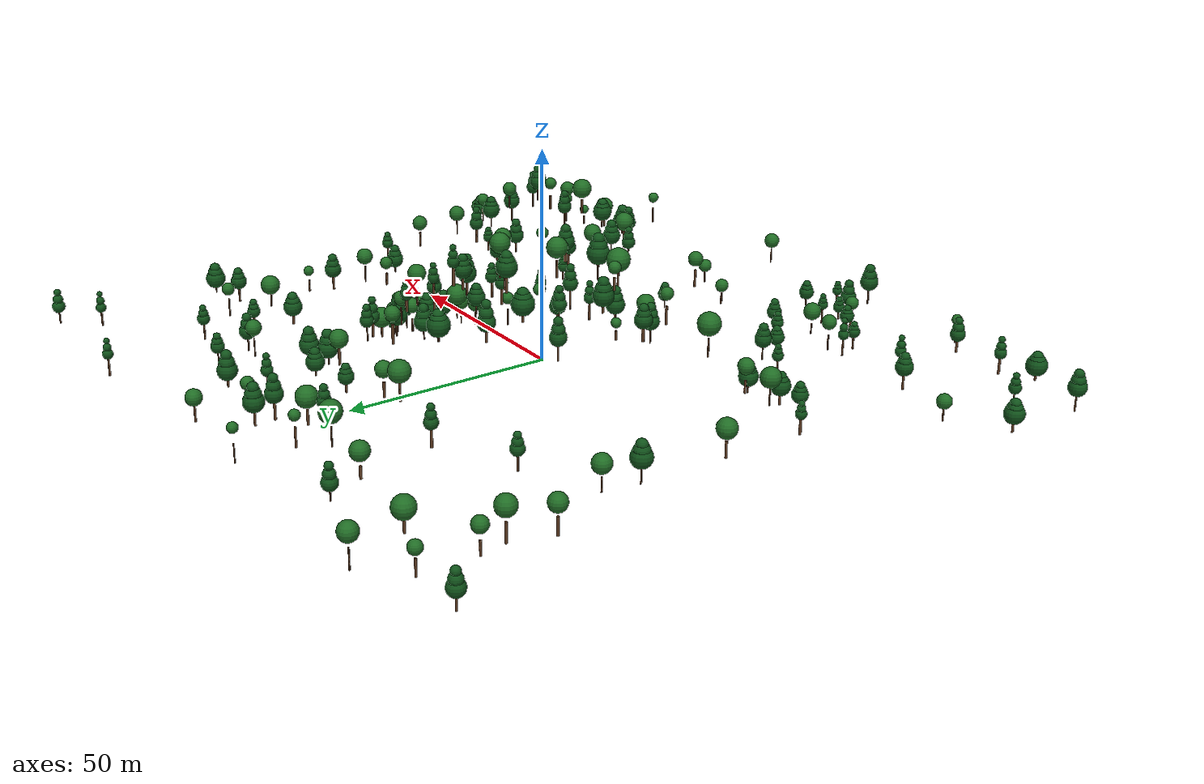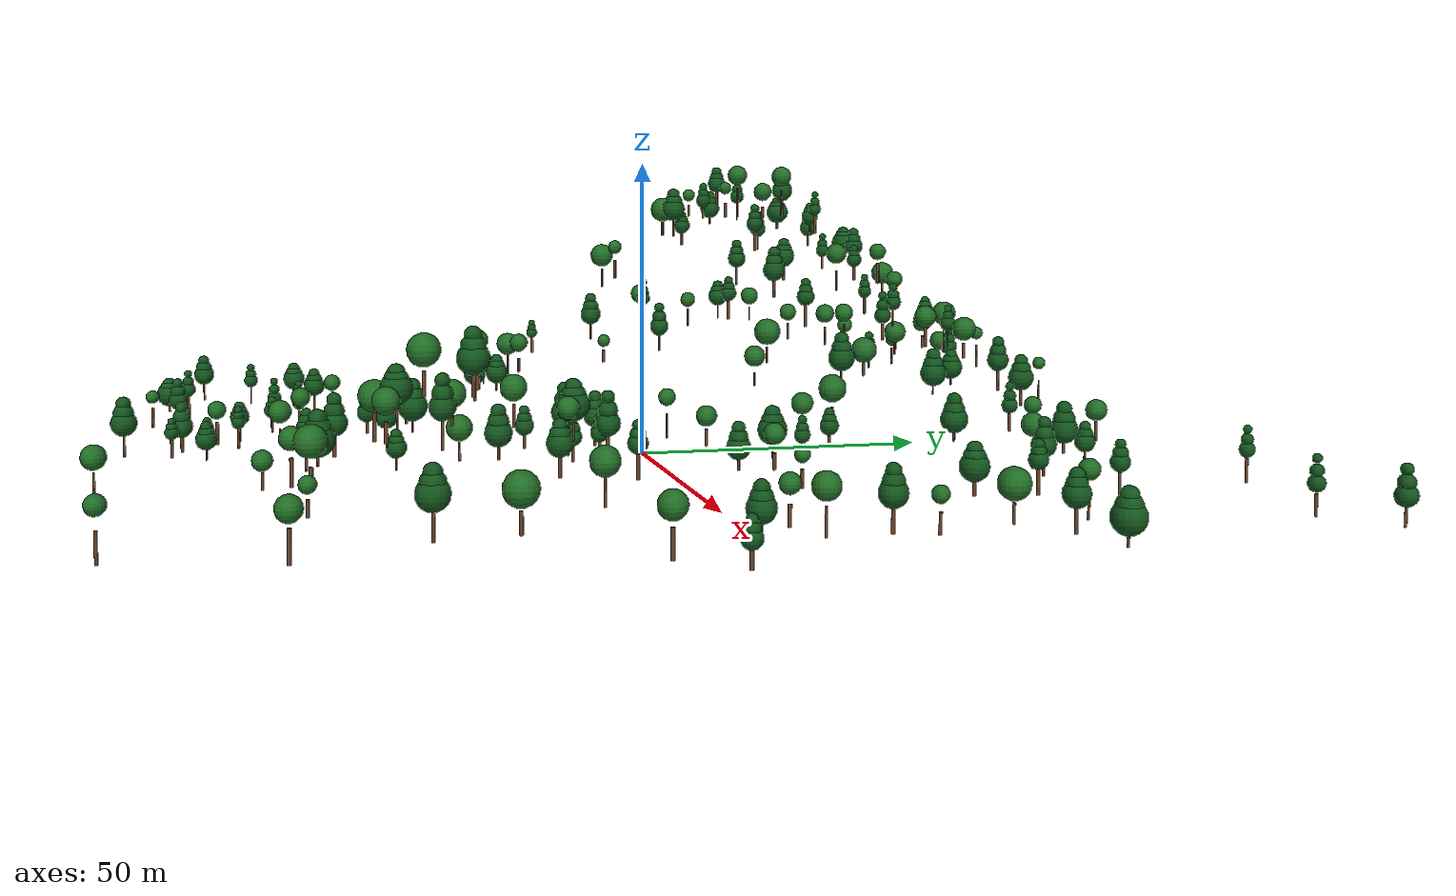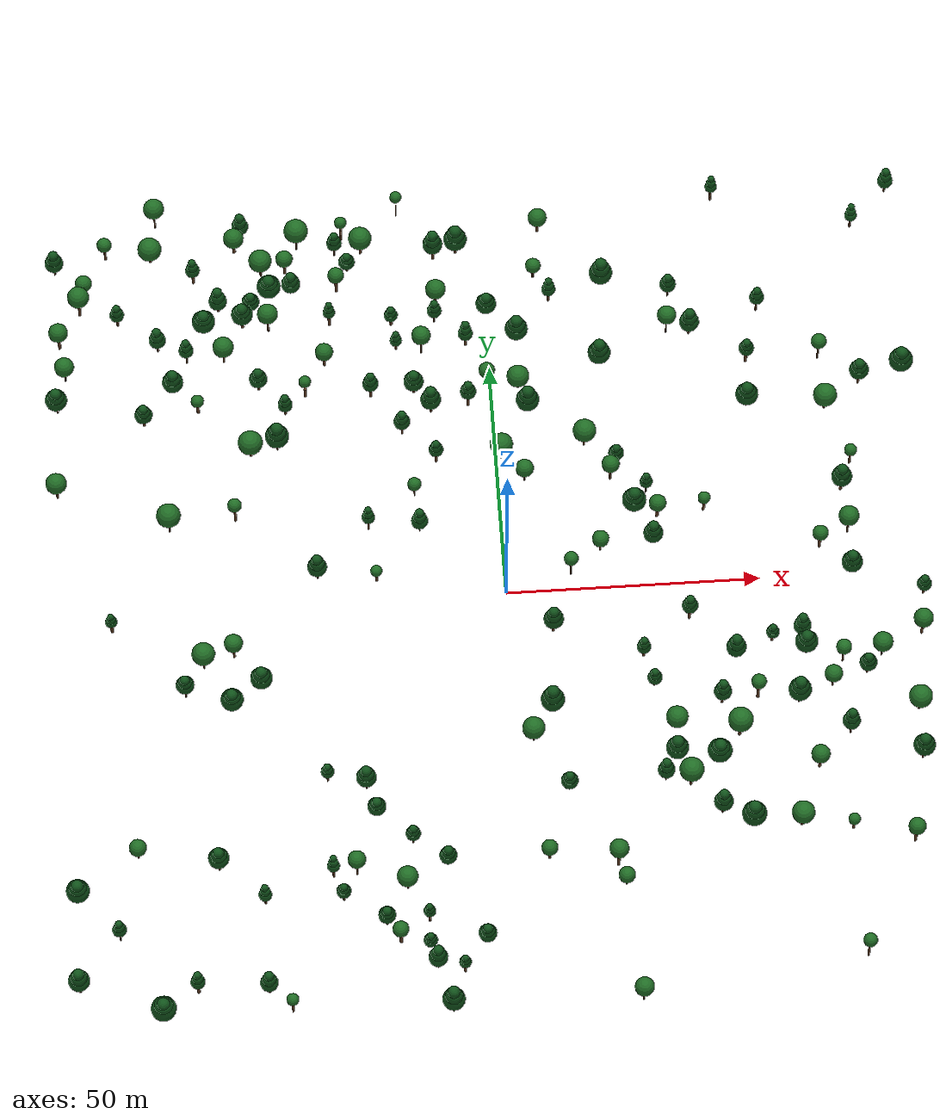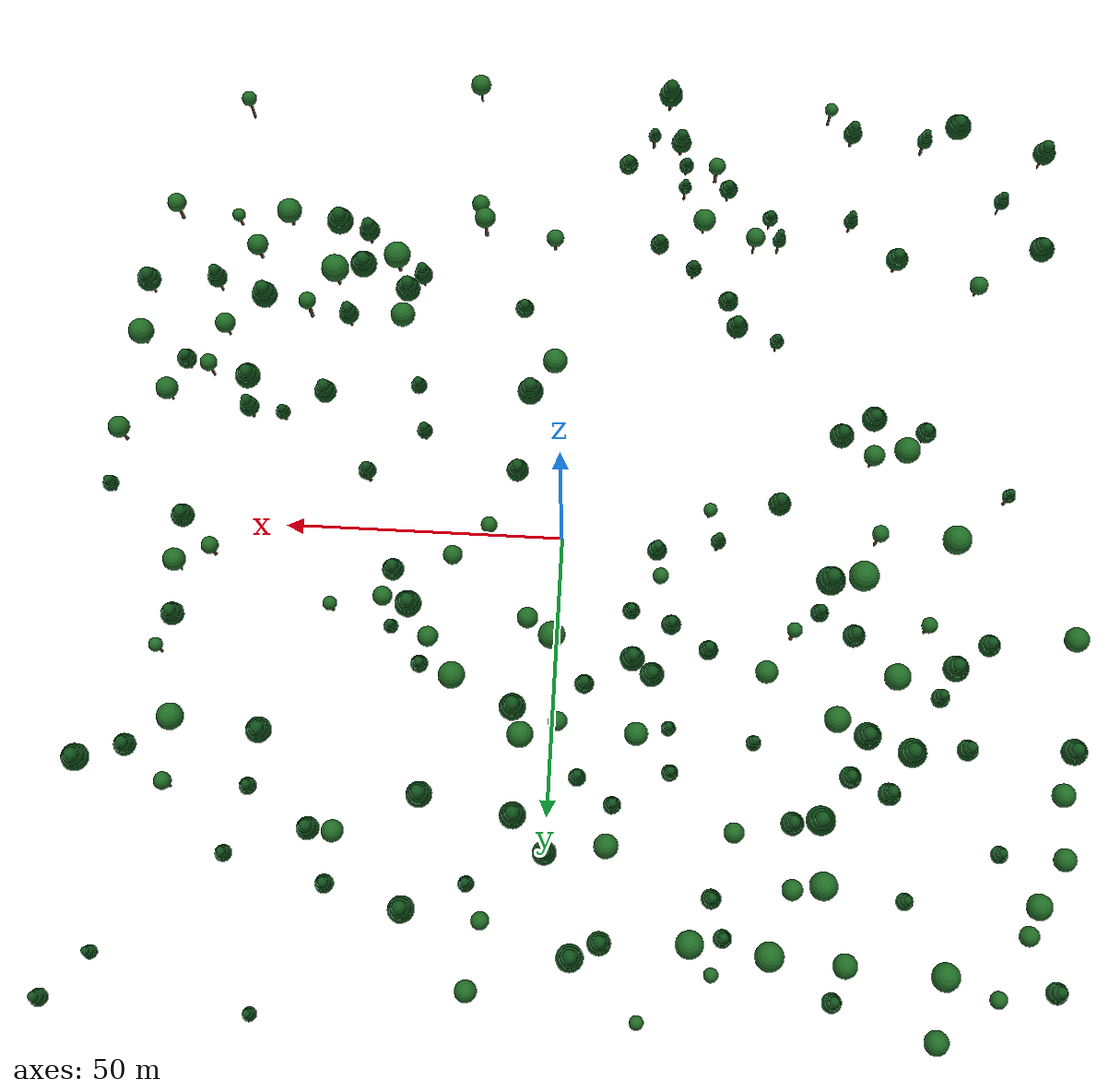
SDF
<?xml version="1.0"?>
<sdf version="1.6">
  <model name="ugv_mou_forest_obstacles">
    <static>true</static>
    <link name="tree_000_link">
      <pose>-48.478 40.969 40.721 0 0 -1.636</pose>
      <collision name="trunk_collision">
        <pose>0 0 2.085 0 0 0</pose>
        <geometry><cylinder><radius>0.293</radius><length>4.169</length></cylinder></geometry>
      </collision>
      <visual name="trunk_visual">
        <pose>0 0 2.085 0 0 0</pose>
        <geometry><cylinder><radius>0.293</radius><length>4.169</length></cylinder></geometry>
        <material><ambient>0.30 0.18 0.10 1</ambient><diffuse>0.36 0.22 0.12 1</diffuse></material>
      </visual>
      <collision name="pine_canopy_0_collision">
        <pose>0 0 5.058 0 0 0</pose>
        <geometry><sphere><radius>2.087</radius></sphere></geometry>
      </collision>
      <visual name="pine_canopy_0_visual">
        <pose>0 0 5.058 0 0 0</pose>
        <geometry><sphere><radius>2.087</radius></sphere></geometry>
        <material><ambient>0.05 0.22 0.08 1</ambient><diffuse>0.06 0.32 0.10 1</diffuse></material>
      </visual>
      <collision name="pine_canopy_1_collision">
        <pose>0 0 6.125 0 0 0</pose>
        <geometry><sphere><radius>1.628</radius></sphere></geometry>
      </collision>
      <visual name="pine_canopy_1_visual">
        <pose>0 0 6.125 0 0 0</pose>
        <geometry><sphere><radius>1.628</radius></sphere></geometry>
        <material><ambient>0.05 0.22 0.08 1</ambient><diffuse>0.06 0.32 0.10 1</diffuse></material>
      </visual>
      <collision name="pine_canopy_2_collision">
        <pose>0 0 7.192 0 0 0</pose>
        <geometry><sphere><radius>1.148</radius></sphere></geometry>
      </collision>
      <visual name="pine_canopy_2_visual">
        <pose>0 0 7.192 0 0 0</pose>
        <geometry><sphere><radius>1.148</radius></sphere></geometry>
        <material><ambient>0.05 0.22 0.08 1</ambient><diffuse>0.06 0.32 0.10 1</diffuse></material>
      </visual>
    </link>
    <link name="tree_001_link">
      <pose>-86.581 18.896 16.176 0 0 2.470</pose>
      <collision name="trunk_collision">
        <pose>0 0 1.675 0 0 0</pose>
        <geometry><cylinder><radius>0.237</radius><length>3.350</length></cylinder></geometry>
      </collision>
      <visual name="trunk_visual">
        <pose>0 0 1.675 0 0 0</pose>
        <geometry><cylinder><radius>0.237</radius><length>3.350</length></cylinder></geometry>
        <material><ambient>0.30 0.18 0.10 1</ambient><diffuse>0.36 0.22 0.12 1</diffuse></material>
      </visual>
      <collision name="leaf_canopy_collision">
        <pose>0 0 5.940 0 0 0</pose>
        <geometry><sphere><radius>2.073</radius></sphere></geometry>
      </collision>
      <visual name="leaf_canopy_visual">
        <pose>0 0 5.940 0 0 0</pose>
        <geometry><sphere><radius>2.073</radius></sphere></geometry>
        <material><ambient>0.08 0.30 0.10 1</ambient><diffuse>0.12 0.42 0.14 1</diffuse></material>
      </visual>
    </link>
    <link name="tree_002_link">
      <pose>-54.003 -14.086 8.367 0 0 2.694</pose>
      <collision name="trunk_collision">
        <pose>0 0 1.402 0 0 0</pose>
        <geometry><cylinder><radius>0.244</radius><length>2.803</length></cylinder></geometry>
      </collision>
      <visual name="trunk_visual">
        <pose>0 0 1.402 0 0 0</pose>
        <geometry><cylinder><radius>0.244</radius><length>2.803</length></cylinder></geometry>
        <material><ambient>0.30 0.18 0.10 1</ambient><diffuse>0.36 0.22 0.12 1</diffuse></material>
      </visual>
      <collision name="leaf_canopy_collision">
        <pose>0 0 6.093 0 0 0</pose>
        <geometry><sphere><radius>1.831</radius></sphere></geometry>
      </collision>
      <visual name="leaf_canopy_visual">
        <pose>0 0 6.093 0 0 0</pose>
        <geometry><sphere><radius>1.831</radius></sphere></geometry>
        <material><ambient>0.08 0.30 0.10 1</ambient><diffuse>0.12 0.42 0.14 1</diffuse></material>
      </visual>
    </link>
    <link name="tree_003_link">
      <pose>65.948 36.747 0.000 0 0 0.606</pose>
      <collision name="trunk_collision">
        <pose>0 0 1.482 0 0 0</pose>
        <geometry><cylinder><radius>0.205</radius><length>2.964</length></cylinder></geometry>
      </collision>
      <visual name="trunk_visual">
        <pose>0 0 1.482 0 0 0</pose>
        <geometry><cylinder><radius>0.205</radius><length>2.964</length></cylinder></geometry>
        <material><ambient>0.30 0.18 0.10 1</ambient><diffuse>0.36 0.22 0.12 1</diffuse></material>
      </visual>
      <collision name="leaf_canopy_collision">
        <pose>0 0 5.574 0 0 0</pose>
        <geometry><sphere><radius>2.364</radius></sphere></geometry>
      </collision>
      <visual name="leaf_canopy_visual">
        <pose>0 0 5.574 0 0 0</pose>
        <geometry><sphere><radius>2.364</radius></sphere></geometry>
        <material><ambient>0.08 0.30 0.10 1</ambient><diffuse>0.12 0.42 0.14 1</diffuse></material>
      </visual>
    </link>
    <link name="tree_004_link">
      <pose>-36.944 -2.176 16.451 0 0 0.818</pose>
      <collision name="trunk_collision">
        <pose>0 0 1.834 0 0 0</pose>
        <geometry><cylinder><radius>0.163</radius><length>3.668</length></cylinder></geometry>
      </collision>
      <visual name="trunk_visual">
        <pose>0 0 1.834 0 0 0</pose>
        <geometry><cylinder><radius>0.163</radius><length>3.668</length></cylinder></geometry>
        <material><ambient>0.30 0.18 0.10 1</ambient><diffuse>0.36 0.22 0.12 1</diffuse></material>
      </visual>
      <collision name="pine_canopy_0_collision">
        <pose>0 0 4.969 0 0 0</pose>
        <geometry><sphere><radius>1.920</radius></sphere></geometry>
      </collision>
      <visual name="pine_canopy_0_visual">
        <pose>0 0 4.969 0 0 0</pose>
        <geometry><sphere><radius>1.920</radius></sphere></geometry>
        <material><ambient>0.05 0.22 0.08 1</ambient><diffuse>0.06 0.32 0.10 1</diffuse></material>
      </visual>
      <collision name="pine_canopy_1_collision">
        <pose>0 0 6.529 0 0 0</pose>
        <geometry><sphere><radius>1.498</radius></sphere></geometry>
      </collision>
      <visual name="pine_canopy_1_visual">
        <pose>0 0 6.529 0 0 0</pose>
        <geometry><sphere><radius>1.498</radius></sphere></geometry>
        <material><ambient>0.05 0.22 0.08 1</ambient><diffuse>0.06 0.32 0.10 1</diffuse></material>
      </visual>
      <collision name="pine_canopy_2_collision">
        <pose>0 0 8.089 0 0 0</pose>
        <geometry><sphere><radius>1.056</radius></sphere></geometry>
      </collision>
      <visual name="pine_canopy_2_visual">
        <pose>0 0 8.089 0 0 0</pose>
        <geometry><sphere><radius>1.056</radius></sphere></geometry>
        <material><ambient>0.05 0.22 0.08 1</ambient><diffuse>0.06 0.32 0.10 1</diffuse></material>
      </visual>
    </link>
    <link name="tree_005_link">
      <pose>-16.517 6.834 16.188 0 0 -0.403</pose>
      <collision name="trunk_collision">
        <pose>0 0 1.483 0 0 0</pose>
        <geometry><cylinder><radius>0.161</radius><length>2.966</length></cylinder></geometry>
      </collision>
      <visual name="trunk_visual">
        <pose>0 0 1.483 0 0 0</pose>
        <geometry><cylinder><radius>0.161</radius><length>2.966</length></cylinder></geometry>
        <material><ambient>0.30 0.18 0.10 1</ambient><diffuse>0.36 0.22 0.12 1</diffuse></material>
      </visual>
      <collision name="pine_canopy_0_collision">
        <pose>0 0 4.404 0 0 0</pose>
        <geometry><sphere><radius>1.648</radius></sphere></geometry>
      </collision>
      <visual name="pine_canopy_0_visual">
        <pose>0 0 4.404 0 0 0</pose>
        <geometry><sphere><radius>1.648</radius></sphere></geometry>
        <material><ambient>0.05 0.22 0.08 1</ambient><diffuse>0.06 0.32 0.10 1</diffuse></material>
      </visual>
      <collision name="pine_canopy_1_collision">
        <pose>0 0 6.130 0 0 0</pose>
        <geometry><sphere><radius>1.286</radius></sphere></geometry>
      </collision>
      <visual name="pine_canopy_1_visual">
        <pose>0 0 6.130 0 0 0</pose>
        <geometry><sphere><radius>1.286</radius></sphere></geometry>
        <material><ambient>0.05 0.22 0.08 1</ambient><diffuse>0.06 0.32 0.10 1</diffuse></material>
      </visual>
      <collision name="pine_canopy_2_collision">
        <pose>0 0 7.855 0 0 0</pose>
        <geometry><sphere><radius>0.906</radius></sphere></geometry>
      </collision>
      <visual name="pine_canopy_2_visual">
        <pose>0 0 7.855 0 0 0</pose>
        <geometry><sphere><radius>0.906</radius></sphere></geometry>
        <material><ambient>0.05 0.22 0.08 1</ambient><diffuse>0.06 0.32 0.10 1</diffuse></material>
      </visual>
    </link>
    <link name="tree_006_link">
      <pose>-21.611 -52.166 0.578 0 0 0.785</pose>
      <collision name="trunk_collision">
        <pose>0 0 1.613 0 0 0</pose>
        <geometry><cylinder><radius>0.204</radius><length>3.226</length></cylinder></geometry>
      </collision>
      <visual name="trunk_visual">
        <pose>0 0 1.613 0 0 0</pose>
        <geometry><cylinder><radius>0.204</radius><length>3.226</length></cylinder></geometry>
        <material><ambient>0.30 0.18 0.10 1</ambient><diffuse>0.36 0.22 0.12 1</diffuse></material>
      </visual>
      <collision name="pine_canopy_0_collision">
        <pose>0 0 4.106 0 0 0</pose>
        <geometry><sphere><radius>1.469</radius></sphere></geometry>
      </collision>
      <visual name="pine_canopy_0_visual">
        <pose>0 0 4.106 0 0 0</pose>
        <geometry><sphere><radius>1.469</radius></sphere></geometry>
        <material><ambient>0.05 0.22 0.08 1</ambient><diffuse>0.06 0.32 0.10 1</diffuse></material>
      </visual>
      <collision name="pine_canopy_1_collision">
        <pose>0 0 5.162 0 0 0</pose>
        <geometry><sphere><radius>1.146</radius></sphere></geometry>
      </collision>
      <visual name="pine_canopy_1_visual">
        <pose>0 0 5.162 0 0 0</pose>
        <geometry><sphere><radius>1.146</radius></sphere></geometry>
        <material><ambient>0.05 0.22 0.08 1</ambient><diffuse>0.06 0.32 0.10 1</diffuse></material>
      </visual>
      <collision name="pine_canopy_2_collision">
        <pose>0 0 6.218 0 0 0</pose>
        <geometry><sphere><radius>0.808</radius></sphere></geometry>
      </collision>
      <visual name="pine_canopy_2_visual">
        <pose>0 0 6.218 0 0 0</pose>
        <geometry><sphere><radius>0.808</radius></sphere></geometry>
        <material><ambient>0.05 0.22 0.08 1</ambient><diffuse>0.06 0.32 0.10 1</diffuse></material>
      </visual>
    </link>
    <link name="tree_007_link">
      <pose>9.278 -42.842 0.501 0 0 2.120</pose>
      <collision name="trunk_collision">
        <pose>0 0 1.377 0 0 0</pose>
        <geometry><cylinder><radius>0.151</radius><length>2.755</length></cylinder></geometry>
      </collision>
      <visual name="trunk_visual">
        <pose>0 0 1.377 0 0 0</pose>
        <geometry><cylinder><radius>0.151</radius><length>2.755</length></cylinder></geometry>
        <material><ambient>0.30 0.18 0.10 1</ambient><diffuse>0.36 0.22 0.12 1</diffuse></material>
      </visual>
      <collision name="pine_canopy_0_collision">
        <pose>0 0 3.628 0 0 0</pose>
        <geometry><sphere><radius>1.698</radius></sphere></geometry>
      </collision>
      <visual name="pine_canopy_0_visual">
        <pose>0 0 3.628 0 0 0</pose>
        <geometry><sphere><radius>1.698</radius></sphere></geometry>
        <material><ambient>0.05 0.22 0.08 1</ambient><diffuse>0.06 0.32 0.10 1</diffuse></material>
      </visual>
      <collision name="pine_canopy_1_collision">
        <pose>0 0 4.677 0 0 0</pose>
        <geometry><sphere><radius>1.325</radius></sphere></geometry>
      </collision>
      <visual name="pine_canopy_1_visual">
        <pose>0 0 4.677 0 0 0</pose>
        <geometry><sphere><radius>1.325</radius></sphere></geometry>
        <material><ambient>0.05 0.22 0.08 1</ambient><diffuse>0.06 0.32 0.10 1</diffuse></material>
      </visual>
      <collision name="pine_canopy_2_collision">
        <pose>0 0 5.725 0 0 0</pose>
        <geometry><sphere><radius>0.934</radius></sphere></geometry>
      </collision>
      <visual name="pine_canopy_2_visual">
        <pose>0 0 5.725 0 0 0</pose>
        <geometry><sphere><radius>0.934</radius></sphere></geometry>
        <material><ambient>0.05 0.22 0.08 1</ambient><diffuse>0.06 0.32 0.10 1</diffuse></material>
      </visual>
    </link>
    <link name="tree_008_link">
      <pose>-16.063 -87.380 0.000 0 0 -1.664</pose>
      <collision name="trunk_collision">
        <pose>0 0 2.205 0 0 0</pose>
        <geometry><cylinder><radius>0.207</radius><length>4.410</length></cylinder></geometry>
      </collision>
      <visual name="trunk_visual">
        <pose>0 0 2.205 0 0 0</pose>
        <geometry><cylinder><radius>0.207</radius><length>4.410</length></cylinder></geometry>
        <material><ambient>0.30 0.18 0.10 1</ambient><diffuse>0.36 0.22 0.12 1</diffuse></material>
      </visual>
      <collision name="pine_canopy_0_collision">
        <pose>0 0 5.814 0 0 0</pose>
        <geometry><sphere><radius>2.218</radius></sphere></geometry>
      </collision>
      <visual name="pine_canopy_0_visual">
        <pose>0 0 5.814 0 0 0</pose>
        <geometry><sphere><radius>2.218</radius></sphere></geometry>
        <material><ambient>0.05 0.22 0.08 1</ambient><diffuse>0.06 0.32 0.10 1</diffuse></material>
      </visual>
      <collision name="pine_canopy_1_collision">
        <pose>0 0 7.499 0 0 0</pose>
        <geometry><sphere><radius>1.730</radius></sphere></geometry>
      </collision>
      <visual name="pine_canopy_1_visual">
        <pose>0 0 7.499 0 0 0</pose>
        <geometry><sphere><radius>1.730</radius></sphere></geometry>
        <material><ambient>0.05 0.22 0.08 1</ambient><diffuse>0.06 0.32 0.10 1</diffuse></material>
      </visual>
      <collision name="pine_canopy_2_collision">
        <pose>0 0 9.183 0 0 0</pose>
        <geometry><sphere><radius>1.220</radius></sphere></geometry>
      </collision>
      <visual name="pine_canopy_2_visual">
        <pose>0 0 9.183 0 0 0</pose>
        <geometry><sphere><radius>1.220</radius></sphere></geometry>
        <material><ambient>0.05 0.22 0.08 1</ambient><diffuse>0.06 0.32 0.10 1</diffuse></material>
      </visual>
    </link>
    <link name="tree_009_link">
      <pose>-25.502 -1.821 13.287 0 0 0.228</pose>
      <collision name="trunk_collision">
        <pose>0 0 1.102 0 0 0</pose>
        <geometry><cylinder><radius>0.270</radius><length>2.205</length></cylinder></geometry>
      </collision>
      <visual name="trunk_visual">
        <pose>0 0 1.102 0 0 0</pose>
        <geometry><cylinder><radius>0.270</radius><length>2.205</length></cylinder></geometry>
        <material><ambient>0.30 0.18 0.10 1</ambient><diffuse>0.36 0.22 0.12 1</diffuse></material>
      </visual>
      <collision name="leaf_canopy_collision">
        <pose>0 0 4.043 0 0 0</pose>
        <geometry><sphere><radius>1.162</radius></sphere></geometry>
      </collision>
      <visual name="leaf_canopy_visual">
        <pose>0 0 4.043 0 0 0</pose>
        <geometry><sphere><radius>1.162</radius></sphere></geometry>
        <material><ambient>0.08 0.30 0.10 1</ambient><diffuse>0.12 0.42 0.14 1</diffuse></material>
      </visual>
    </link>
    <link name="tree_010_link">
      <pose>-75.394 77.097 5.361 0 0 -1.447</pose>
      <collision name="trunk_collision">
        <pose>0 0 1.875 0 0 0</pose>
        <geometry><cylinder><radius>0.237</radius><length>3.750</length></cylinder></geometry>
      </collision>
      <visual name="trunk_visual">
        <pose>0 0 1.875 0 0 0</pose>
        <geometry><cylinder><radius>0.237</radius><length>3.750</length></cylinder></geometry>
        <material><ambient>0.30 0.18 0.10 1</ambient><diffuse>0.36 0.22 0.12 1</diffuse></material>
      </visual>
      <collision name="leaf_canopy_collision">
        <pose>0 0 5.848 0 0 0</pose>
        <geometry><sphere><radius>1.469</radius></sphere></geometry>
      </collision>
      <visual name="leaf_canopy_visual">
        <pose>0 0 5.848 0 0 0</pose>
        <geometry><sphere><radius>1.469</radius></sphere></geometry>
        <material><ambient>0.08 0.30 0.10 1</ambient><diffuse>0.12 0.42 0.14 1</diffuse></material>
      </visual>
    </link>
    <link name="tree_011_link">
      <pose>26.200 15.094 3.036 0 0 1.485</pose>
      <collision name="trunk_collision">
        <pose>0 0 1.739 0 0 0</pose>
        <geometry><cylinder><radius>0.159</radius><length>3.477</length></cylinder></geometry>
      </collision>
      <visual name="trunk_visual">
        <pose>0 0 1.739 0 0 0</pose>
        <geometry><cylinder><radius>0.159</radius><length>3.477</length></cylinder></geometry>
        <material><ambient>0.30 0.18 0.10 1</ambient><diffuse>0.36 0.22 0.12 1</diffuse></material>
      </visual>
      <collision name="pine_canopy_0_collision">
        <pose>0 0 4.563 0 0 0</pose>
        <geometry><sphere><radius>2.371</radius></sphere></geometry>
      </collision>
      <visual name="pine_canopy_0_visual">
        <pose>0 0 4.563 0 0 0</pose>
        <geometry><sphere><radius>2.371</radius></sphere></geometry>
        <material><ambient>0.05 0.22 0.08 1</ambient><diffuse>0.06 0.32 0.10 1</diffuse></material>
      </visual>
      <collision name="pine_canopy_1_collision">
        <pose>0 0 5.866 0 0 0</pose>
        <geometry><sphere><radius>1.850</radius></sphere></geometry>
      </collision>
      <visual name="pine_canopy_1_visual">
        <pose>0 0 5.866 0 0 0</pose>
        <geometry><sphere><radius>1.850</radius></sphere></geometry>
        <material><ambient>0.05 0.22 0.08 1</ambient><diffuse>0.06 0.32 0.10 1</diffuse></material>
      </visual>
      <collision name="pine_canopy_2_collision">
        <pose>0 0 7.169 0 0 0</pose>
        <geometry><sphere><radius>1.304</radius></sphere></geometry>
      </collision>
      <visual name="pine_canopy_2_visual">
        <pose>0 0 7.169 0 0 0</pose>
        <geometry><sphere><radius>1.304</radius></sphere></geometry>
        <material><ambient>0.05 0.22 0.08 1</ambient><diffuse>0.06 0.32 0.10 1</diffuse></material>
      </visual>
    </link>
    <link name="tree_012_link">
      <pose>-49.018 -19.318 5.262 0 0 2.279</pose>
      <collision name="trunk_collision">
        <pose>0 0 1.365 0 0 0</pose>
        <geometry><cylinder><radius>0.203</radius><length>2.729</length></cylinder></geometry>
      </collision>
      <visual name="trunk_visual">
        <pose>0 0 1.365 0 0 0</pose>
        <geometry><cylinder><radius>0.203</radius><length>2.729</length></cylinder></geometry>
        <material><ambient>0.30 0.18 0.10 1</ambient><diffuse>0.36 0.22 0.12 1</diffuse></material>
      </visual>
      <collision name="pine_canopy_0_collision">
        <pose>0 0 3.756 0 0 0</pose>
        <geometry><sphere><radius>2.180</radius></sphere></geometry>
      </collision>
      <visual name="pine_canopy_0_visual">
        <pose>0 0 3.756 0 0 0</pose>
        <geometry><sphere><radius>2.180</radius></sphere></geometry>
        <material><ambient>0.05 0.22 0.08 1</ambient><diffuse>0.06 0.32 0.10 1</diffuse></material>
      </visual>
      <collision name="pine_canopy_1_collision">
        <pose>0 0 4.988 0 0 0</pose>
        <geometry><sphere><radius>1.700</radius></sphere></geometry>
      </collision>
      <visual name="pine_canopy_1_visual">
        <pose>0 0 4.988 0 0 0</pose>
        <geometry><sphere><radius>1.700</radius></sphere></geometry>
        <material><ambient>0.05 0.22 0.08 1</ambient><diffuse>0.06 0.32 0.10 1</diffuse></material>
      </visual>
      <collision name="pine_canopy_2_collision">
        <pose>0 0 6.220 0 0 0</pose>
        <geometry><sphere><radius>1.199</radius></sphere></geometry>
      </collision>
      <visual name="pine_canopy_2_visual">
        <pose>0 0 6.220 0 0 0</pose>
        <geometry><sphere><radius>1.199</radius></sphere></geometry>
        <material><ambient>0.05 0.22 0.08 1</ambient><diffuse>0.06 0.32 0.10 1</diffuse></material>
      </visual>
    </link>
    <link name="tree_013_link">
      <pose>-46.071 26.004 43.059 0 0 2.508</pose>
      <collision name="trunk_collision">
        <pose>0 0 1.565 0 0 0</pose>
        <geometry><cylinder><radius>0.292</radius><length>3.130</length></cylinder></geometry>
      </collision>
      <visual name="trunk_visual">
        <pose>0 0 1.565 0 0 0</pose>
        <geometry><cylinder><radius>0.292</radius><length>3.130</length></cylinder></geometry>
        <material><ambient>0.30 0.18 0.10 1</ambient><diffuse>0.36 0.22 0.12 1</diffuse></material>
      </visual>
      <collision name="pine_canopy_0_collision">
        <pose>0 0 4.144 0 0 0</pose>
        <geometry><sphere><radius>1.735</radius></sphere></geometry>
      </collision>
      <visual name="pine_canopy_0_visual">
        <pose>0 0 4.144 0 0 0</pose>
        <geometry><sphere><radius>1.735</radius></sphere></geometry>
        <material><ambient>0.05 0.22 0.08 1</ambient><diffuse>0.06 0.32 0.10 1</diffuse></material>
      </visual>
      <collision name="pine_canopy_1_collision">
        <pose>0 0 5.359 0 0 0</pose>
        <geometry><sphere><radius>1.353</radius></sphere></geometry>
      </collision>
      <visual name="pine_canopy_1_visual">
        <pose>0 0 5.359 0 0 0</pose>
        <geometry><sphere><radius>1.353</radius></sphere></geometry>
        <material><ambient>0.05 0.22 0.08 1</ambient><diffuse>0.06 0.32 0.10 1</diffuse></material>
      </visual>
      <collision name="pine_canopy_2_collision">
        <pose>0 0 6.575 0 0 0</pose>
        <geometry><sphere><radius>0.954</radius></sphere></geometry>
      </collision>
      <visual name="pine_canopy_2_visual">
        <pose>0 0 6.575 0 0 0</pose>
        <geometry><sphere><radius>0.954</radius></sphere></geometry>
        <material><ambient>0.05 0.22 0.08 1</ambient><diffuse>0.06 0.32 0.10 1</diffuse></material>
      </visual>
    </link>
    <link name="tree_014_link">
      <pose>-85.118 54.621 10.833 0 0 -0.708</pose>
      <collision name="trunk_collision">
        <pose>0 0 1.872 0 0 0</pose>
        <geometry><cylinder><radius>0.284</radius><length>3.744</length></cylinder></geometry>
      </collision>
      <visual name="trunk_visual">
        <pose>0 0 1.872 0 0 0</pose>
        <geometry><cylinder><radius>0.284</radius><length>3.744</length></cylinder></geometry>
        <material><ambient>0.30 0.18 0.10 1</ambient><diffuse>0.36 0.22 0.12 1</diffuse></material>
      </visual>
      <collision name="leaf_canopy_collision">
        <pose>0 0 6.470 0 0 0</pose>
        <geometry><sphere><radius>1.913</radius></sphere></geometry>
      </collision>
      <visual name="leaf_canopy_visual">
        <pose>0 0 6.470 0 0 0</pose>
        <geometry><sphere><radius>1.913</radius></sphere></geometry>
        <material><ambient>0.08 0.30 0.10 1</ambient><diffuse>0.12 0.42 0.14 1</diffuse></material>
      </visual>
    </link>
    <link name="tree_015_link">
      <pose>78.084 -32.311 4.737 0 0 -2.588</pose>
      <collision name="trunk_collision">
        <pose>0 0 1.477 0 0 0</pose>
        <geometry><cylinder><radius>0.236</radius><length>2.955</length></cylinder></geometry>
      </collision>
      <visual name="trunk_visual">
        <pose>0 0 1.477 0 0 0</pose>
        <geometry><cylinder><radius>0.236</radius><length>2.955</length></cylinder></geometry>
        <material><ambient>0.30 0.18 0.10 1</ambient><diffuse>0.36 0.22 0.12 1</diffuse></material>
      </visual>
      <collision name="leaf_canopy_collision">
        <pose>0 0 5.525 0 0 0</pose>
        <geometry><sphere><radius>2.300</radius></sphere></geometry>
      </collision>
      <visual name="leaf_canopy_visual">
        <pose>0 0 5.525 0 0 0</pose>
        <geometry><sphere><radius>2.300</radius></sphere></geometry>
        <material><ambient>0.08 0.30 0.10 1</ambient><diffuse>0.12 0.42 0.14 1</diffuse></material>
      </visual>
    </link>
    <link name="tree_016_link">
      <pose>40.077 15.357 0.930 0 0 2.563</pose>
      <collision name="trunk_collision">
        <pose>0 0 1.433 0 0 0</pose>
        <geometry><cylinder><radius>0.263</radius><length>2.865</length></cylinder></geometry>
      </collision>
      <visual name="trunk_visual">
        <pose>0 0 1.433 0 0 0</pose>
        <geometry><cylinder><radius>0.263</radius><length>2.865</length></cylinder></geometry>
        <material><ambient>0.30 0.18 0.10 1</ambient><diffuse>0.36 0.22 0.12 1</diffuse></material>
      </visual>
      <collision name="leaf_canopy_collision">
        <pose>0 0 5.068 0 0 0</pose>
        <geometry><sphere><radius>1.243</radius></sphere></geometry>
      </collision>
      <visual name="leaf_canopy_visual">
        <pose>0 0 5.068 0 0 0</pose>
        <geometry><sphere><radius>1.243</radius></sphere></geometry>
        <material><ambient>0.08 0.30 0.10 1</ambient><diffuse>0.12 0.42 0.14 1</diffuse></material>
      </visual>
    </link>
    <link name="tree_017_link">
      <pose>-15.156 -56.981 0.426 0 0 2.613</pose>
      <collision name="trunk_collision">
        <pose>0 0 1.389 0 0 0</pose>
        <geometry><cylinder><radius>0.276</radius><length>2.778</length></cylinder></geometry>
      </collision>
      <visual name="trunk_visual">
        <pose>0 0 1.389 0 0 0</pose>
        <geometry><cylinder><radius>0.276</radius><length>2.778</length></cylinder></geometry>
        <material><ambient>0.30 0.18 0.10 1</ambient><diffuse>0.36 0.22 0.12 1</diffuse></material>
      </visual>
      <collision name="pine_canopy_0_collision">
        <pose>0 0 3.794 0 0 0</pose>
        <geometry><sphere><radius>1.735</radius></sphere></geometry>
      </collision>
      <visual name="pine_canopy_0_visual">
        <pose>0 0 3.794 0 0 0</pose>
        <geometry><sphere><radius>1.735</radius></sphere></geometry>
        <material><ambient>0.05 0.22 0.08 1</ambient><diffuse>0.06 0.32 0.10 1</diffuse></material>
      </visual>
      <collision name="pine_canopy_1_collision">
        <pose>0 0 5.014 0 0 0</pose>
        <geometry><sphere><radius>1.353</radius></sphere></geometry>
      </collision>
      <visual name="pine_canopy_1_visual">
        <pose>0 0 5.014 0 0 0</pose>
        <geometry><sphere><radius>1.353</radius></sphere></geometry>
        <material><ambient>0.05 0.22 0.08 1</ambient><diffuse>0.06 0.32 0.10 1</diffuse></material>
      </visual>
      <collision name="pine_canopy_2_collision">
        <pose>0 0 6.234 0 0 0</pose>
        <geometry><sphere><radius>0.954</radius></sphere></geometry>
      </collision>
      <visual name="pine_canopy_2_visual">
        <pose>0 0 6.234 0 0 0</pose>
        <geometry><sphere><radius>0.954</radius></sphere></geometry>
        <material><ambient>0.05 0.22 0.08 1</ambient><diffuse>0.06 0.32 0.10 1</diffuse></material>
      </visual>
    </link>
    <link name="tree_018_link">
      <pose>-64.429 -80.416 0.091 0 0 0.534</pose>
      <collision name="trunk_collision">
        <pose>0 0 1.921 0 0 0</pose>
        <geometry><cylinder><radius>0.283</radius><length>3.843</length></cylinder></geometry>
      </collision>
      <visual name="trunk_visual">
        <pose>0 0 1.921 0 0 0</pose>
        <geometry><cylinder><radius>0.283</radius><length>3.843</length></cylinder></geometry>
        <material><ambient>0.30 0.18 0.10 1</ambient><diffuse>0.36 0.22 0.12 1</diffuse></material>
      </visual>
      <collision name="pine_canopy_0_collision">
        <pose>0 0 5.189 0 0 0</pose>
        <geometry><sphere><radius>1.409</radius></sphere></geometry>
      </collision>
      <visual name="pine_canopy_0_visual">
        <pose>0 0 5.189 0 0 0</pose>
        <geometry><sphere><radius>1.409</radius></sphere></geometry>
        <material><ambient>0.05 0.22 0.08 1</ambient><diffuse>0.06 0.32 0.10 1</diffuse></material>
      </visual>
      <collision name="pine_canopy_1_collision">
        <pose>0 0 6.805 0 0 0</pose>
        <geometry><sphere><radius>1.099</radius></sphere></geometry>
      </collision>
      <visual name="pine_canopy_1_visual">
        <pose>0 0 6.805 0 0 0</pose>
        <geometry><sphere><radius>1.099</radius></sphere></geometry>
        <material><ambient>0.05 0.22 0.08 1</ambient><diffuse>0.06 0.32 0.10 1</diffuse></material>
      </visual>
      <collision name="pine_canopy_2_collision">
        <pose>0 0 8.421 0 0 0</pose>
        <geometry><sphere><radius>0.775</radius></sphere></geometry>
      </collision>
      <visual name="pine_canopy_2_visual">
        <pose>0 0 8.421 0 0 0</pose>
        <geometry><sphere><radius>0.775</radius></sphere></geometry>
        <material><ambient>0.05 0.22 0.08 1</ambient><diffuse>0.06 0.32 0.10 1</diffuse></material>
      </visual>
    </link>
    <link name="tree_019_link">
      <pose>56.988 -46.767 12.675 0 0 -2.031</pose>
      <collision name="trunk_collision">
        <pose>0 0 1.449 0 0 0</pose>
        <geometry><cylinder><radius>0.258</radius><length>2.899</length></cylinder></geometry>
      </collision>
      <visual name="trunk_visual">
        <pose>0 0 1.449 0 0 0</pose>
        <geometry><cylinder><radius>0.258</radius><length>2.899</length></cylinder></geometry>
        <material><ambient>0.30 0.18 0.10 1</ambient><diffuse>0.36 0.22 0.12 1</diffuse></material>
      </visual>
      <collision name="leaf_canopy_collision">
        <pose>0 0 5.588 0 0 0</pose>
        <geometry><sphere><radius>1.840</radius></sphere></geometry>
      </collision>
      <visual name="leaf_canopy_visual">
        <pose>0 0 5.588 0 0 0</pose>
        <geometry><sphere><radius>1.840</radius></sphere></geometry>
        <material><ambient>0.08 0.30 0.10 1</ambient><diffuse>0.12 0.42 0.14 1</diffuse></material>
      </visual>
    </link>
    <link name="tree_020_link">
      <pose>40.308 54.693 1.097 0 0 -1.621</pose>
      <collision name="trunk_collision">
        <pose>0 0 1.770 0 0 0</pose>
        <geometry><cylinder><radius>0.188</radius><length>3.541</length></cylinder></geometry>
      </collision>
      <visual name="trunk_visual">
        <pose>0 0 1.770 0 0 0</pose>
        <geometry><cylinder><radius>0.188</radius><length>3.541</length></cylinder></geometry>
        <material><ambient>0.30 0.18 0.10 1</ambient><diffuse>0.36 0.22 0.12 1</diffuse></material>
      </visual>
      <collision name="pine_canopy_0_collision">
        <pose>0 0 4.945 0 0 0</pose>
        <geometry><sphere><radius>1.991</radius></sphere></geometry>
      </collision>
      <visual name="pine_canopy_0_visual">
        <pose>0 0 4.945 0 0 0</pose>
        <geometry><sphere><radius>1.991</radius></sphere></geometry>
        <material><ambient>0.05 0.22 0.08 1</ambient><diffuse>0.06 0.32 0.10 1</diffuse></material>
      </visual>
      <collision name="pine_canopy_1_collision">
        <pose>0 0 6.630 0 0 0</pose>
        <geometry><sphere><radius>1.553</radius></sphere></geometry>
      </collision>
      <visual name="pine_canopy_1_visual">
        <pose>0 0 6.630 0 0 0</pose>
        <geometry><sphere><radius>1.553</radius></sphere></geometry>
        <material><ambient>0.05 0.22 0.08 1</ambient><diffuse>0.06 0.32 0.10 1</diffuse></material>
      </visual>
      <collision name="pine_canopy_2_collision">
        <pose>0 0 8.315 0 0 0</pose>
        <geometry><sphere><radius>1.095</radius></sphere></geometry>
      </collision>
      <visual name="pine_canopy_2_visual">
        <pose>0 0 8.315 0 0 0</pose>
        <geometry><sphere><radius>1.095</radius></sphere></geometry>
        <material><ambient>0.05 0.22 0.08 1</ambient><diffuse>0.06 0.32 0.10 1</diffuse></material>
      </visual>
    </link>
    <link name="tree_021_link">
      <pose>63.524 -40.121 12.625 0 0 -1.650</pose>
      <collision name="trunk_collision">
        <pose>0 0 2.051 0 0 0</pose>
        <geometry><cylinder><radius>0.183</radius><length>4.102</length></cylinder></geometry>
      </collision>
      <visual name="trunk_visual">
        <pose>0 0 2.051 0 0 0</pose>
        <geometry><cylinder><radius>0.183</radius><length>4.102</length></cylinder></geometry>
        <material><ambient>0.30 0.18 0.10 1</ambient><diffuse>0.36 0.22 0.12 1</diffuse></material>
      </visual>
      <collision name="pine_canopy_0_collision">
        <pose>0 0 5.508 0 0 0</pose>
        <geometry><sphere><radius>1.738</radius></sphere></geometry>
      </collision>
      <visual name="pine_canopy_0_visual">
        <pose>0 0 5.508 0 0 0</pose>
        <geometry><sphere><radius>1.738</radius></sphere></geometry>
        <material><ambient>0.05 0.22 0.08 1</ambient><diffuse>0.06 0.32 0.10 1</diffuse></material>
      </visual>
      <collision name="pine_canopy_1_collision">
        <pose>0 0 7.194 0 0 0</pose>
        <geometry><sphere><radius>1.355</radius></sphere></geometry>
      </collision>
      <visual name="pine_canopy_1_visual">
        <pose>0 0 7.194 0 0 0</pose>
        <geometry><sphere><radius>1.355</radius></sphere></geometry>
        <material><ambient>0.05 0.22 0.08 1</ambient><diffuse>0.06 0.32 0.10 1</diffuse></material>
      </visual>
      <collision name="pine_canopy_2_collision">
        <pose>0 0 8.881 0 0 0</pose>
        <geometry><sphere><radius>0.956</radius></sphere></geometry>
      </collision>
      <visual name="pine_canopy_2_visual">
        <pose>0 0 8.881 0 0 0</pose>
        <geometry><sphere><radius>0.956</radius></sphere></geometry>
        <material><ambient>0.05 0.22 0.08 1</ambient><diffuse>0.06 0.32 0.10 1</diffuse></material>
      </visual>
    </link>
    <link name="tree_022_link">
      <pose>-49.480 73.367 11.887 0 0 -0.270</pose>
      <collision name="trunk_collision">
        <pose>0 0 1.282 0 0 0</pose>
        <geometry><cylinder><radius>0.288</radius><length>2.565</length></cylinder></geometry>
      </collision>
      <visual name="trunk_visual">
        <pose>0 0 1.282 0 0 0</pose>
        <geometry><cylinder><radius>0.288</radius><length>2.565</length></cylinder></geometry>
        <material><ambient>0.30 0.18 0.10 1</ambient><diffuse>0.36 0.22 0.12 1</diffuse></material>
      </visual>
      <collision name="leaf_canopy_collision">
        <pose>0 0 5.652 0 0 0</pose>
        <geometry><sphere><radius>2.028</radius></sphere></geometry>
      </collision>
      <visual name="leaf_canopy_visual">
        <pose>0 0 5.652 0 0 0</pose>
        <geometry><sphere><radius>2.028</radius></sphere></geometry>
        <material><ambient>0.08 0.30 0.10 1</ambient><diffuse>0.12 0.42 0.14 1</diffuse></material>
      </visual>
    </link>
    <link name="tree_023_link">
      <pose>-66.331 74.045 8.683 0 0 -1.637</pose>
      <collision name="trunk_collision">
        <pose>0 0 1.242 0 0 0</pose>
        <geometry><cylinder><radius>0.250</radius><length>2.483</length></cylinder></geometry>
      </collision>
      <visual name="trunk_visual">
        <pose>0 0 1.242 0 0 0</pose>
        <geometry><cylinder><radius>0.250</radius><length>2.483</length></cylinder></geometry>
        <material><ambient>0.30 0.18 0.10 1</ambient><diffuse>0.36 0.22 0.12 1</diffuse></material>
      </visual>
      <collision name="leaf_canopy_collision">
        <pose>0 0 5.161 0 0 0</pose>
        <geometry><sphere><radius>2.387</radius></sphere></geometry>
      </collision>
      <visual name="leaf_canopy_visual">
        <pose>0 0 5.161 0 0 0</pose>
        <geometry><sphere><radius>2.387</radius></sphere></geometry>
        <material><ambient>0.08 0.30 0.10 1</ambient><diffuse>0.12 0.42 0.14 1</diffuse></material>
      </visual>
    </link>
    <link name="tree_024_link">
      <pose>62.249 6.004 0.342 0 0 -0.125</pose>
      <collision name="trunk_collision">
        <pose>0 0 1.564 0 0 0</pose>
        <geometry><cylinder><radius>0.282</radius><length>3.128</length></cylinder></geometry>
      </collision>
      <visual name="trunk_visual">
        <pose>0 0 1.564 0 0 0</pose>
        <geometry><cylinder><radius>0.282</radius><length>3.128</length></cylinder></geometry>
        <material><ambient>0.30 0.18 0.10 1</ambient><diffuse>0.36 0.22 0.12 1</diffuse></material>
      </visual>
      <collision name="leaf_canopy_collision">
        <pose>0 0 5.922 0 0 0</pose>
        <geometry><sphere><radius>1.555</radius></sphere></geometry>
      </collision>
      <visual name="leaf_canopy_visual">
        <pose>0 0 5.922 0 0 0</pose>
        <geometry><sphere><radius>1.555</radius></sphere></geometry>
        <material><ambient>0.08 0.30 0.10 1</ambient><diffuse>0.12 0.42 0.14 1</diffuse></material>
      </visual>
    </link>
    <link name="tree_025_link">
      <pose>-84.058 44.725 15.730 0 0 -1.591</pose>
      <collision name="trunk_collision">
        <pose>0 0 1.498 0 0 0</pose>
        <geometry><cylinder><radius>0.157</radius><length>2.996</length></cylinder></geometry>
      </collision>
      <visual name="trunk_visual">
        <pose>0 0 1.498 0 0 0</pose>
        <geometry><cylinder><radius>0.157</radius><length>2.996</length></cylinder></geometry>
        <material><ambient>0.30 0.18 0.10 1</ambient><diffuse>0.36 0.22 0.12 1</diffuse></material>
      </visual>
      <collision name="leaf_canopy_collision">
        <pose>0 0 5.643 0 0 0</pose>
        <geometry><sphere><radius>1.947</radius></sphere></geometry>
      </collision>
      <visual name="leaf_canopy_visual">
        <pose>0 0 5.643 0 0 0</pose>
        <geometry><sphere><radius>1.947</radius></sphere></geometry>
        <material><ambient>0.08 0.30 0.10 1</ambient><diffuse>0.12 0.42 0.14 1</diffuse></material>
      </visual>
    </link>
    <link name="tree_026_link">
      <pose>36.733 63.738 0.877 0 0 -1.318</pose>
      <collision name="trunk_collision">
        <pose>0 0 1.841 0 0 0</pose>
        <geometry><cylinder><radius>0.171</radius><length>3.683</length></cylinder></geometry>
      </collision>
      <visual name="trunk_visual">
        <pose>0 0 1.841 0 0 0</pose>
        <geometry><cylinder><radius>0.171</radius><length>3.683</length></cylinder></geometry>
        <material><ambient>0.30 0.18 0.10 1</ambient><diffuse>0.36 0.22 0.12 1</diffuse></material>
      </visual>
      <collision name="pine_canopy_0_collision">
        <pose>0 0 4.690 0 0 0</pose>
        <geometry><sphere><radius>1.629</radius></sphere></geometry>
      </collision>
      <visual name="pine_canopy_0_visual">
        <pose>0 0 4.690 0 0 0</pose>
        <geometry><sphere><radius>1.629</radius></sphere></geometry>
        <material><ambient>0.05 0.22 0.08 1</ambient><diffuse>0.06 0.32 0.10 1</diffuse></material>
      </visual>
      <collision name="pine_canopy_1_collision">
        <pose>0 0 5.899 0 0 0</pose>
        <geometry><sphere><radius>1.271</radius></sphere></geometry>
      </collision>
      <visual name="pine_canopy_1_visual">
        <pose>0 0 5.899 0 0 0</pose>
        <geometry><sphere><radius>1.271</radius></sphere></geometry>
        <material><ambient>0.05 0.22 0.08 1</ambient><diffuse>0.06 0.32 0.10 1</diffuse></material>
      </visual>
      <collision name="pine_canopy_2_collision">
        <pose>0 0 7.108 0 0 0</pose>
        <geometry><sphere><radius>0.896</radius></sphere></geometry>
      </collision>
      <visual name="pine_canopy_2_visual">
        <pose>0 0 7.108 0 0 0</pose>
        <geometry><sphere><radius>0.896</radius></sphere></geometry>
        <material><ambient>0.05 0.22 0.08 1</ambient><diffuse>0.06 0.32 0.10 1</diffuse></material>
      </visual>
    </link>
    <link name="tree_027_link">
      <pose>10.006 68.634 2.970 0 0 2.487</pose>
      <collision name="trunk_collision">
        <pose>0 0 1.447 0 0 0</pose>
        <geometry><cylinder><radius>0.213</radius><length>2.893</length></cylinder></geometry>
      </collision>
      <visual name="trunk_visual">
        <pose>0 0 1.447 0 0 0</pose>
        <geometry><cylinder><radius>0.213</radius><length>2.893</length></cylinder></geometry>
        <material><ambient>0.30 0.18 0.10 1</ambient><diffuse>0.36 0.22 0.12 1</diffuse></material>
      </visual>
      <collision name="leaf_canopy_collision">
        <pose>0 0 4.686 0 0 0</pose>
        <geometry><sphere><radius>1.539</radius></sphere></geometry>
      </collision>
      <visual name="leaf_canopy_visual">
        <pose>0 0 4.686 0 0 0</pose>
        <geometry><sphere><radius>1.539</radius></sphere></geometry>
        <material><ambient>0.08 0.30 0.10 1</ambient><diffuse>0.12 0.42 0.14 1</diffuse></material>
      </visual>
    </link>
    <link name="tree_028_link">
      <pose>-85.911 37.545 16.020 0 0 -0.826</pose>
      <collision name="trunk_collision">
        <pose>0 0 2.149 0 0 0</pose>
        <geometry><cylinder><radius>0.144</radius><length>4.297</length></cylinder></geometry>
      </collision>
      <visual name="trunk_visual">
        <pose>0 0 2.149 0 0 0</pose>
        <geometry><cylinder><radius>0.144</radius><length>4.297</length></cylinder></geometry>
        <material><ambient>0.30 0.18 0.10 1</ambient><diffuse>0.36 0.22 0.12 1</diffuse></material>
      </visual>
      <collision name="pine_canopy_0_collision">
        <pose>0 0 5.304 0 0 0</pose>
        <geometry><sphere><radius>2.166</radius></sphere></geometry>
      </collision>
      <visual name="pine_canopy_0_visual">
        <pose>0 0 5.304 0 0 0</pose>
        <geometry><sphere><radius>2.166</radius></sphere></geometry>
        <material><ambient>0.05 0.22 0.08 1</ambient><diffuse>0.06 0.32 0.10 1</diffuse></material>
      </visual>
      <collision name="pine_canopy_1_collision">
        <pose>0 0 6.513 0 0 0</pose>
        <geometry><sphere><radius>1.690</radius></sphere></geometry>
      </collision>
      <visual name="pine_canopy_1_visual">
        <pose>0 0 6.513 0 0 0</pose>
        <geometry><sphere><radius>1.690</radius></sphere></geometry>
        <material><ambient>0.05 0.22 0.08 1</ambient><diffuse>0.06 0.32 0.10 1</diffuse></material>
      </visual>
      <collision name="pine_canopy_2_collision">
        <pose>0 0 7.721 0 0 0</pose>
        <geometry><sphere><radius>1.191</radius></sphere></geometry>
      </collision>
      <visual name="pine_canopy_2_visual">
        <pose>0 0 7.721 0 0 0</pose>
        <geometry><sphere><radius>1.191</radius></sphere></geometry>
        <material><ambient>0.05 0.22 0.08 1</ambient><diffuse>0.06 0.32 0.10 1</diffuse></material>
      </visual>
    </link>
    <link name="tree_029_link">
      <pose>30.721 13.976 2.038 0 0 0.881</pose>
      <collision name="trunk_collision">
        <pose>0 0 1.335 0 0 0</pose>
        <geometry><cylinder><radius>0.275</radius><length>2.670</length></cylinder></geometry>
      </collision>
      <visual name="trunk_visual">
        <pose>0 0 1.335 0 0 0</pose>
        <geometry><cylinder><radius>0.275</radius><length>2.670</length></cylinder></geometry>
        <material><ambient>0.30 0.18 0.10 1</ambient><diffuse>0.36 0.22 0.12 1</diffuse></material>
      </visual>
      <collision name="leaf_canopy_collision">
        <pose>0 0 5.709 0 0 0</pose>
        <geometry><sphere><radius>1.720</radius></sphere></geometry>
      </collision>
      <visual name="leaf_canopy_visual">
        <pose>0 0 5.709 0 0 0</pose>
        <geometry><sphere><radius>1.720</radius></sphere></geometry>
        <material><ambient>0.08 0.30 0.10 1</ambient><diffuse>0.12 0.42 0.14 1</diffuse></material>
      </visual>
    </link>
    <link name="tree_030_link">
      <pose>-1.386 37.272 17.718 0 0 -0.430</pose>
      <collision name="trunk_collision">
        <pose>0 0 1.991 0 0 0</pose>
        <geometry><cylinder><radius>0.183</radius><length>3.982</length></cylinder></geometry>
      </collision>
      <visual name="trunk_visual">
        <pose>0 0 1.991 0 0 0</pose>
        <geometry><cylinder><radius>0.183</radius><length>3.982</length></cylinder></geometry>
        <material><ambient>0.30 0.18 0.10 1</ambient><diffuse>0.36 0.22 0.12 1</diffuse></material>
      </visual>
      <collision name="leaf_canopy_collision">
        <pose>0 0 6.052 0 0 0</pose>
        <geometry><sphere><radius>1.595</radius></sphere></geometry>
      </collision>
      <visual name="leaf_canopy_visual">
        <pose>0 0 6.052 0 0 0</pose>
        <geometry><sphere><radius>1.595</radius></sphere></geometry>
        <material><ambient>0.08 0.30 0.10 1</ambient><diffuse>0.12 0.42 0.14 1</diffuse></material>
      </visual>
    </link>
    <link name="tree_031_link">
      <pose>28.890 19.160 2.640 0 0 1.367</pose>
      <collision name="trunk_collision">
        <pose>0 0 1.684 0 0 0</pose>
        <geometry><cylinder><radius>0.164</radius><length>3.368</length></cylinder></geometry>
      </collision>
      <visual name="trunk_visual">
        <pose>0 0 1.684 0 0 0</pose>
        <geometry><cylinder><radius>0.164</radius><length>3.368</length></cylinder></geometry>
        <material><ambient>0.30 0.18 0.10 1</ambient><diffuse>0.36 0.22 0.12 1</diffuse></material>
      </visual>
      <collision name="pine_canopy_0_collision">
        <pose>0 0 4.374 0 0 0</pose>
        <geometry><sphere><radius>1.275</radius></sphere></geometry>
      </collision>
      <visual name="pine_canopy_0_visual">
        <pose>0 0 4.374 0 0 0</pose>
        <geometry><sphere><radius>1.275</radius></sphere></geometry>
        <material><ambient>0.05 0.22 0.08 1</ambient><diffuse>0.06 0.32 0.10 1</diffuse></material>
      </visual>
      <collision name="pine_canopy_1_collision">
        <pose>0 0 5.581 0 0 0</pose>
        <geometry><sphere><radius>0.994</radius></sphere></geometry>
      </collision>
      <visual name="pine_canopy_1_visual">
        <pose>0 0 5.581 0 0 0</pose>
        <geometry><sphere><radius>0.994</radius></sphere></geometry>
        <material><ambient>0.05 0.22 0.08 1</ambient><diffuse>0.06 0.32 0.10 1</diffuse></material>
      </visual>
      <collision name="pine_canopy_2_collision">
        <pose>0 0 6.788 0 0 0</pose>
        <geometry><sphere><radius>0.701</radius></sphere></geometry>
      </collision>
      <visual name="pine_canopy_2_visual">
        <pose>0 0 6.788 0 0 0</pose>
        <geometry><sphere><radius>0.701</radius></sphere></geometry>
        <material><ambient>0.05 0.22 0.08 1</ambient><diffuse>0.06 0.32 0.10 1</diffuse></material>
      </visual>
    </link>
    <link name="tree_032_link">
      <pose>-13.330 -79.336 0.000 0 0 -1.813</pose>
      <collision name="trunk_collision">
        <pose>0 0 1.774 0 0 0</pose>
        <geometry><cylinder><radius>0.275</radius><length>3.548</length></cylinder></geometry>
      </collision>
      <visual name="trunk_visual">
        <pose>0 0 1.774 0 0 0</pose>
        <geometry><cylinder><radius>0.275</radius><length>3.548</length></cylinder></geometry>
        <material><ambient>0.30 0.18 0.10 1</ambient><diffuse>0.36 0.22 0.12 1</diffuse></material>
      </visual>
      <collision name="pine_canopy_0_collision">
        <pose>0 0 4.328 0 0 0</pose>
        <geometry><sphere><radius>1.197</radius></sphere></geometry>
      </collision>
      <visual name="pine_canopy_0_visual">
        <pose>0 0 4.328 0 0 0</pose>
        <geometry><sphere><radius>1.197</radius></sphere></geometry>
        <material><ambient>0.05 0.22 0.08 1</ambient><diffuse>0.06 0.32 0.10 1</diffuse></material>
      </visual>
      <collision name="pine_canopy_1_collision">
        <pose>0 0 5.263 0 0 0</pose>
        <geometry><sphere><radius>0.934</radius></sphere></geometry>
      </collision>
      <visual name="pine_canopy_1_visual">
        <pose>0 0 5.263 0 0 0</pose>
        <geometry><sphere><radius>0.934</radius></sphere></geometry>
        <material><ambient>0.05 0.22 0.08 1</ambient><diffuse>0.06 0.32 0.10 1</diffuse></material>
      </visual>
      <collision name="pine_canopy_2_collision">
        <pose>0 0 6.199 0 0 0</pose>
        <geometry><sphere><radius>0.659</radius></sphere></geometry>
      </collision>
      <visual name="pine_canopy_2_visual">
        <pose>0 0 6.199 0 0 0</pose>
        <geometry><sphere><radius>0.659</radius></sphere></geometry>
        <material><ambient>0.05 0.22 0.08 1</ambient><diffuse>0.06 0.32 0.10 1</diffuse></material>
      </visual>
    </link>
    <link name="tree_033_link">
      <pose>-52.085 5.835 27.611 0 0 0.548</pose>
      <collision name="trunk_collision">
        <pose>0 0 1.939 0 0 0</pose>
        <geometry><cylinder><radius>0.245</radius><length>3.878</length></cylinder></geometry>
      </collision>
      <visual name="trunk_visual">
        <pose>0 0 1.939 0 0 0</pose>
        <geometry><cylinder><radius>0.245</radius><length>3.878</length></cylinder></geometry>
        <material><ambient>0.30 0.18 0.10 1</ambient><diffuse>0.36 0.22 0.12 1</diffuse></material>
      </visual>
      <collision name="leaf_canopy_collision">
        <pose>0 0 6.531 0 0 0</pose>
        <geometry><sphere><radius>1.367</radius></sphere></geometry>
      </collision>
      <visual name="leaf_canopy_visual">
        <pose>0 0 6.531 0 0 0</pose>
        <geometry><sphere><radius>1.367</radius></sphere></geometry>
        <material><ambient>0.08 0.30 0.10 1</ambient><diffuse>0.12 0.42 0.14 1</diffuse></material>
      </visual>
    </link>
    <link name="tree_034_link">
      <pose>81.926 44.407 0.084 0 0 0.173</pose>
      <collision name="trunk_collision">
        <pose>0 0 1.370 0 0 0</pose>
        <geometry><cylinder><radius>0.174</radius><length>2.740</length></cylinder></geometry>
      </collision>
      <visual name="trunk_visual">
        <pose>0 0 1.370 0 0 0</pose>
        <geometry><cylinder><radius>0.174</radius><length>2.740</length></cylinder></geometry>
        <material><ambient>0.30 0.18 0.10 1</ambient><diffuse>0.36 0.22 0.12 1</diffuse></material>
      </visual>
      <collision name="pine_canopy_0_collision">
        <pose>0 0 3.890 0 0 0</pose>
        <geometry><sphere><radius>2.409</radius></sphere></geometry>
      </collision>
      <visual name="pine_canopy_0_visual">
        <pose>0 0 3.890 0 0 0</pose>
        <geometry><sphere><radius>2.409</radius></sphere></geometry>
        <material><ambient>0.05 0.22 0.08 1</ambient><diffuse>0.06 0.32 0.10 1</diffuse></material>
      </visual>
      <collision name="pine_canopy_1_collision">
        <pose>0 0 5.270 0 0 0</pose>
        <geometry><sphere><radius>1.879</radius></sphere></geometry>
      </collision>
      <visual name="pine_canopy_1_visual">
        <pose>0 0 5.270 0 0 0</pose>
        <geometry><sphere><radius>1.879</radius></sphere></geometry>
        <material><ambient>0.05 0.22 0.08 1</ambient><diffuse>0.06 0.32 0.10 1</diffuse></material>
      </visual>
      <collision name="pine_canopy_2_collision">
        <pose>0 0 6.649 0 0 0</pose>
        <geometry><sphere><radius>1.325</radius></sphere></geometry>
      </collision>
      <visual name="pine_canopy_2_visual">
        <pose>0 0 6.649 0 0 0</pose>
        <geometry><sphere><radius>1.325</radius></sphere></geometry>
        <material><ambient>0.05 0.22 0.08 1</ambient><diffuse>0.06 0.32 0.10 1</diffuse></material>
      </visual>
    </link>
    <link name="tree_035_link">
      <pose>69.903 24.216 0.000 0 0 -0.863</pose>
      <collision name="trunk_collision">
        <pose>0 0 1.572 0 0 0</pose>
        <geometry><cylinder><radius>0.238</radius><length>3.144</length></cylinder></geometry>
      </collision>
      <visual name="trunk_visual">
        <pose>0 0 1.572 0 0 0</pose>
        <geometry><cylinder><radius>0.238</radius><length>3.144</length></cylinder></geometry>
        <material><ambient>0.30 0.18 0.10 1</ambient><diffuse>0.36 0.22 0.12 1</diffuse></material>
      </visual>
      <collision name="leaf_canopy_collision">
        <pose>0 0 5.479 0 0 0</pose>
        <geometry><sphere><radius>1.252</radius></sphere></geometry>
      </collision>
      <visual name="leaf_canopy_visual">
        <pose>0 0 5.479 0 0 0</pose>
        <geometry><sphere><radius>1.252</radius></sphere></geometry>
        <material><ambient>0.08 0.30 0.10 1</ambient><diffuse>0.12 0.42 0.14 1</diffuse></material>
      </visual>
    </link>
    <link name="tree_036_link">
      <pose>74.751 76.974 0.960 0 0 1.224</pose>
      <collision name="trunk_collision">
        <pose>0 0 1.571 0 0 0</pose>
        <geometry><cylinder><radius>0.219</radius><length>3.141</length></cylinder></geometry>
      </collision>
      <visual name="trunk_visual">
        <pose>0 0 1.571 0 0 0</pose>
        <geometry><cylinder><radius>0.219</radius><length>3.141</length></cylinder></geometry>
        <material><ambient>0.30 0.18 0.10 1</ambient><diffuse>0.36 0.22 0.12 1</diffuse></material>
      </visual>
      <collision name="pine_canopy_0_collision">
        <pose>0 0 4.577 0 0 0</pose>
        <geometry><sphere><radius>1.220</radius></sphere></geometry>
      </collision>
      <visual name="pine_canopy_0_visual">
        <pose>0 0 4.577 0 0 0</pose>
        <geometry><sphere><radius>1.220</radius></sphere></geometry>
        <material><ambient>0.05 0.22 0.08 1</ambient><diffuse>0.06 0.32 0.10 1</diffuse></material>
      </visual>
      <collision name="pine_canopy_1_collision">
        <pose>0 0 6.300 0 0 0</pose>
        <geometry><sphere><radius>0.951</radius></sphere></geometry>
      </collision>
      <visual name="pine_canopy_1_visual">
        <pose>0 0 6.300 0 0 0</pose>
        <geometry><sphere><radius>0.951</radius></sphere></geometry>
        <material><ambient>0.05 0.22 0.08 1</ambient><diffuse>0.06 0.32 0.10 1</diffuse></material>
      </visual>
      <collision name="pine_canopy_2_collision">
        <pose>0 0 8.023 0 0 0</pose>
        <geometry><sphere><radius>0.671</radius></sphere></geometry>
      </collision>
      <visual name="pine_canopy_2_visual">
        <pose>0 0 8.023 0 0 0</pose>
        <geometry><sphere><radius>0.671</radius></sphere></geometry>
        <material><ambient>0.05 0.22 0.08 1</ambient><diffuse>0.06 0.32 0.10 1</diffuse></material>
      </visual>
    </link>
    <link name="tree_037_link">
      <pose>18.815 -63.468 0.000 0 0 1.490</pose>
      <collision name="trunk_collision">
        <pose>0 0 1.372 0 0 0</pose>
        <geometry><cylinder><radius>0.202</radius><length>2.744</length></cylinder></geometry>
      </collision>
      <visual name="trunk_visual">
        <pose>0 0 1.372 0 0 0</pose>
        <geometry><cylinder><radius>0.202</radius><length>2.744</length></cylinder></geometry>
        <material><ambient>0.30 0.18 0.10 1</ambient><diffuse>0.36 0.22 0.12 1</diffuse></material>
      </visual>
      <collision name="leaf_canopy_collision">
        <pose>0 0 4.502 0 0 0</pose>
        <geometry><sphere><radius>1.638</radius></sphere></geometry>
      </collision>
      <visual name="leaf_canopy_visual">
        <pose>0 0 4.502 0 0 0</pose>
        <geometry><sphere><radius>1.638</radius></sphere></geometry>
        <material><ambient>0.08 0.30 0.10 1</ambient><diffuse>0.12 0.42 0.14 1</diffuse></material>
      </visual>
    </link>
    <link name="tree_038_link">
      <pose>-50.693 -63.134 0.730 0 0 -1.777</pose>
      <collision name="trunk_collision">
        <pose>0 0 1.409 0 0 0</pose>
        <geometry><cylinder><radius>0.226</radius><length>2.817</length></cylinder></geometry>
      </collision>
      <visual name="trunk_visual">
        <pose>0 0 1.409 0 0 0</pose>
        <geometry><cylinder><radius>0.226</radius><length>2.817</length></cylinder></geometry>
        <material><ambient>0.30 0.18 0.10 1</ambient><diffuse>0.36 0.22 0.12 1</diffuse></material>
      </visual>
      <collision name="pine_canopy_0_collision">
        <pose>0 0 4.178 0 0 0</pose>
        <geometry><sphere><radius>1.301</radius></sphere></geometry>
      </collision>
      <visual name="pine_canopy_0_visual">
        <pose>0 0 4.178 0 0 0</pose>
        <geometry><sphere><radius>1.301</radius></sphere></geometry>
        <material><ambient>0.05 0.22 0.08 1</ambient><diffuse>0.06 0.32 0.10 1</diffuse></material>
      </visual>
      <collision name="pine_canopy_1_collision">
        <pose>0 0 5.811 0 0 0</pose>
        <geometry><sphere><radius>1.015</radius></sphere></geometry>
      </collision>
      <visual name="pine_canopy_1_visual">
        <pose>0 0 5.811 0 0 0</pose>
        <geometry><sphere><radius>1.015</radius></sphere></geometry>
        <material><ambient>0.05 0.22 0.08 1</ambient><diffuse>0.06 0.32 0.10 1</diffuse></material>
      </visual>
      <collision name="pine_canopy_2_collision">
        <pose>0 0 7.444 0 0 0</pose>
        <geometry><sphere><radius>0.716</radius></sphere></geometry>
      </collision>
      <visual name="pine_canopy_2_visual">
        <pose>0 0 7.444 0 0 0</pose>
        <geometry><sphere><radius>0.716</radius></sphere></geometry>
        <material><ambient>0.05 0.22 0.08 1</ambient><diffuse>0.06 0.32 0.10 1</diffuse></material>
      </visual>
    </link>
    <link name="tree_039_link">
      <pose>-46.600 -85.629 0.443 0 0 -2.993</pose>
      <collision name="trunk_collision">
        <pose>0 0 1.902 0 0 0</pose>
        <geometry><cylinder><radius>0.236</radius><length>3.804</length></cylinder></geometry>
      </collision>
      <visual name="trunk_visual">
        <pose>0 0 1.902 0 0 0</pose>
        <geometry><cylinder><radius>0.236</radius><length>3.804</length></cylinder></geometry>
        <material><ambient>0.30 0.18 0.10 1</ambient><diffuse>0.36 0.22 0.12 1</diffuse></material>
      </visual>
      <collision name="leaf_canopy_collision">
        <pose>0 0 5.845 0 0 0</pose>
        <geometry><sphere><radius>1.218</radius></sphere></geometry>
      </collision>
      <visual name="leaf_canopy_visual">
        <pose>0 0 5.845 0 0 0</pose>
        <geometry><sphere><radius>1.218</radius></sphere></geometry>
        <material><ambient>0.08 0.30 0.10 1</ambient><diffuse>0.12 0.42 0.14 1</diffuse></material>
      </visual>
    </link>
    <link name="tree_040_link">
      <pose>-59.208 -55.420 0.724 0 0 0.525</pose>
      <collision name="trunk_collision">
        <pose>0 0 2.172 0 0 0</pose>
        <geometry><cylinder><radius>0.243</radius><length>4.344</length></cylinder></geometry>
      </collision>
      <visual name="trunk_visual">
        <pose>0 0 2.172 0 0 0</pose>
        <geometry><cylinder><radius>0.243</radius><length>4.344</length></cylinder></geometry>
        <material><ambient>0.30 0.18 0.10 1</ambient><diffuse>0.36 0.22 0.12 1</diffuse></material>
      </visual>
      <collision name="pine_canopy_0_collision">
        <pose>0 0 5.330 0 0 0</pose>
        <geometry><sphere><radius>2.050</radius></sphere></geometry>
      </collision>
      <visual name="pine_canopy_0_visual">
        <pose>0 0 5.330 0 0 0</pose>
        <geometry><sphere><radius>2.050</radius></sphere></geometry>
        <material><ambient>0.05 0.22 0.08 1</ambient><diffuse>0.06 0.32 0.10 1</diffuse></material>
      </visual>
      <collision name="pine_canopy_1_collision">
        <pose>0 0 6.512 0 0 0</pose>
        <geometry><sphere><radius>1.599</radius></sphere></geometry>
      </collision>
      <visual name="pine_canopy_1_visual">
        <pose>0 0 6.512 0 0 0</pose>
        <geometry><sphere><radius>1.599</radius></sphere></geometry>
        <material><ambient>0.05 0.22 0.08 1</ambient><diffuse>0.06 0.32 0.10 1</diffuse></material>
      </visual>
      <collision name="pine_canopy_2_collision">
        <pose>0 0 7.694 0 0 0</pose>
        <geometry><sphere><radius>1.127</radius></sphere></geometry>
      </collision>
      <visual name="pine_canopy_2_visual">
        <pose>0 0 7.694 0 0 0</pose>
        <geometry><sphere><radius>1.127</radius></sphere></geometry>
        <material><ambient>0.05 0.22 0.08 1</ambient><diffuse>0.06 0.32 0.10 1</diffuse></material>
      </visual>
    </link>
    <link name="tree_041_link">
      <pose>-71.205 -84.734 0.000 0 0 -0.125</pose>
      <collision name="trunk_collision">
        <pose>0 0 1.387 0 0 0</pose>
        <geometry><cylinder><radius>0.262</radius><length>2.775</length></cylinder></geometry>
      </collision>
      <visual name="trunk_visual">
        <pose>0 0 1.387 0 0 0</pose>
        <geometry><cylinder><radius>0.262</radius><length>2.775</length></cylinder></geometry>
        <material><ambient>0.30 0.18 0.10 1</ambient><diffuse>0.36 0.22 0.12 1</diffuse></material>
      </visual>
      <collision name="pine_canopy_0_collision">
        <pose>0 0 3.623 0 0 0</pose>
        <geometry><sphere><radius>2.449</radius></sphere></geometry>
      </collision>
      <visual name="pine_canopy_0_visual">
        <pose>0 0 3.623 0 0 0</pose>
        <geometry><sphere><radius>2.449</radius></sphere></geometry>
        <material><ambient>0.05 0.22 0.08 1</ambient><diffuse>0.06 0.32 0.10 1</diffuse></material>
      </visual>
      <collision name="pine_canopy_1_collision">
        <pose>0 0 4.642 0 0 0</pose>
        <geometry><sphere><radius>1.910</radius></sphere></geometry>
      </collision>
      <visual name="pine_canopy_1_visual">
        <pose>0 0 4.642 0 0 0</pose>
        <geometry><sphere><radius>1.910</radius></sphere></geometry>
        <material><ambient>0.05 0.22 0.08 1</ambient><diffuse>0.06 0.32 0.10 1</diffuse></material>
      </visual>
      <collision name="pine_canopy_2_collision">
        <pose>0 0 5.660 0 0 0</pose>
        <geometry><sphere><radius>1.347</radius></sphere></geometry>
      </collision>
      <visual name="pine_canopy_2_visual">
        <pose>0 0 5.660 0 0 0</pose>
        <geometry><sphere><radius>1.347</radius></sphere></geometry>
        <material><ambient>0.05 0.22 0.08 1</ambient><diffuse>0.06 0.32 0.10 1</diffuse></material>
      </visual>
    </link>
    <link name="tree_042_link">
      <pose>-9.934 71.647 7.684 0 0 -1.502</pose>
      <collision name="trunk_collision">
        <pose>0 0 2.157 0 0 0</pose>
        <geometry><cylinder><radius>0.263</radius><length>4.314</length></cylinder></geometry>
      </collision>
      <visual name="trunk_visual">
        <pose>0 0 2.157 0 0 0</pose>
        <geometry><cylinder><radius>0.263</radius><length>4.314</length></cylinder></geometry>
        <material><ambient>0.30 0.18 0.10 1</ambient><diffuse>0.36 0.22 0.12 1</diffuse></material>
      </visual>
      <collision name="pine_canopy_0_collision">
        <pose>0 0 5.741 0 0 0</pose>
        <geometry><sphere><radius>1.996</radius></sphere></geometry>
      </collision>
      <visual name="pine_canopy_0_visual">
        <pose>0 0 5.741 0 0 0</pose>
        <geometry><sphere><radius>1.996</radius></sphere></geometry>
        <material><ambient>0.05 0.22 0.08 1</ambient><diffuse>0.06 0.32 0.10 1</diffuse></material>
      </visual>
      <collision name="pine_canopy_1_collision">
        <pose>0 0 7.454 0 0 0</pose>
        <geometry><sphere><radius>1.557</radius></sphere></geometry>
      </collision>
      <visual name="pine_canopy_1_visual">
        <pose>0 0 7.454 0 0 0</pose>
        <geometry><sphere><radius>1.557</radius></sphere></geometry>
        <material><ambient>0.05 0.22 0.08 1</ambient><diffuse>0.06 0.32 0.10 1</diffuse></material>
      </visual>
      <collision name="pine_canopy_2_collision">
        <pose>0 0 9.167 0 0 0</pose>
        <geometry><sphere><radius>1.098</radius></sphere></geometry>
      </collision>
      <visual name="pine_canopy_2_visual">
        <pose>0 0 9.167 0 0 0</pose>
        <geometry><sphere><radius>1.098</radius></sphere></geometry>
        <material><ambient>0.05 0.22 0.08 1</ambient><diffuse>0.06 0.32 0.10 1</diffuse></material>
      </visual>
    </link>
    <link name="tree_043_link">
      <pose>-24.395 71.342 12.241 0 0 -0.669</pose>
      <collision name="trunk_collision">
        <pose>0 0 1.572 0 0 0</pose>
        <geometry><cylinder><radius>0.269</radius><length>3.144</length></cylinder></geometry>
      </collision>
      <visual name="trunk_visual">
        <pose>0 0 1.572 0 0 0</pose>
        <geometry><cylinder><radius>0.269</radius><length>3.144</length></cylinder></geometry>
        <material><ambient>0.30 0.18 0.10 1</ambient><diffuse>0.36 0.22 0.12 1</diffuse></material>
      </visual>
      <collision name="leaf_canopy_collision">
        <pose>0 0 5.984 0 0 0</pose>
        <geometry><sphere><radius>2.318</radius></sphere></geometry>
      </collision>
      <visual name="leaf_canopy_visual">
        <pose>0 0 5.984 0 0 0</pose>
        <geometry><sphere><radius>2.318</radius></sphere></geometry>
        <material><ambient>0.08 0.30 0.10 1</ambient><diffuse>0.12 0.42 0.14 1</diffuse></material>
      </visual>
    </link>
    <link name="tree_044_link">
      <pose>63.853 -81.416 0.429 0 0 -1.516</pose>
      <collision name="trunk_collision">
        <pose>0 0 2.123 0 0 0</pose>
        <geometry><cylinder><radius>0.221</radius><length>4.247</length></cylinder></geometry>
      </collision>
      <visual name="trunk_visual">
        <pose>0 0 2.123 0 0 0</pose>
        <geometry><cylinder><radius>0.221</radius><length>4.247</length></cylinder></geometry>
        <material><ambient>0.30 0.18 0.10 1</ambient><diffuse>0.36 0.22 0.12 1</diffuse></material>
      </visual>
      <collision name="leaf_canopy_collision">
        <pose>0 0 7.312 0 0 0</pose>
        <geometry><sphere><radius>1.388</radius></sphere></geometry>
      </collision>
      <visual name="leaf_canopy_visual">
        <pose>0 0 7.312 0 0 0</pose>
        <geometry><sphere><radius>1.388</radius></sphere></geometry>
        <material><ambient>0.08 0.30 0.10 1</ambient><diffuse>0.12 0.42 0.14 1</diffuse></material>
      </visual>
    </link>
    <link name="tree_045_link">
      <pose>-44.438 61.936 22.365 0 0 0.132</pose>
      <collision name="trunk_collision">
        <pose>0 0 2.113 0 0 0</pose>
        <geometry><cylinder><radius>0.210</radius><length>4.226</length></cylinder></geometry>
      </collision>
      <visual name="trunk_visual">
        <pose>0 0 2.113 0 0 0</pose>
        <geometry><cylinder><radius>0.210</radius><length>4.226</length></cylinder></geometry>
        <material><ambient>0.30 0.18 0.10 1</ambient><diffuse>0.36 0.22 0.12 1</diffuse></material>
      </visual>
      <collision name="leaf_canopy_collision">
        <pose>0 0 6.140 0 0 0</pose>
        <geometry><sphere><radius>2.262</radius></sphere></geometry>
      </collision>
      <visual name="leaf_canopy_visual">
        <pose>0 0 6.140 0 0 0</pose>
        <geometry><sphere><radius>2.262</radius></sphere></geometry>
        <material><ambient>0.08 0.30 0.10 1</ambient><diffuse>0.12 0.42 0.14 1</diffuse></material>
      </visual>
    </link>
    <link name="tree_046_link">
      <pose>35.283 -8.772 2.321 0 0 -1.157</pose>
      <collision name="trunk_collision">
        <pose>0 0 2.165 0 0 0</pose>
        <geometry><cylinder><radius>0.289</radius><length>4.331</length></cylinder></geometry>
      </collision>
      <visual name="trunk_visual">
        <pose>0 0 2.165 0 0 0</pose>
        <geometry><cylinder><radius>0.289</radius><length>4.331</length></cylinder></geometry>
        <material><ambient>0.30 0.18 0.10 1</ambient><diffuse>0.36 0.22 0.12 1</diffuse></material>
      </visual>
      <collision name="pine_canopy_0_collision">
        <pose>0 0 5.460 0 0 0</pose>
        <geometry><sphere><radius>1.594</radius></sphere></geometry>
      </collision>
      <visual name="pine_canopy_0_visual">
        <pose>0 0 5.460 0 0 0</pose>
        <geometry><sphere><radius>1.594</radius></sphere></geometry>
        <material><ambient>0.05 0.22 0.08 1</ambient><diffuse>0.06 0.32 0.10 1</diffuse></material>
      </visual>
      <collision name="pine_canopy_1_collision">
        <pose>0 0 6.814 0 0 0</pose>
        <geometry><sphere><radius>1.243</radius></sphere></geometry>
      </collision>
      <visual name="pine_canopy_1_visual">
        <pose>0 0 6.814 0 0 0</pose>
        <geometry><sphere><radius>1.243</radius></sphere></geometry>
        <material><ambient>0.05 0.22 0.08 1</ambient><diffuse>0.06 0.32 0.10 1</diffuse></material>
      </visual>
      <collision name="pine_canopy_2_collision">
        <pose>0 0 8.169 0 0 0</pose>
        <geometry><sphere><radius>0.876</radius></sphere></geometry>
      </collision>
      <visual name="pine_canopy_2_visual">
        <pose>0 0 8.169 0 0 0</pose>
        <geometry><sphere><radius>0.876</radius></sphere></geometry>
        <material><ambient>0.05 0.22 0.08 1</ambient><diffuse>0.06 0.32 0.10 1</diffuse></material>
      </visual>
    </link>
    <link name="tree_047_link">
      <pose>4.778 18.704 11.790 0 0 2.039</pose>
      <collision name="trunk_collision">
        <pose>0 0 1.183 0 0 0</pose>
        <geometry><cylinder><radius>0.154</radius><length>2.365</length></cylinder></geometry>
      </collision>
      <visual name="trunk_visual">
        <pose>0 0 1.183 0 0 0</pose>
        <geometry><cylinder><radius>0.154</radius><length>2.365</length></cylinder></geometry>
        <material><ambient>0.30 0.18 0.10 1</ambient><diffuse>0.36 0.22 0.12 1</diffuse></material>
      </visual>
      <collision name="leaf_canopy_collision">
        <pose>0 0 5.235 0 0 0</pose>
        <geometry><sphere><radius>1.789</radius></sphere></geometry>
      </collision>
      <visual name="leaf_canopy_visual">
        <pose>0 0 5.235 0 0 0</pose>
        <geometry><sphere><radius>1.789</radius></sphere></geometry>
        <material><ambient>0.08 0.30 0.10 1</ambient><diffuse>0.12 0.42 0.14 1</diffuse></material>
      </visual>
    </link>
    <link name="tree_048_link">
      <pose>23.403 25.640 4.314 0 0 -1.997</pose>
      <collision name="trunk_collision">
        <pose>0 0 1.135 0 0 0</pose>
        <geometry><cylinder><radius>0.200</radius><length>2.270</length></cylinder></geometry>
      </collision>
      <visual name="trunk_visual">
        <pose>0 0 1.135 0 0 0</pose>
        <geometry><cylinder><radius>0.200</radius><length>2.270</length></cylinder></geometry>
        <material><ambient>0.30 0.18 0.10 1</ambient><diffuse>0.36 0.22 0.12 1</diffuse></material>
      </visual>
      <collision name="pine_canopy_0_collision">
        <pose>0 0 3.138 0 0 0</pose>
        <geometry><sphere><radius>1.536</radius></sphere></geometry>
      </collision>
      <visual name="pine_canopy_0_visual">
        <pose>0 0 3.138 0 0 0</pose>
        <geometry><sphere><radius>1.536</radius></sphere></geometry>
        <material><ambient>0.05 0.22 0.08 1</ambient><diffuse>0.06 0.32 0.10 1</diffuse></material>
      </visual>
      <collision name="pine_canopy_1_collision">
        <pose>0 0 4.180 0 0 0</pose>
        <geometry><sphere><radius>1.198</radius></sphere></geometry>
      </collision>
      <visual name="pine_canopy_1_visual">
        <pose>0 0 4.180 0 0 0</pose>
        <geometry><sphere><radius>1.198</radius></sphere></geometry>
        <material><ambient>0.05 0.22 0.08 1</ambient><diffuse>0.06 0.32 0.10 1</diffuse></material>
      </visual>
      <collision name="pine_canopy_2_collision">
        <pose>0 0 5.222 0 0 0</pose>
        <geometry><sphere><radius>0.845</radius></sphere></geometry>
      </collision>
      <visual name="pine_canopy_2_visual">
        <pose>0 0 5.222 0 0 0</pose>
        <geometry><sphere><radius>0.845</radius></sphere></geometry>
        <material><ambient>0.05 0.22 0.08 1</ambient><diffuse>0.06 0.32 0.10 1</diffuse></material>
      </visual>
    </link>
    <link name="tree_049_link">
      <pose>-29.577 70.185 14.103 0 0 0.499</pose>
      <collision name="trunk_collision">
        <pose>0 0 1.825 0 0 0</pose>
        <geometry><cylinder><radius>0.169</radius><length>3.650</length></cylinder></geometry>
      </collision>
      <visual name="trunk_visual">
        <pose>0 0 1.825 0 0 0</pose>
        <geometry><cylinder><radius>0.169</radius><length>3.650</length></cylinder></geometry>
        <material><ambient>0.30 0.18 0.10 1</ambient><diffuse>0.36 0.22 0.12 1</diffuse></material>
      </visual>
      <collision name="pine_canopy_0_collision">
        <pose>0 0 4.817 0 0 0</pose>
        <geometry><sphere><radius>1.521</radius></sphere></geometry>
      </collision>
      <visual name="pine_canopy_0_visual">
        <pose>0 0 4.817 0 0 0</pose>
        <geometry><sphere><radius>1.521</radius></sphere></geometry>
        <material><ambient>0.05 0.22 0.08 1</ambient><diffuse>0.06 0.32 0.10 1</diffuse></material>
      </visual>
      <collision name="pine_canopy_1_collision">
        <pose>0 0 6.218 0 0 0</pose>
        <geometry><sphere><radius>1.187</radius></sphere></geometry>
      </collision>
      <visual name="pine_canopy_1_visual">
        <pose>0 0 6.218 0 0 0</pose>
        <geometry><sphere><radius>1.187</radius></sphere></geometry>
        <material><ambient>0.05 0.22 0.08 1</ambient><diffuse>0.06 0.32 0.10 1</diffuse></material>
      </visual>
      <collision name="pine_canopy_2_collision">
        <pose>0 0 7.618 0 0 0</pose>
        <geometry><sphere><radius>0.837</radius></sphere></geometry>
      </collision>
      <visual name="pine_canopy_2_visual">
        <pose>0 0 7.618 0 0 0</pose>
        <geometry><sphere><radius>0.837</radius></sphere></geometry>
        <material><ambient>0.05 0.22 0.08 1</ambient><diffuse>0.06 0.32 0.10 1</diffuse></material>
      </visual>
    </link>
    <link name="tree_050_link">
      <pose>11.687 80.097 1.029 0 0 0.522</pose>
      <collision name="trunk_collision">
        <pose>0 0 1.805 0 0 0</pose>
        <geometry><cylinder><radius>0.228</radius><length>3.610</length></cylinder></geometry>
      </collision>
      <visual name="trunk_visual">
        <pose>0 0 1.805 0 0 0</pose>
        <geometry><cylinder><radius>0.228</radius><length>3.610</length></cylinder></geometry>
        <material><ambient>0.30 0.18 0.10 1</ambient><diffuse>0.36 0.22 0.12 1</diffuse></material>
      </visual>
      <collision name="leaf_canopy_collision">
        <pose>0 0 5.585 0 0 0</pose>
        <geometry><sphere><radius>1.886</radius></sphere></geometry>
      </collision>
      <visual name="leaf_canopy_visual">
        <pose>0 0 5.585 0 0 0</pose>
        <geometry><sphere><radius>1.886</radius></sphere></geometry>
        <material><ambient>0.08 0.30 0.10 1</ambient><diffuse>0.12 0.42 0.14 1</diffuse></material>
      </visual>
    </link>
    <link name="tree_051_link">
      <pose>-85.687 75.384 3.438 0 0 0.489</pose>
      <collision name="trunk_collision">
        <pose>0 0 1.606 0 0 0</pose>
        <geometry><cylinder><radius>0.202</radius><length>3.211</length></cylinder></geometry>
      </collision>
      <visual name="trunk_visual">
        <pose>0 0 1.606 0 0 0</pose>
        <geometry><cylinder><radius>0.202</radius><length>3.211</length></cylinder></geometry>
        <material><ambient>0.30 0.18 0.10 1</ambient><diffuse>0.36 0.22 0.12 1</diffuse></material>
      </visual>
      <collision name="pine_canopy_0_collision">
        <pose>0 0 4.512 0 0 0</pose>
        <geometry><sphere><radius>1.859</radius></sphere></geometry>
      </collision>
      <visual name="pine_canopy_0_visual">
        <pose>0 0 4.512 0 0 0</pose>
        <geometry><sphere><radius>1.859</radius></sphere></geometry>
        <material><ambient>0.05 0.22 0.08 1</ambient><diffuse>0.06 0.32 0.10 1</diffuse></material>
      </visual>
      <collision name="pine_canopy_1_collision">
        <pose>0 0 6.072 0 0 0</pose>
        <geometry><sphere><radius>1.450</radius></sphere></geometry>
      </collision>
      <visual name="pine_canopy_1_visual">
        <pose>0 0 6.072 0 0 0</pose>
        <geometry><sphere><radius>1.450</radius></sphere></geometry>
        <material><ambient>0.05 0.22 0.08 1</ambient><diffuse>0.06 0.32 0.10 1</diffuse></material>
      </visual>
      <collision name="pine_canopy_2_collision">
        <pose>0 0 7.633 0 0 0</pose>
        <geometry><sphere><radius>1.022</radius></sphere></geometry>
      </collision>
      <visual name="pine_canopy_2_visual">
        <pose>0 0 7.633 0 0 0</pose>
        <geometry><sphere><radius>1.022</radius></sphere></geometry>
        <material><ambient>0.05 0.22 0.08 1</ambient><diffuse>0.06 0.32 0.10 1</diffuse></material>
      </visual>
    </link>
    <link name="tree_052_link">
      <pose>-86.965 -78.820 0.000 0 0 0.878</pose>
      <collision name="trunk_collision">
        <pose>0 0 2.196 0 0 0</pose>
        <geometry><cylinder><radius>0.194</radius><length>4.393</length></cylinder></geometry>
      </collision>
      <visual name="trunk_visual">
        <pose>0 0 2.196 0 0 0</pose>
        <geometry><cylinder><radius>0.194</radius><length>4.393</length></cylinder></geometry>
        <material><ambient>0.30 0.18 0.10 1</ambient><diffuse>0.36 0.22 0.12 1</diffuse></material>
      </visual>
      <collision name="pine_canopy_0_collision">
        <pose>0 0 5.662 0 0 0</pose>
        <geometry><sphere><radius>2.092</radius></sphere></geometry>
      </collision>
      <visual name="pine_canopy_0_visual">
        <pose>0 0 5.662 0 0 0</pose>
        <geometry><sphere><radius>2.092</radius></sphere></geometry>
        <material><ambient>0.05 0.22 0.08 1</ambient><diffuse>0.06 0.32 0.10 1</diffuse></material>
      </visual>
      <collision name="pine_canopy_1_collision">
        <pose>0 0 7.184 0 0 0</pose>
        <geometry><sphere><radius>1.632</radius></sphere></geometry>
      </collision>
      <visual name="pine_canopy_1_visual">
        <pose>0 0 7.184 0 0 0</pose>
        <geometry><sphere><radius>1.632</radius></sphere></geometry>
        <material><ambient>0.05 0.22 0.08 1</ambient><diffuse>0.06 0.32 0.10 1</diffuse></material>
      </visual>
      <collision name="pine_canopy_2_collision">
        <pose>0 0 8.707 0 0 0</pose>
        <geometry><sphere><radius>1.151</radius></sphere></geometry>
      </collision>
      <visual name="pine_canopy_2_visual">
        <pose>0 0 8.707 0 0 0</pose>
        <geometry><sphere><radius>1.151</radius></sphere></geometry>
        <material><ambient>0.05 0.22 0.08 1</ambient><diffuse>0.06 0.32 0.10 1</diffuse></material>
      </visual>
    </link>
    <link name="tree_053_link">
      <pose>21.754 48.179 3.786 0 0 -2.660</pose>
      <collision name="trunk_collision">
        <pose>0 0 1.208 0 0 0</pose>
        <geometry><cylinder><radius>0.185</radius><length>2.415</length></cylinder></geometry>
      </collision>
      <visual name="trunk_visual">
        <pose>0 0 1.208 0 0 0</pose>
        <geometry><cylinder><radius>0.185</radius><length>2.415</length></cylinder></geometry>
        <material><ambient>0.30 0.18 0.10 1</ambient><diffuse>0.36 0.22 0.12 1</diffuse></material>
      </visual>
      <collision name="pine_canopy_0_collision">
        <pose>0 0 3.738 0 0 0</pose>
        <geometry><sphere><radius>2.276</radius></sphere></geometry>
      </collision>
      <visual name="pine_canopy_0_visual">
        <pose>0 0 3.738 0 0 0</pose>
        <geometry><sphere><radius>2.276</radius></sphere></geometry>
        <material><ambient>0.05 0.22 0.08 1</ambient><diffuse>0.06 0.32 0.10 1</diffuse></material>
      </visual>
      <collision name="pine_canopy_1_collision">
        <pose>0 0 5.324 0 0 0</pose>
        <geometry><sphere><radius>1.775</radius></sphere></geometry>
      </collision>
      <visual name="pine_canopy_1_visual">
        <pose>0 0 5.324 0 0 0</pose>
        <geometry><sphere><radius>1.775</radius></sphere></geometry>
        <material><ambient>0.05 0.22 0.08 1</ambient><diffuse>0.06 0.32 0.10 1</diffuse></material>
      </visual>
      <collision name="pine_canopy_2_collision">
        <pose>0 0 6.911 0 0 0</pose>
        <geometry><sphere><radius>1.252</radius></sphere></geometry>
      </collision>
      <visual name="pine_canopy_2_visual">
        <pose>0 0 6.911 0 0 0</pose>
        <geometry><sphere><radius>1.252</radius></sphere></geometry>
        <material><ambient>0.05 0.22 0.08 1</ambient><diffuse>0.06 0.32 0.10 1</diffuse></material>
      </visual>
    </link>
    <link name="tree_054_link">
      <pose>-37.030 72.684 12.939 0 0 -3.063</pose>
      <collision name="trunk_collision">
        <pose>0 0 2.163 0 0 0</pose>
        <geometry><cylinder><radius>0.162</radius><length>4.326</length></cylinder></geometry>
      </collision>
      <visual name="trunk_visual">
        <pose>0 0 2.163 0 0 0</pose>
        <geometry><cylinder><radius>0.162</radius><length>4.326</length></cylinder></geometry>
        <material><ambient>0.30 0.18 0.10 1</ambient><diffuse>0.36 0.22 0.12 1</diffuse></material>
      </visual>
      <collision name="leaf_canopy_collision">
        <pose>0 0 7.411 0 0 0</pose>
        <geometry><sphere><radius>2.395</radius></sphere></geometry>
      </collision>
      <visual name="leaf_canopy_visual">
        <pose>0 0 7.411 0 0 0</pose>
        <geometry><sphere><radius>2.395</radius></sphere></geometry>
        <material><ambient>0.08 0.30 0.10 1</ambient><diffuse>0.12 0.42 0.14 1</diffuse></material>
      </visual>
    </link>
    <link name="tree_055_link">
      <pose>-5.257 74.072 5.176 0 0 0.403</pose>
      <collision name="trunk_collision">
        <pose>0 0 2.034 0 0 0</pose>
        <geometry><cylinder><radius>0.245</radius><length>4.067</length></cylinder></geometry>
      </collision>
      <visual name="trunk_visual">
        <pose>0 0 2.034 0 0 0</pose>
        <geometry><cylinder><radius>0.245</radius><length>4.067</length></cylinder></geometry>
        <material><ambient>0.30 0.18 0.10 1</ambient><diffuse>0.36 0.22 0.12 1</diffuse></material>
      </visual>
      <collision name="pine_canopy_0_collision">
        <pose>0 0 5.369 0 0 0</pose>
        <geometry><sphere><radius>2.330</radius></sphere></geometry>
      </collision>
      <visual name="pine_canopy_0_visual">
        <pose>0 0 5.369 0 0 0</pose>
        <geometry><sphere><radius>2.330</radius></sphere></geometry>
        <material><ambient>0.05 0.22 0.08 1</ambient><diffuse>0.06 0.32 0.10 1</diffuse></material>
      </visual>
      <collision name="pine_canopy_1_collision">
        <pose>0 0 6.930 0 0 0</pose>
        <geometry><sphere><radius>1.817</radius></sphere></geometry>
      </collision>
      <visual name="pine_canopy_1_visual">
        <pose>0 0 6.930 0 0 0</pose>
        <geometry><sphere><radius>1.817</radius></sphere></geometry>
        <material><ambient>0.05 0.22 0.08 1</ambient><diffuse>0.06 0.32 0.10 1</diffuse></material>
      </visual>
      <collision name="pine_canopy_2_collision">
        <pose>0 0 8.492 0 0 0</pose>
        <geometry><sphere><radius>1.281</radius></sphere></geometry>
      </collision>
      <visual name="pine_canopy_2_visual">
        <pose>0 0 8.492 0 0 0</pose>
        <geometry><sphere><radius>1.281</radius></sphere></geometry>
        <material><ambient>0.05 0.22 0.08 1</ambient><diffuse>0.06 0.32 0.10 1</diffuse></material>
      </visual>
    </link>
    <link name="tree_056_link">
      <pose>-65.151 84.373 4.119 0 0 2.955</pose>
      <collision name="trunk_collision">
        <pose>0 0 2.235 0 0 0</pose>
        <geometry><cylinder><radius>0.161</radius><length>4.469</length></cylinder></geometry>
      </collision>
      <visual name="trunk_visual">
        <pose>0 0 2.235 0 0 0</pose>
        <geometry><cylinder><radius>0.161</radius><length>4.469</length></cylinder></geometry>
        <material><ambient>0.30 0.18 0.10 1</ambient><diffuse>0.36 0.22 0.12 1</diffuse></material>
      </visual>
      <collision name="leaf_canopy_collision">
        <pose>0 0 7.643 0 0 0</pose>
        <geometry><sphere><radius>2.075</radius></sphere></geometry>
      </collision>
      <visual name="leaf_canopy_visual">
        <pose>0 0 7.643 0 0 0</pose>
        <geometry><sphere><radius>2.075</radius></sphere></geometry>
        <material><ambient>0.08 0.30 0.10 1</ambient><diffuse>0.12 0.42 0.14 1</diffuse></material>
      </visual>
    </link>
    <link name="tree_057_link">
      <pose>-48.080 78.989 8.340 0 0 1.905</pose>
      <collision name="trunk_collision">
        <pose>0 0 1.189 0 0 0</pose>
        <geometry><cylinder><radius>0.153</radius><length>2.379</length></cylinder></geometry>
      </collision>
      <visual name="trunk_visual">
        <pose>0 0 1.189 0 0 0</pose>
        <geometry><cylinder><radius>0.153</radius><length>2.379</length></cylinder></geometry>
        <material><ambient>0.30 0.18 0.10 1</ambient><diffuse>0.36 0.22 0.12 1</diffuse></material>
      </visual>
      <collision name="pine_canopy_0_collision">
        <pose>0 0 3.788 0 0 0</pose>
        <geometry><sphere><radius>1.674</radius></sphere></geometry>
      </collision>
      <visual name="pine_canopy_0_visual">
        <pose>0 0 3.788 0 0 0</pose>
        <geometry><sphere><radius>1.674</radius></sphere></geometry>
        <material><ambient>0.05 0.22 0.08 1</ambient><diffuse>0.06 0.32 0.10 1</diffuse></material>
      </visual>
      <collision name="pine_canopy_1_collision">
        <pose>0 0 5.480 0 0 0</pose>
        <geometry><sphere><radius>1.306</radius></sphere></geometry>
      </collision>
      <visual name="pine_canopy_1_visual">
        <pose>0 0 5.480 0 0 0</pose>
        <geometry><sphere><radius>1.306</radius></sphere></geometry>
        <material><ambient>0.05 0.22 0.08 1</ambient><diffuse>0.06 0.32 0.10 1</diffuse></material>
      </visual>
      <collision name="pine_canopy_2_collision">
        <pose>0 0 7.172 0 0 0</pose>
        <geometry><sphere><radius>0.921</radius></sphere></geometry>
      </collision>
      <visual name="pine_canopy_2_visual">
        <pose>0 0 7.172 0 0 0</pose>
        <geometry><sphere><radius>0.921</radius></sphere></geometry>
        <material><ambient>0.05 0.22 0.08 1</ambient><diffuse>0.06 0.32 0.10 1</diffuse></material>
      </visual>
    </link>
    <link name="tree_058_link">
      <pose>-16.598 83.751 4.233 0 0 2.082</pose>
      <collision name="trunk_collision">
        <pose>0 0 2.137 0 0 0</pose>
        <geometry><cylinder><radius>0.141</radius><length>4.273</length></cylinder></geometry>
      </collision>
      <visual name="trunk_visual">
        <pose>0 0 2.137 0 0 0</pose>
        <geometry><cylinder><radius>0.141</radius><length>4.273</length></cylinder></geometry>
        <material><ambient>0.30 0.18 0.10 1</ambient><diffuse>0.36 0.22 0.12 1</diffuse></material>
      </visual>
      <collision name="leaf_canopy_collision">
        <pose>0 0 7.618 0 0 0</pose>
        <geometry><sphere><radius>1.191</radius></sphere></geometry>
      </collision>
      <visual name="leaf_canopy_visual">
        <pose>0 0 7.618 0 0 0</pose>
        <geometry><sphere><radius>1.191</radius></sphere></geometry>
        <material><ambient>0.08 0.30 0.10 1</ambient><diffuse>0.12 0.42 0.14 1</diffuse></material>
      </visual>
    </link>
    <link name="tree_059_link">
      <pose>80.486 -14.608 1.371 0 0 -2.060</pose>
      <collision name="trunk_collision">
        <pose>0 0 2.012 0 0 0</pose>
        <geometry><cylinder><radius>0.270</radius><length>4.023</length></cylinder></geometry>
      </collision>
      <visual name="trunk_visual">
        <pose>0 0 2.012 0 0 0</pose>
        <geometry><cylinder><radius>0.270</radius><length>4.023</length></cylinder></geometry>
        <material><ambient>0.30 0.18 0.10 1</ambient><diffuse>0.36 0.22 0.12 1</diffuse></material>
      </visual>
      <collision name="leaf_canopy_collision">
        <pose>0 0 6.681 0 0 0</pose>
        <geometry><sphere><radius>1.939</radius></sphere></geometry>
      </collision>
      <visual name="leaf_canopy_visual">
        <pose>0 0 6.681 0 0 0</pose>
        <geometry><sphere><radius>1.939</radius></sphere></geometry>
        <material><ambient>0.08 0.30 0.10 1</ambient><diffuse>0.12 0.42 0.14 1</diffuse></material>
      </visual>
    </link>
    <link name="tree_060_link">
      <pose>8.487 -10.094 3.035 0 0 0.318</pose>
      <collision name="trunk_collision">
        <pose>0 0 1.991 0 0 0</pose>
        <geometry><cylinder><radius>0.243</radius><length>3.983</length></cylinder></geometry>
      </collision>
      <visual name="trunk_visual">
        <pose>0 0 1.991 0 0 0</pose>
        <geometry><cylinder><radius>0.243</radius><length>3.983</length></cylinder></geometry>
        <material><ambient>0.30 0.18 0.10 1</ambient><diffuse>0.36 0.22 0.12 1</diffuse></material>
      </visual>
      <collision name="pine_canopy_0_collision">
        <pose>0 0 5.230 0 0 0</pose>
        <geometry><sphere><radius>1.980</radius></sphere></geometry>
      </collision>
      <visual name="pine_canopy_0_visual">
        <pose>0 0 5.230 0 0 0</pose>
        <geometry><sphere><radius>1.980</radius></sphere></geometry>
        <material><ambient>0.05 0.22 0.08 1</ambient><diffuse>0.06 0.32 0.10 1</diffuse></material>
      </visual>
      <collision name="pine_canopy_1_collision">
        <pose>0 0 6.727 0 0 0</pose>
        <geometry><sphere><radius>1.544</radius></sphere></geometry>
      </collision>
      <visual name="pine_canopy_1_visual">
        <pose>0 0 6.727 0 0 0</pose>
        <geometry><sphere><radius>1.544</radius></sphere></geometry>
        <material><ambient>0.05 0.22 0.08 1</ambient><diffuse>0.06 0.32 0.10 1</diffuse></material>
      </visual>
      <collision name="pine_canopy_2_collision">
        <pose>0 0 8.224 0 0 0</pose>
        <geometry><sphere><radius>1.089</radius></sphere></geometry>
      </collision>
      <visual name="pine_canopy_2_visual">
        <pose>0 0 8.224 0 0 0</pose>
        <geometry><sphere><radius>1.089</radius></sphere></geometry>
        <material><ambient>0.05 0.22 0.08 1</ambient><diffuse>0.06 0.32 0.10 1</diffuse></material>
      </visual>
    </link>
    <link name="tree_061_link">
      <pose>71.709 -21.027 6.166 0 0 1.253</pose>
      <collision name="trunk_collision">
        <pose>0 0 2.043 0 0 0</pose>
        <geometry><cylinder><radius>0.166</radius><length>4.085</length></cylinder></geometry>
      </collision>
      <visual name="trunk_visual">
        <pose>0 0 2.043 0 0 0</pose>
        <geometry><cylinder><radius>0.166</radius><length>4.085</length></cylinder></geometry>
        <material><ambient>0.30 0.18 0.10 1</ambient><diffuse>0.36 0.22 0.12 1</diffuse></material>
      </visual>
      <collision name="leaf_canopy_collision">
        <pose>0 0 5.819 0 0 0</pose>
        <geometry><sphere><radius>1.987</radius></sphere></geometry>
      </collision>
      <visual name="leaf_canopy_visual">
        <pose>0 0 5.819 0 0 0</pose>
        <geometry><sphere><radius>1.987</radius></sphere></geometry>
        <material><ambient>0.08 0.30 0.10 1</ambient><diffuse>0.12 0.42 0.14 1</diffuse></material>
      </visual>
    </link>
    <link name="tree_062_link">
      <pose>-65.213 40.909 32.947 0 0 2.836</pose>
      <collision name="trunk_collision">
        <pose>0 0 1.593 0 0 0</pose>
        <geometry><cylinder><radius>0.193</radius><length>3.186</length></cylinder></geometry>
      </collision>
      <visual name="trunk_visual">
        <pose>0 0 1.593 0 0 0</pose>
        <geometry><cylinder><radius>0.193</radius><length>3.186</length></cylinder></geometry>
        <material><ambient>0.30 0.18 0.10 1</ambient><diffuse>0.36 0.22 0.12 1</diffuse></material>
      </visual>
      <collision name="pine_canopy_0_collision">
        <pose>0 0 4.480 0 0 0</pose>
        <geometry><sphere><radius>1.646</radius></sphere></geometry>
      </collision>
      <visual name="pine_canopy_0_visual">
        <pose>0 0 4.480 0 0 0</pose>
        <geometry><sphere><radius>1.646</radius></sphere></geometry>
        <material><ambient>0.05 0.22 0.08 1</ambient><diffuse>0.06 0.32 0.10 1</diffuse></material>
      </visual>
      <collision name="pine_canopy_1_collision">
        <pose>0 0 6.033 0 0 0</pose>
        <geometry><sphere><radius>1.284</radius></sphere></geometry>
      </collision>
      <visual name="pine_canopy_1_visual">
        <pose>0 0 6.033 0 0 0</pose>
        <geometry><sphere><radius>1.284</radius></sphere></geometry>
        <material><ambient>0.05 0.22 0.08 1</ambient><diffuse>0.06 0.32 0.10 1</diffuse></material>
      </visual>
      <collision name="pine_canopy_2_collision">
        <pose>0 0 7.585 0 0 0</pose>
        <geometry><sphere><radius>0.905</radius></sphere></geometry>
      </collision>
      <visual name="pine_canopy_2_visual">
        <pose>0 0 7.585 0 0 0</pose>
        <geometry><sphere><radius>0.905</radius></sphere></geometry>
        <material><ambient>0.05 0.22 0.08 1</ambient><diffuse>0.06 0.32 0.10 1</diffuse></material>
      </visual>
    </link>
    <link name="tree_063_link">
      <pose>-59.614 34.419 39.609 0 0 -0.605</pose>
      <collision name="trunk_collision">
        <pose>0 0 1.875 0 0 0</pose>
        <geometry><cylinder><radius>0.184</radius><length>3.750</length></cylinder></geometry>
      </collision>
      <visual name="trunk_visual">
        <pose>0 0 1.875 0 0 0</pose>
        <geometry><cylinder><radius>0.184</radius><length>3.750</length></cylinder></geometry>
        <material><ambient>0.30 0.18 0.10 1</ambient><diffuse>0.36 0.22 0.12 1</diffuse></material>
      </visual>
      <collision name="pine_canopy_0_collision">
        <pose>0 0 5.007 0 0 0</pose>
        <geometry><sphere><radius>1.418</radius></sphere></geometry>
      </collision>
      <visual name="pine_canopy_0_visual">
        <pose>0 0 5.007 0 0 0</pose>
        <geometry><sphere><radius>1.418</radius></sphere></geometry>
        <material><ambient>0.05 0.22 0.08 1</ambient><diffuse>0.06 0.32 0.10 1</diffuse></material>
      </visual>
      <collision name="pine_canopy_1_collision">
        <pose>0 0 6.514 0 0 0</pose>
        <geometry><sphere><radius>1.106</radius></sphere></geometry>
      </collision>
      <visual name="pine_canopy_1_visual">
        <pose>0 0 6.514 0 0 0</pose>
        <geometry><sphere><radius>1.106</radius></sphere></geometry>
        <material><ambient>0.05 0.22 0.08 1</ambient><diffuse>0.06 0.32 0.10 1</diffuse></material>
      </visual>
      <collision name="pine_canopy_2_collision">
        <pose>0 0 8.021 0 0 0</pose>
        <geometry><sphere><radius>0.780</radius></sphere></geometry>
      </collision>
      <visual name="pine_canopy_2_visual">
        <pose>0 0 8.021 0 0 0</pose>
        <geometry><sphere><radius>0.780</radius></sphere></geometry>
        <material><ambient>0.05 0.22 0.08 1</ambient><diffuse>0.06 0.32 0.10 1</diffuse></material>
      </visual>
    </link>
    <link name="tree_064_link">
      <pose>82.470 84.706 0.729 0 0 1.901</pose>
      <collision name="trunk_collision">
        <pose>0 0 1.403 0 0 0</pose>
        <geometry><cylinder><radius>0.190</radius><length>2.807</length></cylinder></geometry>
      </collision>
      <visual name="trunk_visual">
        <pose>0 0 1.403 0 0 0</pose>
        <geometry><cylinder><radius>0.190</radius><length>2.807</length></cylinder></geometry>
        <material><ambient>0.30 0.18 0.10 1</ambient><diffuse>0.36 0.22 0.12 1</diffuse></material>
      </visual>
      <collision name="pine_canopy_0_collision">
        <pose>0 0 4.286 0 0 0</pose>
        <geometry><sphere><radius>1.547</radius></sphere></geometry>
      </collision>
      <visual name="pine_canopy_0_visual">
        <pose>0 0 4.286 0 0 0</pose>
        <geometry><sphere><radius>1.547</radius></sphere></geometry>
        <material><ambient>0.05 0.22 0.08 1</ambient><diffuse>0.06 0.32 0.10 1</diffuse></material>
      </visual>
      <collision name="pine_canopy_1_collision">
        <pose>0 0 6.061 0 0 0</pose>
        <geometry><sphere><radius>1.207</radius></sphere></geometry>
      </collision>
      <visual name="pine_canopy_1_visual">
        <pose>0 0 6.061 0 0 0</pose>
        <geometry><sphere><radius>1.207</radius></sphere></geometry>
        <material><ambient>0.05 0.22 0.08 1</ambient><diffuse>0.06 0.32 0.10 1</diffuse></material>
      </visual>
      <collision name="pine_canopy_2_collision">
        <pose>0 0 7.836 0 0 0</pose>
        <geometry><sphere><radius>0.851</radius></sphere></geometry>
      </collision>
      <visual name="pine_canopy_2_visual">
        <pose>0 0 7.836 0 0 0</pose>
        <geometry><sphere><radius>0.851</radius></sphere></geometry>
        <material><ambient>0.05 0.22 0.08 1</ambient><diffuse>0.06 0.32 0.10 1</diffuse></material>
      </visual>
    </link>
    <link name="tree_065_link">
      <pose>45.983 -33.759 17.890 0 0 -2.710</pose>
      <collision name="trunk_collision">
        <pose>0 0 1.757 0 0 0</pose>
        <geometry><cylinder><radius>0.290</radius><length>3.514</length></cylinder></geometry>
      </collision>
      <visual name="trunk_visual">
        <pose>0 0 1.757 0 0 0</pose>
        <geometry><cylinder><radius>0.290</radius><length>3.514</length></cylinder></geometry>
        <material><ambient>0.30 0.18 0.10 1</ambient><diffuse>0.36 0.22 0.12 1</diffuse></material>
      </visual>
      <collision name="leaf_canopy_collision">
        <pose>0 0 6.874 0 0 0</pose>
        <geometry><sphere><radius>1.477</radius></sphere></geometry>
      </collision>
      <visual name="leaf_canopy_visual">
        <pose>0 0 6.874 0 0 0</pose>
        <geometry><sphere><radius>1.477</radius></sphere></geometry>
        <material><ambient>0.08 0.30 0.10 1</ambient><diffuse>0.12 0.42 0.14 1</diffuse></material>
      </visual>
    </link>
    <link name="tree_066_link">
      <pose>-27.644 -68.763 0.117 0 0 -2.626</pose>
      <collision name="trunk_collision">
        <pose>0 0 1.881 0 0 0</pose>
        <geometry><cylinder><radius>0.170</radius><length>3.762</length></cylinder></geometry>
      </collision>
      <visual name="trunk_visual">
        <pose>0 0 1.881 0 0 0</pose>
        <geometry><cylinder><radius>0.170</radius><length>3.762</length></cylinder></geometry>
        <material><ambient>0.30 0.18 0.10 1</ambient><diffuse>0.36 0.22 0.12 1</diffuse></material>
      </visual>
      <collision name="pine_canopy_0_collision">
        <pose>0 0 4.525 0 0 0</pose>
        <geometry><sphere><radius>1.702</radius></sphere></geometry>
      </collision>
      <visual name="pine_canopy_0_visual">
        <pose>0 0 4.525 0 0 0</pose>
        <geometry><sphere><radius>1.702</radius></sphere></geometry>
        <material><ambient>0.05 0.22 0.08 1</ambient><diffuse>0.06 0.32 0.10 1</diffuse></material>
      </visual>
      <collision name="pine_canopy_1_collision">
        <pose>0 0 5.441 0 0 0</pose>
        <geometry><sphere><radius>1.327</radius></sphere></geometry>
      </collision>
      <visual name="pine_canopy_1_visual">
        <pose>0 0 5.441 0 0 0</pose>
        <geometry><sphere><radius>1.327</radius></sphere></geometry>
        <material><ambient>0.05 0.22 0.08 1</ambient><diffuse>0.06 0.32 0.10 1</diffuse></material>
      </visual>
      <collision name="pine_canopy_2_collision">
        <pose>0 0 6.356 0 0 0</pose>
        <geometry><sphere><radius>0.936</radius></sphere></geometry>
      </collision>
      <visual name="pine_canopy_2_visual">
        <pose>0 0 6.356 0 0 0</pose>
        <geometry><sphere><radius>0.936</radius></sphere></geometry>
        <material><ambient>0.05 0.22 0.08 1</ambient><diffuse>0.06 0.32 0.10 1</diffuse></material>
      </visual>
    </link>
    <link name="tree_067_link">
      <pose>67.619 18.526 0.000 0 0 0.052</pose>
      <collision name="trunk_collision">
        <pose>0 0 2.084 0 0 0</pose>
        <geometry><cylinder><radius>0.284</radius><length>4.168</length></cylinder></geometry>
      </collision>
      <visual name="trunk_visual">
        <pose>0 0 2.084 0 0 0</pose>
        <geometry><cylinder><radius>0.284</radius><length>4.168</length></cylinder></geometry>
        <material><ambient>0.30 0.18 0.10 1</ambient><diffuse>0.36 0.22 0.12 1</diffuse></material>
      </visual>
      <collision name="pine_canopy_0_collision">
        <pose>0 0 5.417 0 0 0</pose>
        <geometry><sphere><radius>2.059</radius></sphere></geometry>
      </collision>
      <visual name="pine_canopy_0_visual">
        <pose>0 0 5.417 0 0 0</pose>
        <geometry><sphere><radius>2.059</radius></sphere></geometry>
        <material><ambient>0.05 0.22 0.08 1</ambient><diffuse>0.06 0.32 0.10 1</diffuse></material>
      </visual>
      <collision name="pine_canopy_1_collision">
        <pose>0 0 6.916 0 0 0</pose>
        <geometry><sphere><radius>1.606</radius></sphere></geometry>
      </collision>
      <visual name="pine_canopy_1_visual">
        <pose>0 0 6.916 0 0 0</pose>
        <geometry><sphere><radius>1.606</radius></sphere></geometry>
        <material><ambient>0.05 0.22 0.08 1</ambient><diffuse>0.06 0.32 0.10 1</diffuse></material>
      </visual>
      <collision name="pine_canopy_2_collision">
        <pose>0 0 8.415 0 0 0</pose>
        <geometry><sphere><radius>1.133</radius></sphere></geometry>
      </collision>
      <visual name="pine_canopy_2_visual">
        <pose>0 0 8.415 0 0 0</pose>
        <geometry><sphere><radius>1.133</radius></sphere></geometry>
        <material><ambient>0.05 0.22 0.08 1</ambient><diffuse>0.06 0.32 0.10 1</diffuse></material>
      </visual>
    </link>
    <link name="tree_068_link">
      <pose>65.663 48.069 0.000 0 0 -1.639</pose>
      <collision name="trunk_collision">
        <pose>0 0 2.279 0 0 0</pose>
        <geometry><cylinder><radius>0.184</radius><length>4.559</length></cylinder></geometry>
      </collision>
      <visual name="trunk_visual">
        <pose>0 0 2.279 0 0 0</pose>
        <geometry><cylinder><radius>0.184</radius><length>4.559</length></cylinder></geometry>
        <material><ambient>0.30 0.18 0.10 1</ambient><diffuse>0.36 0.22 0.12 1</diffuse></material>
      </visual>
      <collision name="leaf_canopy_collision">
        <pose>0 0 7.011 0 0 0</pose>
        <geometry><sphere><radius>1.541</radius></sphere></geometry>
      </collision>
      <visual name="leaf_canopy_visual">
        <pose>0 0 7.011 0 0 0</pose>
        <geometry><sphere><radius>1.541</radius></sphere></geometry>
        <material><ambient>0.08 0.30 0.10 1</ambient><diffuse>0.12 0.42 0.14 1</diffuse></material>
      </visual>
    </link>
    <link name="tree_069_link">
      <pose>-26.479 6.017 20.064 0 0 -1.258</pose>
      <collision name="trunk_collision">
        <pose>0 0 1.883 0 0 0</pose>
        <geometry><cylinder><radius>0.230</radius><length>3.767</length></cylinder></geometry>
      </collision>
      <visual name="trunk_visual">
        <pose>0 0 1.883 0 0 0</pose>
        <geometry><cylinder><radius>0.230</radius><length>3.767</length></cylinder></geometry>
        <material><ambient>0.30 0.18 0.10 1</ambient><diffuse>0.36 0.22 0.12 1</diffuse></material>
      </visual>
      <collision name="pine_canopy_0_collision">
        <pose>0 0 5.061 0 0 0</pose>
        <geometry><sphere><radius>1.274</radius></sphere></geometry>
      </collision>
      <visual name="pine_canopy_0_visual">
        <pose>0 0 5.061 0 0 0</pose>
        <geometry><sphere><radius>1.274</radius></sphere></geometry>
        <material><ambient>0.05 0.22 0.08 1</ambient><diffuse>0.06 0.32 0.10 1</diffuse></material>
      </visual>
      <collision name="pine_canopy_1_collision">
        <pose>0 0 6.614 0 0 0</pose>
        <geometry><sphere><radius>0.994</radius></sphere></geometry>
      </collision>
      <visual name="pine_canopy_1_visual">
        <pose>0 0 6.614 0 0 0</pose>
        <geometry><sphere><radius>0.994</radius></sphere></geometry>
        <material><ambient>0.05 0.22 0.08 1</ambient><diffuse>0.06 0.32 0.10 1</diffuse></material>
      </visual>
      <collision name="pine_canopy_2_collision">
        <pose>0 0 8.167 0 0 0</pose>
        <geometry><sphere><radius>0.701</radius></sphere></geometry>
      </collision>
      <visual name="pine_canopy_2_visual">
        <pose>0 0 8.167 0 0 0</pose>
        <geometry><sphere><radius>0.701</radius></sphere></geometry>
        <material><ambient>0.05 0.22 0.08 1</ambient><diffuse>0.06 0.32 0.10 1</diffuse></material>
      </visual>
    </link>
    <link name="tree_070_link">
      <pose>-77.398 -7.871 9.876 0 0 -3.105</pose>
      <collision name="trunk_collision">
        <pose>0 0 1.785 0 0 0</pose>
        <geometry><cylinder><radius>0.286</radius><length>3.571</length></cylinder></geometry>
      </collision>
      <visual name="trunk_visual">
        <pose>0 0 1.785 0 0 0</pose>
        <geometry><cylinder><radius>0.286</radius><length>3.571</length></cylinder></geometry>
        <material><ambient>0.30 0.18 0.10 1</ambient><diffuse>0.36 0.22 0.12 1</diffuse></material>
      </visual>
      <collision name="pine_canopy_0_collision">
        <pose>0 0 4.467 0 0 0</pose>
        <geometry><sphere><radius>1.173</radius></sphere></geometry>
      </collision>
      <visual name="pine_canopy_0_visual">
        <pose>0 0 4.467 0 0 0</pose>
        <geometry><sphere><radius>1.173</radius></sphere></geometry>
        <material><ambient>0.05 0.22 0.08 1</ambient><diffuse>0.06 0.32 0.10 1</diffuse></material>
      </visual>
      <collision name="pine_canopy_1_collision">
        <pose>0 0 5.543 0 0 0</pose>
        <geometry><sphere><radius>0.915</radius></sphere></geometry>
      </collision>
      <visual name="pine_canopy_1_visual">
        <pose>0 0 5.543 0 0 0</pose>
        <geometry><sphere><radius>0.915</radius></sphere></geometry>
        <material><ambient>0.05 0.22 0.08 1</ambient><diffuse>0.06 0.32 0.10 1</diffuse></material>
      </visual>
      <collision name="pine_canopy_2_collision">
        <pose>0 0 6.619 0 0 0</pose>
        <geometry><sphere><radius>0.645</radius></sphere></geometry>
      </collision>
      <visual name="pine_canopy_2_visual">
        <pose>0 0 6.619 0 0 0</pose>
        <geometry><sphere><radius>0.645</radius></sphere></geometry>
        <material><ambient>0.05 0.22 0.08 1</ambient><diffuse>0.06 0.32 0.10 1</diffuse></material>
      </visual>
    </link>
    <link name="tree_071_link">
      <pose>17.573 -59.203 0.035 0 0 0.434</pose>
      <collision name="trunk_collision">
        <pose>0 0 2.247 0 0 0</pose>
        <geometry><cylinder><radius>0.299</radius><length>4.495</length></cylinder></geometry>
      </collision>
      <visual name="trunk_visual">
        <pose>0 0 2.247 0 0 0</pose>
        <geometry><cylinder><radius>0.299</radius><length>4.495</length></cylinder></geometry>
        <material><ambient>0.30 0.18 0.10 1</ambient><diffuse>0.36 0.22 0.12 1</diffuse></material>
      </visual>
      <collision name="leaf_canopy_collision">
        <pose>0 0 7.530 0 0 0</pose>
        <geometry><sphere><radius>1.905</radius></sphere></geometry>
      </collision>
      <visual name="leaf_canopy_visual">
        <pose>0 0 7.530 0 0 0</pose>
        <geometry><sphere><radius>1.905</radius></sphere></geometry>
        <material><ambient>0.08 0.30 0.10 1</ambient><diffuse>0.12 0.42 0.14 1</diffuse></material>
      </visual>
    </link>
    <link name="tree_072_link">
      <pose>-57.855 63.251 18.776 0 0 -2.368</pose>
      <collision name="trunk_collision">
        <pose>0 0 1.871 0 0 0</pose>
        <geometry><cylinder><radius>0.268</radius><length>3.742</length></cylinder></geometry>
      </collision>
      <visual name="trunk_visual">
        <pose>0 0 1.871 0 0 0</pose>
        <geometry><cylinder><radius>0.268</radius><length>3.742</length></cylinder></geometry>
        <material><ambient>0.30 0.18 0.10 1</ambient><diffuse>0.36 0.22 0.12 1</diffuse></material>
      </visual>
      <collision name="pine_canopy_0_collision">
        <pose>0 0 4.995 0 0 0</pose>
        <geometry><sphere><radius>1.416</radius></sphere></geometry>
      </collision>
      <visual name="pine_canopy_0_visual">
        <pose>0 0 4.995 0 0 0</pose>
        <geometry><sphere><radius>1.416</radius></sphere></geometry>
        <material><ambient>0.05 0.22 0.08 1</ambient><diffuse>0.06 0.32 0.10 1</diffuse></material>
      </visual>
      <collision name="pine_canopy_1_collision">
        <pose>0 0 6.499 0 0 0</pose>
        <geometry><sphere><radius>1.104</radius></sphere></geometry>
      </collision>
      <visual name="pine_canopy_1_visual">
        <pose>0 0 6.499 0 0 0</pose>
        <geometry><sphere><radius>1.104</radius></sphere></geometry>
        <material><ambient>0.05 0.22 0.08 1</ambient><diffuse>0.06 0.32 0.10 1</diffuse></material>
      </visual>
      <collision name="pine_canopy_2_collision">
        <pose>0 0 8.003 0 0 0</pose>
        <geometry><sphere><radius>0.779</radius></sphere></geometry>
      </collision>
      <visual name="pine_canopy_2_visual">
        <pose>0 0 8.003 0 0 0</pose>
        <geometry><sphere><radius>0.779</radius></sphere></geometry>
        <material><ambient>0.05 0.22 0.08 1</ambient><diffuse>0.06 0.32 0.10 1</diffuse></material>
      </visual>
    </link>
    <link name="tree_073_link">
      <pose>-5.426 31.425 20.934 0 0 1.804</pose>
      <collision name="trunk_collision">
        <pose>0 0 2.230 0 0 0</pose>
        <geometry><cylinder><radius>0.286</radius><length>4.460</length></cylinder></geometry>
      </collision>
      <visual name="trunk_visual">
        <pose>0 0 2.230 0 0 0</pose>
        <geometry><cylinder><radius>0.286</radius><length>4.460</length></cylinder></geometry>
        <material><ambient>0.30 0.18 0.10 1</ambient><diffuse>0.36 0.22 0.12 1</diffuse></material>
      </visual>
      <collision name="pine_canopy_0_collision">
        <pose>0 0 5.497 0 0 0</pose>
        <geometry><sphere><radius>1.583</radius></sphere></geometry>
      </collision>
      <visual name="pine_canopy_0_visual">
        <pose>0 0 5.497 0 0 0</pose>
        <geometry><sphere><radius>1.583</radius></sphere></geometry>
        <material><ambient>0.05 0.22 0.08 1</ambient><diffuse>0.06 0.32 0.10 1</diffuse></material>
      </visual>
      <collision name="pine_canopy_1_collision">
        <pose>0 0 6.742 0 0 0</pose>
        <geometry><sphere><radius>1.235</radius></sphere></geometry>
      </collision>
      <visual name="pine_canopy_1_visual">
        <pose>0 0 6.742 0 0 0</pose>
        <geometry><sphere><radius>1.235</radius></sphere></geometry>
        <material><ambient>0.05 0.22 0.08 1</ambient><diffuse>0.06 0.32 0.10 1</diffuse></material>
      </visual>
      <collision name="pine_canopy_2_collision">
        <pose>0 0 7.987 0 0 0</pose>
        <geometry><sphere><radius>0.871</radius></sphere></geometry>
      </collision>
      <visual name="pine_canopy_2_visual">
        <pose>0 0 7.987 0 0 0</pose>
        <geometry><sphere><radius>0.871</radius></sphere></geometry>
        <material><ambient>0.05 0.22 0.08 1</ambient><diffuse>0.06 0.32 0.10 1</diffuse></material>
      </visual>
    </link>
    <link name="tree_074_link">
      <pose>35.775 55.195 1.371 0 0 2.681</pose>
      <collision name="trunk_collision">
        <pose>0 0 2.250 0 0 0</pose>
        <geometry><cylinder><radius>0.141</radius><length>4.500</length></cylinder></geometry>
      </collision>
      <visual name="trunk_visual">
        <pose>0 0 2.250 0 0 0</pose>
        <geometry><cylinder><radius>0.141</radius><length>4.500</length></cylinder></geometry>
        <material><ambient>0.30 0.18 0.10 1</ambient><diffuse>0.36 0.22 0.12 1</diffuse></material>
      </visual>
      <collision name="leaf_canopy_collision">
        <pose>0 0 7.155 0 0 0</pose>
        <geometry><sphere><radius>1.900</radius></sphere></geometry>
      </collision>
      <visual name="leaf_canopy_visual">
        <pose>0 0 7.155 0 0 0</pose>
        <geometry><sphere><radius>1.900</radius></sphere></geometry>
        <material><ambient>0.08 0.30 0.10 1</ambient><diffuse>0.12 0.42 0.14 1</diffuse></material>
      </visual>
    </link>
    <link name="tree_075_link">
      <pose>-63.836 -20.293 4.773 0 0 -1.394</pose>
      <collision name="trunk_collision">
        <pose>0 0 2.237 0 0 0</pose>
        <geometry><cylinder><radius>0.161</radius><length>4.473</length></cylinder></geometry>
      </collision>
      <visual name="trunk_visual">
        <pose>0 0 2.237 0 0 0</pose>
        <geometry><cylinder><radius>0.161</radius><length>4.473</length></cylinder></geometry>
        <material><ambient>0.30 0.18 0.10 1</ambient><diffuse>0.36 0.22 0.12 1</diffuse></material>
      </visual>
      <collision name="pine_canopy_0_collision">
        <pose>0 0 5.310 0 0 0</pose>
        <geometry><sphere><radius>1.804</radius></sphere></geometry>
      </collision>
      <visual name="pine_canopy_0_visual">
        <pose>0 0 5.310 0 0 0</pose>
        <geometry><sphere><radius>1.804</radius></sphere></geometry>
        <material><ambient>0.05 0.22 0.08 1</ambient><diffuse>0.06 0.32 0.10 1</diffuse></material>
      </visual>
      <collision name="pine_canopy_1_collision">
        <pose>0 0 6.314 0 0 0</pose>
        <geometry><sphere><radius>1.407</radius></sphere></geometry>
      </collision>
      <visual name="pine_canopy_1_visual">
        <pose>0 0 6.314 0 0 0</pose>
        <geometry><sphere><radius>1.407</radius></sphere></geometry>
        <material><ambient>0.05 0.22 0.08 1</ambient><diffuse>0.06 0.32 0.10 1</diffuse></material>
      </visual>
      <collision name="pine_canopy_2_collision">
        <pose>0 0 7.318 0 0 0</pose>
        <geometry><sphere><radius>0.992</radius></sphere></geometry>
      </collision>
      <visual name="pine_canopy_2_visual">
        <pose>0 0 7.318 0 0 0</pose>
        <geometry><sphere><radius>0.992</radius></sphere></geometry>
        <material><ambient>0.05 0.22 0.08 1</ambient><diffuse>0.06 0.32 0.10 1</diffuse></material>
      </visual>
    </link>
    <link name="tree_076_link">
      <pose>-86.525 -59.694 0.000 0 0 2.100</pose>
      <collision name="trunk_collision">
        <pose>0 0 1.667 0 0 0</pose>
        <geometry><cylinder><radius>0.256</radius><length>3.335</length></cylinder></geometry>
      </collision>
      <visual name="trunk_visual">
        <pose>0 0 1.667 0 0 0</pose>
        <geometry><cylinder><radius>0.256</radius><length>3.335</length></cylinder></geometry>
        <material><ambient>0.30 0.18 0.10 1</ambient><diffuse>0.36 0.22 0.12 1</diffuse></material>
      </visual>
      <collision name="pine_canopy_0_collision">
        <pose>0 0 4.289 0 0 0</pose>
        <geometry><sphere><radius>2.292</radius></sphere></geometry>
      </collision>
      <visual name="pine_canopy_0_visual">
        <pose>0 0 4.289 0 0 0</pose>
        <geometry><sphere><radius>2.292</radius></sphere></geometry>
        <material><ambient>0.05 0.22 0.08 1</ambient><diffuse>0.06 0.32 0.10 1</diffuse></material>
      </visual>
      <collision name="pine_canopy_1_collision">
        <pose>0 0 5.434 0 0 0</pose>
        <geometry><sphere><radius>1.787</radius></sphere></geometry>
      </collision>
      <visual name="pine_canopy_1_visual">
        <pose>0 0 5.434 0 0 0</pose>
        <geometry><sphere><radius>1.787</radius></sphere></geometry>
        <material><ambient>0.05 0.22 0.08 1</ambient><diffuse>0.06 0.32 0.10 1</diffuse></material>
      </visual>
      <collision name="pine_canopy_2_collision">
        <pose>0 0 6.579 0 0 0</pose>
        <geometry><sphere><radius>1.260</radius></sphere></geometry>
      </collision>
      <visual name="pine_canopy_2_visual">
        <pose>0 0 6.579 0 0 0</pose>
        <geometry><sphere><radius>1.260</radius></sphere></geometry>
        <material><ambient>0.05 0.22 0.08 1</ambient><diffuse>0.06 0.32 0.10 1</diffuse></material>
      </visual>
    </link>
    <link name="tree_077_link">
      <pose>-79.774 66.897 8.221 0 0 -1.950</pose>
      <collision name="trunk_collision">
        <pose>0 0 1.600 0 0 0</pose>
        <geometry><cylinder><radius>0.224</radius><length>3.200</length></cylinder></geometry>
      </collision>
      <visual name="trunk_visual">
        <pose>0 0 1.600 0 0 0</pose>
        <geometry><cylinder><radius>0.224</radius><length>3.200</length></cylinder></geometry>
        <material><ambient>0.30 0.18 0.10 1</ambient><diffuse>0.36 0.22 0.12 1</diffuse></material>
      </visual>
      <collision name="leaf_canopy_collision">
        <pose>0 0 6.204 0 0 0</pose>
        <geometry><sphere><radius>1.679</radius></sphere></geometry>
      </collision>
      <visual name="leaf_canopy_visual">
        <pose>0 0 6.204 0 0 0</pose>
        <geometry><sphere><radius>1.679</radius></sphere></geometry>
        <material><ambient>0.08 0.30 0.10 1</ambient><diffuse>0.12 0.42 0.14 1</diffuse></material>
      </visual>
    </link>
    <link name="tree_078_link">
      <pose>25.628 -16.861 3.679 0 0 2.207</pose>
      <collision name="trunk_collision">
        <pose>0 0 1.372 0 0 0</pose>
        <geometry><cylinder><radius>0.279</radius><length>2.744</length></cylinder></geometry>
      </collision>
      <visual name="trunk_visual">
        <pose>0 0 1.372 0 0 0</pose>
        <geometry><cylinder><radius>0.279</radius><length>2.744</length></cylinder></geometry>
        <material><ambient>0.30 0.18 0.10 1</ambient><diffuse>0.36 0.22 0.12 1</diffuse></material>
      </visual>
      <collision name="pine_canopy_0_collision">
        <pose>0 0 3.844 0 0 0</pose>
        <geometry><sphere><radius>1.390</radius></sphere></geometry>
      </collision>
      <visual name="pine_canopy_0_visual">
        <pose>0 0 3.844 0 0 0</pose>
        <geometry><sphere><radius>1.390</radius></sphere></geometry>
        <material><ambient>0.05 0.22 0.08 1</ambient><diffuse>0.06 0.32 0.10 1</diffuse></material>
      </visual>
      <collision name="pine_canopy_1_collision">
        <pose>0 0 5.164 0 0 0</pose>
        <geometry><sphere><radius>1.084</radius></sphere></geometry>
      </collision>
      <visual name="pine_canopy_1_visual">
        <pose>0 0 5.164 0 0 0</pose>
        <geometry><sphere><radius>1.084</radius></sphere></geometry>
        <material><ambient>0.05 0.22 0.08 1</ambient><diffuse>0.06 0.32 0.10 1</diffuse></material>
      </visual>
      <collision name="pine_canopy_2_collision">
        <pose>0 0 6.484 0 0 0</pose>
        <geometry><sphere><radius>0.764</radius></sphere></geometry>
      </collision>
      <visual name="pine_canopy_2_visual">
        <pose>0 0 6.484 0 0 0</pose>
        <geometry><sphere><radius>0.764</radius></sphere></geometry>
        <material><ambient>0.05 0.22 0.08 1</ambient><diffuse>0.06 0.32 0.10 1</diffuse></material>
      </visual>
    </link>
    <link name="tree_079_link">
      <pose>50.507 38.211 0.740 0 0 1.336</pose>
      <collision name="trunk_collision">
        <pose>0 0 1.669 0 0 0</pose>
        <geometry><cylinder><radius>0.288</radius><length>3.338</length></cylinder></geometry>
      </collision>
      <visual name="trunk_visual">
        <pose>0 0 1.669 0 0 0</pose>
        <geometry><cylinder><radius>0.288</radius><length>3.338</length></cylinder></geometry>
        <material><ambient>0.30 0.18 0.10 1</ambient><diffuse>0.36 0.22 0.12 1</diffuse></material>
      </visual>
      <collision name="pine_canopy_0_collision">
        <pose>0 0 4.378 0 0 0</pose>
        <geometry><sphere><radius>2.270</radius></sphere></geometry>
      </collision>
      <visual name="pine_canopy_0_visual">
        <pose>0 0 4.378 0 0 0</pose>
        <geometry><sphere><radius>2.270</radius></sphere></geometry>
        <material><ambient>0.05 0.22 0.08 1</ambient><diffuse>0.06 0.32 0.10 1</diffuse></material>
      </visual>
      <collision name="pine_canopy_1_collision">
        <pose>0 0 5.626 0 0 0</pose>
        <geometry><sphere><radius>1.771</radius></sphere></geometry>
      </collision>
      <visual name="pine_canopy_1_visual">
        <pose>0 0 5.626 0 0 0</pose>
        <geometry><sphere><radius>1.771</radius></sphere></geometry>
        <material><ambient>0.05 0.22 0.08 1</ambient><diffuse>0.06 0.32 0.10 1</diffuse></material>
      </visual>
      <collision name="pine_canopy_2_collision">
        <pose>0 0 6.873 0 0 0</pose>
        <geometry><sphere><radius>1.248</radius></sphere></geometry>
      </collision>
      <visual name="pine_canopy_2_visual">
        <pose>0 0 6.873 0 0 0</pose>
        <geometry><sphere><radius>1.248</radius></sphere></geometry>
        <material><ambient>0.05 0.22 0.08 1</ambient><diffuse>0.06 0.32 0.10 1</diffuse></material>
      </visual>
    </link>
    <link name="tree_080_link">
      <pose>68.280 -26.075 9.504 0 0 -0.758</pose>
      <collision name="trunk_collision">
        <pose>0 0 1.683 0 0 0</pose>
        <geometry><cylinder><radius>0.222</radius><length>3.365</length></cylinder></geometry>
      </collision>
      <visual name="trunk_visual">
        <pose>0 0 1.683 0 0 0</pose>
        <geometry><cylinder><radius>0.222</radius><length>3.365</length></cylinder></geometry>
        <material><ambient>0.30 0.18 0.10 1</ambient><diffuse>0.36 0.22 0.12 1</diffuse></material>
      </visual>
      <collision name="pine_canopy_0_collision">
        <pose>0 0 4.298 0 0 0</pose>
        <geometry><sphere><radius>1.726</radius></sphere></geometry>
      </collision>
      <visual name="pine_canopy_0_visual">
        <pose>0 0 4.298 0 0 0</pose>
        <geometry><sphere><radius>1.726</radius></sphere></geometry>
        <material><ambient>0.05 0.22 0.08 1</ambient><diffuse>0.06 0.32 0.10 1</diffuse></material>
      </visual>
      <collision name="pine_canopy_1_collision">
        <pose>0 0 5.417 0 0 0</pose>
        <geometry><sphere><radius>1.347</radius></sphere></geometry>
      </collision>
      <visual name="pine_canopy_1_visual">
        <pose>0 0 5.417 0 0 0</pose>
        <geometry><sphere><radius>1.347</radius></sphere></geometry>
        <material><ambient>0.05 0.22 0.08 1</ambient><diffuse>0.06 0.32 0.10 1</diffuse></material>
      </visual>
      <collision name="pine_canopy_2_collision">
        <pose>0 0 6.537 0 0 0</pose>
        <geometry><sphere><radius>0.950</radius></sphere></geometry>
      </collision>
      <visual name="pine_canopy_2_visual">
        <pose>0 0 6.537 0 0 0</pose>
        <geometry><sphere><radius>0.950</radius></sphere></geometry>
        <material><ambient>0.05 0.22 0.08 1</ambient><diffuse>0.06 0.32 0.10 1</diffuse></material>
      </visual>
    </link>
    <link name="tree_081_link">
      <pose>73.216 41.977 0.000 0 0 -0.505</pose>
      <collision name="trunk_collision">
        <pose>0 0 2.157 0 0 0</pose>
        <geometry><cylinder><radius>0.254</radius><length>4.313</length></cylinder></geometry>
      </collision>
      <visual name="trunk_visual">
        <pose>0 0 2.157 0 0 0</pose>
        <geometry><cylinder><radius>0.254</radius><length>4.313</length></cylinder></geometry>
        <material><ambient>0.30 0.18 0.10 1</ambient><diffuse>0.36 0.22 0.12 1</diffuse></material>
      </visual>
      <collision name="pine_canopy_0_collision">
        <pose>0 0 5.363 0 0 0</pose>
        <geometry><sphere><radius>1.956</radius></sphere></geometry>
      </collision>
      <visual name="pine_canopy_0_visual">
        <pose>0 0 5.363 0 0 0</pose>
        <geometry><sphere><radius>1.956</radius></sphere></geometry>
        <material><ambient>0.05 0.22 0.08 1</ambient><diffuse>0.06 0.32 0.10 1</diffuse></material>
      </visual>
      <collision name="pine_canopy_1_collision">
        <pose>0 0 6.622 0 0 0</pose>
        <geometry><sphere><radius>1.525</radius></sphere></geometry>
      </collision>
      <visual name="pine_canopy_1_visual">
        <pose>0 0 6.622 0 0 0</pose>
        <geometry><sphere><radius>1.525</radius></sphere></geometry>
        <material><ambient>0.05 0.22 0.08 1</ambient><diffuse>0.06 0.32 0.10 1</diffuse></material>
      </visual>
      <collision name="pine_canopy_2_collision">
        <pose>0 0 7.882 0 0 0</pose>
        <geometry><sphere><radius>1.076</radius></sphere></geometry>
      </collision>
      <visual name="pine_canopy_2_visual">
        <pose>0 0 7.882 0 0 0</pose>
        <geometry><sphere><radius>1.076</radius></sphere></geometry>
        <material><ambient>0.05 0.22 0.08 1</ambient><diffuse>0.06 0.32 0.10 1</diffuse></material>
      </visual>
    </link>
    <link name="tree_082_link">
      <pose>-0.198 57.501 10.284 0 0 -2.184</pose>
      <collision name="trunk_collision">
        <pose>0 0 1.166 0 0 0</pose>
        <geometry><cylinder><radius>0.191</radius><length>2.333</length></cylinder></geometry>
      </collision>
      <visual name="trunk_visual">
        <pose>0 0 1.166 0 0 0</pose>
        <geometry><cylinder><radius>0.191</radius><length>2.333</length></cylinder></geometry>
        <material><ambient>0.30 0.18 0.10 1</ambient><diffuse>0.36 0.22 0.12 1</diffuse></material>
      </visual>
      <collision name="pine_canopy_0_collision">
        <pose>0 0 3.238 0 0 0</pose>
        <geometry><sphere><radius>2.044</radius></sphere></geometry>
      </collision>
      <visual name="pine_canopy_0_visual">
        <pose>0 0 3.238 0 0 0</pose>
        <geometry><sphere><radius>2.044</radius></sphere></geometry>
        <material><ambient>0.05 0.22 0.08 1</ambient><diffuse>0.06 0.32 0.10 1</diffuse></material>
      </visual>
      <collision name="pine_canopy_1_collision">
        <pose>0 0 4.325 0 0 0</pose>
        <geometry><sphere><radius>1.594</radius></sphere></geometry>
      </collision>
      <visual name="pine_canopy_1_visual">
        <pose>0 0 4.325 0 0 0</pose>
        <geometry><sphere><radius>1.594</radius></sphere></geometry>
        <material><ambient>0.05 0.22 0.08 1</ambient><diffuse>0.06 0.32 0.10 1</diffuse></material>
      </visual>
      <collision name="pine_canopy_2_collision">
        <pose>0 0 5.411 0 0 0</pose>
        <geometry><sphere><radius>1.124</radius></sphere></geometry>
      </collision>
      <visual name="pine_canopy_2_visual">
        <pose>0 0 5.411 0 0 0</pose>
        <geometry><sphere><radius>1.124</radius></sphere></geometry>
        <material><ambient>0.05 0.22 0.08 1</ambient><diffuse>0.06 0.32 0.10 1</diffuse></material>
      </visual>
    </link>
    <link name="tree_083_link">
      <pose>27.084 -24.626 6.267 0 0 -2.534</pose>
      <collision name="trunk_collision">
        <pose>0 0 1.252 0 0 0</pose>
        <geometry><cylinder><radius>0.227</radius><length>2.504</length></cylinder></geometry>
      </collision>
      <visual name="trunk_visual">
        <pose>0 0 1.252 0 0 0</pose>
        <geometry><cylinder><radius>0.227</radius><length>2.504</length></cylinder></geometry>
        <material><ambient>0.30 0.18 0.10 1</ambient><diffuse>0.36 0.22 0.12 1</diffuse></material>
      </visual>
      <collision name="pine_canopy_0_collision">
        <pose>0 0 3.466 0 0 0</pose>
        <geometry><sphere><radius>1.442</radius></sphere></geometry>
      </collision>
      <visual name="pine_canopy_0_visual">
        <pose>0 0 3.466 0 0 0</pose>
        <geometry><sphere><radius>1.442</radius></sphere></geometry>
        <material><ambient>0.05 0.22 0.08 1</ambient><diffuse>0.06 0.32 0.10 1</diffuse></material>
      </visual>
      <collision name="pine_canopy_1_collision">
        <pose>0 0 4.621 0 0 0</pose>
        <geometry><sphere><radius>1.125</radius></sphere></geometry>
      </collision>
      <visual name="pine_canopy_1_visual">
        <pose>0 0 4.621 0 0 0</pose>
        <geometry><sphere><radius>1.125</radius></sphere></geometry>
        <material><ambient>0.05 0.22 0.08 1</ambient><diffuse>0.06 0.32 0.10 1</diffuse></material>
      </visual>
      <collision name="pine_canopy_2_collision">
        <pose>0 0 5.775 0 0 0</pose>
        <geometry><sphere><radius>0.793</radius></sphere></geometry>
      </collision>
      <visual name="pine_canopy_2_visual">
        <pose>0 0 5.775 0 0 0</pose>
        <geometry><sphere><radius>0.793</radius></sphere></geometry>
        <material><ambient>0.05 0.22 0.08 1</ambient><diffuse>0.06 0.32 0.10 1</diffuse></material>
      </visual>
    </link>
    <link name="tree_084_link">
      <pose>-50.884 -81.360 0.570 0 0 2.228</pose>
      <collision name="trunk_collision">
        <pose>0 0 1.516 0 0 0</pose>
        <geometry><cylinder><radius>0.282</radius><length>3.031</length></cylinder></geometry>
      </collision>
      <visual name="trunk_visual">
        <pose>0 0 1.516 0 0 0</pose>
        <geometry><cylinder><radius>0.282</radius><length>3.031</length></cylinder></geometry>
        <material><ambient>0.30 0.18 0.10 1</ambient><diffuse>0.36 0.22 0.12 1</diffuse></material>
      </visual>
      <collision name="pine_canopy_0_collision">
        <pose>0 0 4.398 0 0 0</pose>
        <geometry><sphere><radius>1.753</radius></sphere></geometry>
      </collision>
      <visual name="pine_canopy_0_visual">
        <pose>0 0 4.398 0 0 0</pose>
        <geometry><sphere><radius>1.753</radius></sphere></geometry>
        <material><ambient>0.05 0.22 0.08 1</ambient><diffuse>0.06 0.32 0.10 1</diffuse></material>
      </visual>
      <collision name="pine_canopy_1_collision">
        <pose>0 0 6.037 0 0 0</pose>
        <geometry><sphere><radius>1.368</radius></sphere></geometry>
      </collision>
      <visual name="pine_canopy_1_visual">
        <pose>0 0 6.037 0 0 0</pose>
        <geometry><sphere><radius>1.368</radius></sphere></geometry>
        <material><ambient>0.05 0.22 0.08 1</ambient><diffuse>0.06 0.32 0.10 1</diffuse></material>
      </visual>
      <collision name="pine_canopy_2_collision">
        <pose>0 0 7.677 0 0 0</pose>
        <geometry><sphere><radius>0.964</radius></sphere></geometry>
      </collision>
      <visual name="pine_canopy_2_visual">
        <pose>0 0 7.677 0 0 0</pose>
        <geometry><sphere><radius>0.964</radius></sphere></geometry>
        <material><ambient>0.05 0.22 0.08 1</ambient><diffuse>0.06 0.32 0.10 1</diffuse></material>
      </visual>
    </link>
    <link name="tree_085_link">
      <pose>-59.928 -15.607 7.307 0 0 -0.200</pose>
      <collision name="trunk_collision">
        <pose>0 0 2.177 0 0 0</pose>
        <geometry><cylinder><radius>0.168</radius><length>4.354</length></cylinder></geometry>
      </collision>
      <visual name="trunk_visual">
        <pose>0 0 2.177 0 0 0</pose>
        <geometry><cylinder><radius>0.168</radius><length>4.354</length></cylinder></geometry>
        <material><ambient>0.30 0.18 0.10 1</ambient><diffuse>0.36 0.22 0.12 1</diffuse></material>
      </visual>
      <collision name="leaf_canopy_collision">
        <pose>0 0 6.391 0 0 0</pose>
        <geometry><sphere><radius>2.282</radius></sphere></geometry>
      </collision>
      <visual name="leaf_canopy_visual">
        <pose>0 0 6.391 0 0 0</pose>
        <geometry><sphere><radius>2.282</radius></sphere></geometry>
        <material><ambient>0.08 0.30 0.10 1</ambient><diffuse>0.12 0.42 0.14 1</diffuse></material>
      </visual>
    </link>
    <link name="tree_086_link">
      <pose>47.205 85.594 0.000 0 0 -0.874</pose>
      <collision name="trunk_collision">
        <pose>0 0 1.966 0 0 0</pose>
        <geometry><cylinder><radius>0.230</radius><length>3.932</length></cylinder></geometry>
      </collision>
      <visual name="trunk_visual">
        <pose>0 0 1.966 0 0 0</pose>
        <geometry><cylinder><radius>0.230</radius><length>3.932</length></cylinder></geometry>
        <material><ambient>0.30 0.18 0.10 1</ambient><diffuse>0.36 0.22 0.12 1</diffuse></material>
      </visual>
      <collision name="pine_canopy_0_collision">
        <pose>0 0 5.246 0 0 0</pose>
        <geometry><sphere><radius>1.224</radius></sphere></geometry>
      </collision>
      <visual name="pine_canopy_0_visual">
        <pose>0 0 5.246 0 0 0</pose>
        <geometry><sphere><radius>1.224</radius></sphere></geometry>
        <material><ambient>0.05 0.22 0.08 1</ambient><diffuse>0.06 0.32 0.10 1</diffuse></material>
      </visual>
      <collision name="pine_canopy_1_collision">
        <pose>0 0 6.824 0 0 0</pose>
        <geometry><sphere><radius>0.954</radius></sphere></geometry>
      </collision>
      <visual name="pine_canopy_1_visual">
        <pose>0 0 6.824 0 0 0</pose>
        <geometry><sphere><radius>0.954</radius></sphere></geometry>
        <material><ambient>0.05 0.22 0.08 1</ambient><diffuse>0.06 0.32 0.10 1</diffuse></material>
      </visual>
      <collision name="pine_canopy_2_collision">
        <pose>0 0 8.401 0 0 0</pose>
        <geometry><sphere><radius>0.673</radius></sphere></geometry>
      </collision>
      <visual name="pine_canopy_2_visual">
        <pose>0 0 8.401 0 0 0</pose>
        <geometry><sphere><radius>0.673</radius></sphere></geometry>
        <material><ambient>0.05 0.22 0.08 1</ambient><diffuse>0.06 0.32 0.10 1</diffuse></material>
      </visual>
    </link>
    <link name="tree_087_link">
      <pose>50.547 -17.563 8.434 0 0 -1.260</pose>
      <collision name="trunk_collision">
        <pose>0 0 1.396 0 0 0</pose>
        <geometry><cylinder><radius>0.257</radius><length>2.791</length></cylinder></geometry>
      </collision>
      <visual name="trunk_visual">
        <pose>0 0 1.396 0 0 0</pose>
        <geometry><cylinder><radius>0.257</radius><length>2.791</length></cylinder></geometry>
        <material><ambient>0.30 0.18 0.10 1</ambient><diffuse>0.36 0.22 0.12 1</diffuse></material>
      </visual>
      <collision name="pine_canopy_0_collision">
        <pose>0 0 3.629 0 0 0</pose>
        <geometry><sphere><radius>1.297</radius></sphere></geometry>
      </collision>
      <visual name="pine_canopy_0_visual">
        <pose>0 0 3.629 0 0 0</pose>
        <geometry><sphere><radius>1.297</radius></sphere></geometry>
        <material><ambient>0.05 0.22 0.08 1</ambient><diffuse>0.06 0.32 0.10 1</diffuse></material>
      </visual>
      <collision name="pine_canopy_1_collision">
        <pose>0 0 4.634 0 0 0</pose>
        <geometry><sphere><radius>1.011</radius></sphere></geometry>
      </collision>
      <visual name="pine_canopy_1_visual">
        <pose>0 0 4.634 0 0 0</pose>
        <geometry><sphere><radius>1.011</radius></sphere></geometry>
        <material><ambient>0.05 0.22 0.08 1</ambient><diffuse>0.06 0.32 0.10 1</diffuse></material>
      </visual>
      <collision name="pine_canopy_2_collision">
        <pose>0 0 5.639 0 0 0</pose>
        <geometry><sphere><radius>0.713</radius></sphere></geometry>
      </collision>
      <visual name="pine_canopy_2_visual">
        <pose>0 0 5.639 0 0 0</pose>
        <geometry><sphere><radius>0.713</radius></sphere></geometry>
        <material><ambient>0.05 0.22 0.08 1</ambient><diffuse>0.06 0.32 0.10 1</diffuse></material>
      </visual>
    </link>
    <link name="tree_088_link">
      <pose>51.222 48.054 0.594 0 0 2.759</pose>
      <collision name="trunk_collision">
        <pose>0 0 2.165 0 0 0</pose>
        <geometry><cylinder><radius>0.282</radius><length>4.329</length></cylinder></geometry>
      </collision>
      <visual name="trunk_visual">
        <pose>0 0 2.165 0 0 0</pose>
        <geometry><cylinder><radius>0.282</radius><length>4.329</length></cylinder></geometry>
        <material><ambient>0.30 0.18 0.10 1</ambient><diffuse>0.36 0.22 0.12 1</diffuse></material>
      </visual>
      <collision name="pine_canopy_0_collision">
        <pose>0 0 5.274 0 0 0</pose>
        <geometry><sphere><radius>1.522</radius></sphere></geometry>
      </collision>
      <visual name="pine_canopy_0_visual">
        <pose>0 0 5.274 0 0 0</pose>
        <geometry><sphere><radius>1.522</radius></sphere></geometry>
        <material><ambient>0.05 0.22 0.08 1</ambient><diffuse>0.06 0.32 0.10 1</diffuse></material>
      </visual>
      <collision name="pine_canopy_1_collision">
        <pose>0 0 6.408 0 0 0</pose>
        <geometry><sphere><radius>1.187</radius></sphere></geometry>
      </collision>
      <visual name="pine_canopy_1_visual">
        <pose>0 0 6.408 0 0 0</pose>
        <geometry><sphere><radius>1.187</radius></sphere></geometry>
        <material><ambient>0.05 0.22 0.08 1</ambient><diffuse>0.06 0.32 0.10 1</diffuse></material>
      </visual>
      <collision name="pine_canopy_2_collision">
        <pose>0 0 7.542 0 0 0</pose>
        <geometry><sphere><radius>0.837</radius></sphere></geometry>
      </collision>
      <visual name="pine_canopy_2_visual">
        <pose>0 0 7.542 0 0 0</pose>
        <geometry><sphere><radius>0.837</radius></sphere></geometry>
        <material><ambient>0.05 0.22 0.08 1</ambient><diffuse>0.06 0.32 0.10 1</diffuse></material>
      </visual>
    </link>
    <link name="tree_089_link">
      <pose>20.266 -87.444 0.000 0 0 2.506</pose>
      <collision name="trunk_collision">
        <pose>0 0 1.945 0 0 0</pose>
        <geometry><cylinder><radius>0.170</radius><length>3.890</length></cylinder></geometry>
      </collision>
      <visual name="trunk_visual">
        <pose>0 0 1.945 0 0 0</pose>
        <geometry><cylinder><radius>0.170</radius><length>3.890</length></cylinder></geometry>
        <material><ambient>0.30 0.18 0.10 1</ambient><diffuse>0.36 0.22 0.12 1</diffuse></material>
      </visual>
      <collision name="leaf_canopy_collision">
        <pose>0 0 6.200 0 0 0</pose>
        <geometry><sphere><radius>1.900</radius></sphere></geometry>
      </collision>
      <visual name="leaf_canopy_visual">
        <pose>0 0 6.200 0 0 0</pose>
        <geometry><sphere><radius>1.900</radius></sphere></geometry>
        <material><ambient>0.08 0.30 0.10 1</ambient><diffuse>0.12 0.42 0.14 1</diffuse></material>
      </visual>
    </link>
    <link name="tree_090_link">
      <pose>-54.930 -23.114 3.679 0 0 -1.181</pose>
      <collision name="trunk_collision">
        <pose>0 0 1.801 0 0 0</pose>
        <geometry><cylinder><radius>0.267</radius><length>3.602</length></cylinder></geometry>
      </collision>
      <visual name="trunk_visual">
        <pose>0 0 1.801 0 0 0</pose>
        <geometry><cylinder><radius>0.267</radius><length>3.602</length></cylinder></geometry>
        <material><ambient>0.30 0.18 0.10 1</ambient><diffuse>0.36 0.22 0.12 1</diffuse></material>
      </visual>
      <collision name="pine_canopy_0_collision">
        <pose>0 0 4.450 0 0 0</pose>
        <geometry><sphere><radius>2.223</radius></sphere></geometry>
      </collision>
      <visual name="pine_canopy_0_visual">
        <pose>0 0 4.450 0 0 0</pose>
        <geometry><sphere><radius>2.223</radius></sphere></geometry>
        <material><ambient>0.05 0.22 0.08 1</ambient><diffuse>0.06 0.32 0.10 1</diffuse></material>
      </visual>
      <collision name="pine_canopy_1_collision">
        <pose>0 0 5.467 0 0 0</pose>
        <geometry><sphere><radius>1.734</radius></sphere></geometry>
      </collision>
      <visual name="pine_canopy_1_visual">
        <pose>0 0 5.467 0 0 0</pose>
        <geometry><sphere><radius>1.734</radius></sphere></geometry>
        <material><ambient>0.05 0.22 0.08 1</ambient><diffuse>0.06 0.32 0.10 1</diffuse></material>
      </visual>
      <collision name="pine_canopy_2_collision">
        <pose>0 0 6.484 0 0 0</pose>
        <geometry><sphere><radius>1.223</radius></sphere></geometry>
      </collision>
      <visual name="pine_canopy_2_visual">
        <pose>0 0 6.484 0 0 0</pose>
        <geometry><sphere><radius>1.223</radius></sphere></geometry>
        <material><ambient>0.05 0.22 0.08 1</ambient><diffuse>0.06 0.32 0.10 1</diffuse></material>
      </visual>
    </link>
    <link name="tree_091_link">
      <pose>-33.138 31.897 40.200 0 0 1.351</pose>
      <collision name="trunk_collision">
        <pose>0 0 1.160 0 0 0</pose>
        <geometry><cylinder><radius>0.254</radius><length>2.320</length></cylinder></geometry>
      </collision>
      <visual name="trunk_visual">
        <pose>0 0 1.160 0 0 0</pose>
        <geometry><cylinder><radius>0.254</radius><length>2.320</length></cylinder></geometry>
        <material><ambient>0.30 0.18 0.10 1</ambient><diffuse>0.36 0.22 0.12 1</diffuse></material>
      </visual>
      <collision name="leaf_canopy_collision">
        <pose>0 0 5.295 0 0 0</pose>
        <geometry><sphere><radius>1.742</radius></sphere></geometry>
      </collision>
      <visual name="leaf_canopy_visual">
        <pose>0 0 5.295 0 0 0</pose>
        <geometry><sphere><radius>1.742</radius></sphere></geometry>
        <material><ambient>0.08 0.30 0.10 1</ambient><diffuse>0.12 0.42 0.14 1</diffuse></material>
      </visual>
    </link>
    <link name="tree_092_link">
      <pose>68.070 0.217 0.795 0 0 0.959</pose>
      <collision name="trunk_collision">
        <pose>0 0 1.214 0 0 0</pose>
        <geometry><cylinder><radius>0.156</radius><length>2.429</length></cylinder></geometry>
      </collision>
      <visual name="trunk_visual">
        <pose>0 0 1.214 0 0 0</pose>
        <geometry><cylinder><radius>0.156</radius><length>2.429</length></cylinder></geometry>
        <material><ambient>0.30 0.18 0.10 1</ambient><diffuse>0.36 0.22 0.12 1</diffuse></material>
      </visual>
      <collision name="pine_canopy_0_collision">
        <pose>0 0 3.561 0 0 0</pose>
        <geometry><sphere><radius>2.089</radius></sphere></geometry>
      </collision>
      <visual name="pine_canopy_0_visual">
        <pose>0 0 3.561 0 0 0</pose>
        <geometry><sphere><radius>2.089</radius></sphere></geometry>
        <material><ambient>0.05 0.22 0.08 1</ambient><diffuse>0.06 0.32 0.10 1</diffuse></material>
      </visual>
      <collision name="pine_canopy_1_collision">
        <pose>0 0 4.919 0 0 0</pose>
        <geometry><sphere><radius>1.629</radius></sphere></geometry>
      </collision>
      <visual name="pine_canopy_1_visual">
        <pose>0 0 4.919 0 0 0</pose>
        <geometry><sphere><radius>1.629</radius></sphere></geometry>
        <material><ambient>0.05 0.22 0.08 1</ambient><diffuse>0.06 0.32 0.10 1</diffuse></material>
      </visual>
      <collision name="pine_canopy_2_collision">
        <pose>0 0 6.277 0 0 0</pose>
        <geometry><sphere><radius>1.149</radius></sphere></geometry>
      </collision>
      <visual name="pine_canopy_2_visual">
        <pose>0 0 6.277 0 0 0</pose>
        <geometry><sphere><radius>1.149</radius></sphere></geometry>
        <material><ambient>0.05 0.22 0.08 1</ambient><diffuse>0.06 0.32 0.10 1</diffuse></material>
      </visual>
    </link>
    <link name="tree_093_link">
      <pose>68.098 9.063 0.000 0 0 -1.447</pose>
      <collision name="trunk_collision">
        <pose>0 0 2.107 0 0 0</pose>
        <geometry><cylinder><radius>0.183</radius><length>4.214</length></cylinder></geometry>
      </collision>
      <visual name="trunk_visual">
        <pose>0 0 2.107 0 0 0</pose>
        <geometry><cylinder><radius>0.183</radius><length>4.214</length></cylinder></geometry>
        <material><ambient>0.30 0.18 0.10 1</ambient><diffuse>0.36 0.22 0.12 1</diffuse></material>
      </visual>
      <collision name="leaf_canopy_collision">
        <pose>0 0 6.907 0 0 0</pose>
        <geometry><sphere><radius>2.027</radius></sphere></geometry>
      </collision>
      <visual name="leaf_canopy_visual">
        <pose>0 0 6.907 0 0 0</pose>
        <geometry><sphere><radius>2.027</radius></sphere></geometry>
        <material><ambient>0.08 0.30 0.10 1</ambient><diffuse>0.12 0.42 0.14 1</diffuse></material>
      </visual>
    </link>
    <link name="tree_094_link">
      <pose>-25.236 -72.575 0.019 0 0 2.328</pose>
      <collision name="trunk_collision">
        <pose>0 0 2.076 0 0 0</pose>
        <geometry><cylinder><radius>0.286</radius><length>4.152</length></cylinder></geometry>
      </collision>
      <visual name="trunk_visual">
        <pose>0 0 2.076 0 0 0</pose>
        <geometry><cylinder><radius>0.286</radius><length>4.152</length></cylinder></geometry>
        <material><ambient>0.30 0.18 0.10 1</ambient><diffuse>0.36 0.22 0.12 1</diffuse></material>
      </visual>
      <collision name="leaf_canopy_collision">
        <pose>0 0 6.328 0 0 0</pose>
        <geometry><sphere><radius>1.594</radius></sphere></geometry>
      </collision>
      <visual name="leaf_canopy_visual">
        <pose>0 0 6.328 0 0 0</pose>
        <geometry><sphere><radius>1.594</radius></sphere></geometry>
        <material><ambient>0.08 0.30 0.10 1</ambient><diffuse>0.12 0.42 0.14 1</diffuse></material>
      </visual>
    </link>
    <link name="tree_095_link">
      <pose>3.044 -32.079 0.427 0 0 2.696</pose>
      <collision name="trunk_collision">
        <pose>0 0 1.601 0 0 0</pose>
        <geometry><cylinder><radius>0.185</radius><length>3.203</length></cylinder></geometry>
      </collision>
      <visual name="trunk_visual">
        <pose>0 0 1.601 0 0 0</pose>
        <geometry><cylinder><radius>0.185</radius><length>3.203</length></cylinder></geometry>
        <material><ambient>0.30 0.18 0.10 1</ambient><diffuse>0.36 0.22 0.12 1</diffuse></material>
      </visual>
      <collision name="leaf_canopy_collision">
        <pose>0 0 5.602 0 0 0</pose>
        <geometry><sphere><radius>2.229</radius></sphere></geometry>
      </collision>
      <visual name="leaf_canopy_visual">
        <pose>0 0 5.602 0 0 0</pose>
        <geometry><sphere><radius>2.229</radius></sphere></geometry>
        <material><ambient>0.08 0.30 0.10 1</ambient><diffuse>0.12 0.42 0.14 1</diffuse></material>
      </visual>
    </link>
    <link name="tree_096_link">
      <pose>-74.634 -51.617 0.080 0 0 2.851</pose>
      <collision name="trunk_collision">
        <pose>0 0 1.358 0 0 0</pose>
        <geometry><cylinder><radius>0.193</radius><length>2.716</length></cylinder></geometry>
      </collision>
      <visual name="trunk_visual">
        <pose>0 0 1.358 0 0 0</pose>
        <geometry><cylinder><radius>0.193</radius><length>2.716</length></cylinder></geometry>
        <material><ambient>0.30 0.18 0.10 1</ambient><diffuse>0.36 0.22 0.12 1</diffuse></material>
      </visual>
      <collision name="leaf_canopy_collision">
        <pose>0 0 4.587 0 0 0</pose>
        <geometry><sphere><radius>1.706</radius></sphere></geometry>
      </collision>
      <visual name="leaf_canopy_visual">
        <pose>0 0 4.587 0 0 0</pose>
        <geometry><sphere><radius>1.706</radius></sphere></geometry>
        <material><ambient>0.08 0.30 0.10 1</ambient><diffuse>0.12 0.42 0.14 1</diffuse></material>
      </visual>
    </link>
    <link name="tree_097_link">
      <pose>12.709 1.176 4.688 0 0 -1.896</pose>
      <collision name="trunk_collision">
        <pose>0 0 1.994 0 0 0</pose>
        <geometry><cylinder><radius>0.142</radius><length>3.988</length></cylinder></geometry>
      </collision>
      <visual name="trunk_visual">
        <pose>0 0 1.994 0 0 0</pose>
        <geometry><cylinder><radius>0.142</radius><length>3.988</length></cylinder></geometry>
        <material><ambient>0.30 0.18 0.10 1</ambient><diffuse>0.36 0.22 0.12 1</diffuse></material>
      </visual>
      <collision name="leaf_canopy_collision">
        <pose>0 0 6.784 0 0 0</pose>
        <geometry><sphere><radius>1.434</radius></sphere></geometry>
      </collision>
      <visual name="leaf_canopy_visual">
        <pose>0 0 6.784 0 0 0</pose>
        <geometry><sphere><radius>1.434</radius></sphere></geometry>
        <material><ambient>0.08 0.30 0.10 1</ambient><diffuse>0.12 0.42 0.14 1</diffuse></material>
      </visual>
    </link>
    <link name="tree_098_link">
      <pose>63.023 -56.715 4.845 0 0 -0.761</pose>
      <collision name="trunk_collision">
        <pose>0 0 1.147 0 0 0</pose>
        <geometry><cylinder><radius>0.231</radius><length>2.294</length></cylinder></geometry>
      </collision>
      <visual name="trunk_visual">
        <pose>0 0 1.147 0 0 0</pose>
        <geometry><cylinder><radius>0.231</radius><length>2.294</length></cylinder></geometry>
        <material><ambient>0.30 0.18 0.10 1</ambient><diffuse>0.36 0.22 0.12 1</diffuse></material>
      </visual>
      <collision name="leaf_canopy_collision">
        <pose>0 0 4.128 0 0 0</pose>
        <geometry><sphere><radius>1.186</radius></sphere></geometry>
      </collision>
      <visual name="leaf_canopy_visual">
        <pose>0 0 4.128 0 0 0</pose>
        <geometry><sphere><radius>1.186</radius></sphere></geometry>
        <material><ambient>0.08 0.30 0.10 1</ambient><diffuse>0.12 0.42 0.14 1</diffuse></material>
      </visual>
    </link>
    <link name="tree_099_link">
      <pose>-80.854 62.378 9.790 0 0 2.847</pose>
      <collision name="trunk_collision">
        <pose>0 0 2.098 0 0 0</pose>
        <geometry><cylinder><radius>0.272</radius><length>4.196</length></cylinder></geometry>
      </collision>
      <visual name="trunk_visual">
        <pose>0 0 2.098 0 0 0</pose>
        <geometry><cylinder><radius>0.272</radius><length>4.196</length></cylinder></geometry>
        <material><ambient>0.30 0.18 0.10 1</ambient><diffuse>0.36 0.22 0.12 1</diffuse></material>
      </visual>
      <collision name="leaf_canopy_collision">
        <pose>0 0 7.363 0 0 0</pose>
        <geometry><sphere><radius>2.160</radius></sphere></geometry>
      </collision>
      <visual name="leaf_canopy_visual">
        <pose>0 0 7.363 0 0 0</pose>
        <geometry><sphere><radius>2.160</radius></sphere></geometry>
        <material><ambient>0.08 0.30 0.10 1</ambient><diffuse>0.12 0.42 0.14 1</diffuse></material>
      </visual>
    </link>
    <link name="tree_100_link">
      <pose>18.878 6.274 4.103 0 0 -1.840</pose>
      <collision name="trunk_collision">
        <pose>0 0 1.398 0 0 0</pose>
        <geometry><cylinder><radius>0.210</radius><length>2.797</length></cylinder></geometry>
      </collision>
      <visual name="trunk_visual">
        <pose>0 0 1.398 0 0 0</pose>
        <geometry><cylinder><radius>0.210</radius><length>2.797</length></cylinder></geometry>
        <material><ambient>0.30 0.18 0.10 1</ambient><diffuse>0.36 0.22 0.12 1</diffuse></material>
      </visual>
      <collision name="leaf_canopy_collision">
        <pose>0 0 4.953 0 0 0</pose>
        <geometry><sphere><radius>1.697</radius></sphere></geometry>
      </collision>
      <visual name="leaf_canopy_visual">
        <pose>0 0 4.953 0 0 0</pose>
        <geometry><sphere><radius>1.697</radius></sphere></geometry>
        <material><ambient>0.08 0.30 0.10 1</ambient><diffuse>0.12 0.42 0.14 1</diffuse></material>
      </visual>
    </link>
    <link name="tree_101_link">
      <pose>-8.633 -73.381 0.150 0 0 -2.934</pose>
      <collision name="trunk_collision">
        <pose>0 0 1.356 0 0 0</pose>
        <geometry><cylinder><radius>0.155</radius><length>2.712</length></cylinder></geometry>
      </collision>
      <visual name="trunk_visual">
        <pose>0 0 1.356 0 0 0</pose>
        <geometry><cylinder><radius>0.155</radius><length>2.712</length></cylinder></geometry>
        <material><ambient>0.30 0.18 0.10 1</ambient><diffuse>0.36 0.22 0.12 1</diffuse></material>
      </visual>
      <collision name="pine_canopy_0_collision">
        <pose>0 0 3.575 0 0 0</pose>
        <geometry><sphere><radius>1.784</radius></sphere></geometry>
      </collision>
      <visual name="pine_canopy_0_visual">
        <pose>0 0 3.575 0 0 0</pose>
        <geometry><sphere><radius>1.784</radius></sphere></geometry>
        <material><ambient>0.05 0.22 0.08 1</ambient><diffuse>0.06 0.32 0.10 1</diffuse></material>
      </visual>
      <collision name="pine_canopy_1_collision">
        <pose>0 0 4.611 0 0 0</pose>
        <geometry><sphere><radius>1.391</radius></sphere></geometry>
      </collision>
      <visual name="pine_canopy_1_visual">
        <pose>0 0 4.611 0 0 0</pose>
        <geometry><sphere><radius>1.391</radius></sphere></geometry>
        <material><ambient>0.05 0.22 0.08 1</ambient><diffuse>0.06 0.32 0.10 1</diffuse></material>
      </visual>
      <collision name="pine_canopy_2_collision">
        <pose>0 0 5.647 0 0 0</pose>
        <geometry><sphere><radius>0.981</radius></sphere></geometry>
      </collision>
      <visual name="pine_canopy_2_visual">
        <pose>0 0 5.647 0 0 0</pose>
        <geometry><sphere><radius>0.981</radius></sphere></geometry>
        <material><ambient>0.05 0.22 0.08 1</ambient><diffuse>0.06 0.32 0.10 1</diffuse></material>
      </visual>
    </link>
    <link name="tree_102_link">
      <pose>77.836 -42.560 4.417 0 0 -1.868</pose>
      <collision name="trunk_collision">
        <pose>0 0 2.288 0 0 0</pose>
        <geometry><cylinder><radius>0.208</radius><length>4.577</length></cylinder></geometry>
      </collision>
      <visual name="trunk_visual">
        <pose>0 0 2.288 0 0 0</pose>
        <geometry><cylinder><radius>0.208</radius><length>4.577</length></cylinder></geometry>
        <material><ambient>0.30 0.18 0.10 1</ambient><diffuse>0.36 0.22 0.12 1</diffuse></material>
      </visual>
      <collision name="pine_canopy_0_collision">
        <pose>0 0 5.646 0 0 0</pose>
        <geometry><sphere><radius>2.158</radius></sphere></geometry>
      </collision>
      <visual name="pine_canopy_0_visual">
        <pose>0 0 5.646 0 0 0</pose>
        <geometry><sphere><radius>2.158</radius></sphere></geometry>
        <material><ambient>0.05 0.22 0.08 1</ambient><diffuse>0.06 0.32 0.10 1</diffuse></material>
      </visual>
      <collision name="pine_canopy_1_collision">
        <pose>0 0 6.929 0 0 0</pose>
        <geometry><sphere><radius>1.683</radius></sphere></geometry>
      </collision>
      <visual name="pine_canopy_1_visual">
        <pose>0 0 6.929 0 0 0</pose>
        <geometry><sphere><radius>1.683</radius></sphere></geometry>
        <material><ambient>0.05 0.22 0.08 1</ambient><diffuse>0.06 0.32 0.10 1</diffuse></material>
      </visual>
      <collision name="pine_canopy_2_collision">
        <pose>0 0 8.212 0 0 0</pose>
        <geometry><sphere><radius>1.187</radius></sphere></geometry>
      </collision>
      <visual name="pine_canopy_2_visual">
        <pose>0 0 8.212 0 0 0</pose>
        <geometry><sphere><radius>1.187</radius></sphere></geometry>
        <material><ambient>0.05 0.22 0.08 1</ambient><diffuse>0.06 0.32 0.10 1</diffuse></material>
      </visual>
    </link>
    <link name="tree_103_link">
      <pose>-38.688 53.216 30.830 0 0 -2.874</pose>
      <collision name="trunk_collision">
        <pose>0 0 1.210 0 0 0</pose>
        <geometry><cylinder><radius>0.147</radius><length>2.419</length></cylinder></geometry>
      </collision>
      <visual name="trunk_visual">
        <pose>0 0 1.210 0 0 0</pose>
        <geometry><cylinder><radius>0.147</radius><length>2.419</length></cylinder></geometry>
        <material><ambient>0.30 0.18 0.10 1</ambient><diffuse>0.36 0.22 0.12 1</diffuse></material>
      </visual>
      <collision name="pine_canopy_0_collision">
        <pose>0 0 3.551 0 0 0</pose>
        <geometry><sphere><radius>1.839</radius></sphere></geometry>
      </collision>
      <visual name="pine_canopy_0_visual">
        <pose>0 0 3.551 0 0 0</pose>
        <geometry><sphere><radius>1.839</radius></sphere></geometry>
        <material><ambient>0.05 0.22 0.08 1</ambient><diffuse>0.06 0.32 0.10 1</diffuse></material>
      </visual>
      <collision name="pine_canopy_1_collision">
        <pose>0 0 4.910 0 0 0</pose>
        <geometry><sphere><radius>1.435</radius></sphere></geometry>
      </collision>
      <visual name="pine_canopy_1_visual">
        <pose>0 0 4.910 0 0 0</pose>
        <geometry><sphere><radius>1.435</radius></sphere></geometry>
        <material><ambient>0.05 0.22 0.08 1</ambient><diffuse>0.06 0.32 0.10 1</diffuse></material>
      </visual>
      <collision name="pine_canopy_2_collision">
        <pose>0 0 6.268 0 0 0</pose>
        <geometry><sphere><radius>1.012</radius></sphere></geometry>
      </collision>
      <visual name="pine_canopy_2_visual">
        <pose>0 0 6.268 0 0 0</pose>
        <geometry><sphere><radius>1.012</radius></sphere></geometry>
        <material><ambient>0.05 0.22 0.08 1</ambient><diffuse>0.06 0.32 0.10 1</diffuse></material>
      </visual>
    </link>
    <link name="tree_104_link">
      <pose>-41.211 21.881 40.116 0 0 2.175</pose>
      <collision name="trunk_collision">
        <pose>0 0 1.259 0 0 0</pose>
        <geometry><cylinder><radius>0.245</radius><length>2.518</length></cylinder></geometry>
      </collision>
      <visual name="trunk_visual">
        <pose>0 0 1.259 0 0 0</pose>
        <geometry><cylinder><radius>0.245</radius><length>2.518</length></cylinder></geometry>
        <material><ambient>0.30 0.18 0.10 1</ambient><diffuse>0.36 0.22 0.12 1</diffuse></material>
      </visual>
      <collision name="pine_canopy_0_collision">
        <pose>0 0 3.652 0 0 0</pose>
        <geometry><sphere><radius>1.407</radius></sphere></geometry>
      </collision>
      <visual name="pine_canopy_0_visual">
        <pose>0 0 3.652 0 0 0</pose>
        <geometry><sphere><radius>1.407</radius></sphere></geometry>
        <material><ambient>0.05 0.22 0.08 1</ambient><diffuse>0.06 0.32 0.10 1</diffuse></material>
      </visual>
      <collision name="pine_canopy_1_collision">
        <pose>0 0 5.014 0 0 0</pose>
        <geometry><sphere><radius>1.097</radius></sphere></geometry>
      </collision>
      <visual name="pine_canopy_1_visual">
        <pose>0 0 5.014 0 0 0</pose>
        <geometry><sphere><radius>1.097</radius></sphere></geometry>
        <material><ambient>0.05 0.22 0.08 1</ambient><diffuse>0.06 0.32 0.10 1</diffuse></material>
      </visual>
      <collision name="pine_canopy_2_collision">
        <pose>0 0 6.375 0 0 0</pose>
        <geometry><sphere><radius>0.774</radius></sphere></geometry>
      </collision>
      <visual name="pine_canopy_2_visual">
        <pose>0 0 6.375 0 0 0</pose>
        <geometry><sphere><radius>0.774</radius></sphere></geometry>
        <material><ambient>0.05 0.22 0.08 1</ambient><diffuse>0.06 0.32 0.10 1</diffuse></material>
      </visual>
    </link>
    <link name="tree_105_link">
      <pose>-24.548 27.643 34.209 0 0 -2.327</pose>
      <collision name="trunk_collision">
        <pose>0 0 1.971 0 0 0</pose>
        <geometry><cylinder><radius>0.277</radius><length>3.942</length></cylinder></geometry>
      </collision>
      <visual name="trunk_visual">
        <pose>0 0 1.971 0 0 0</pose>
        <geometry><cylinder><radius>0.277</radius><length>3.942</length></cylinder></geometry>
        <material><ambient>0.30 0.18 0.10 1</ambient><diffuse>0.36 0.22 0.12 1</diffuse></material>
      </visual>
      <collision name="pine_canopy_0_collision">
        <pose>0 0 5.141 0 0 0</pose>
        <geometry><sphere><radius>1.539</radius></sphere></geometry>
      </collision>
      <visual name="pine_canopy_0_visual">
        <pose>0 0 5.141 0 0 0</pose>
        <geometry><sphere><radius>1.539</radius></sphere></geometry>
        <material><ambient>0.05 0.22 0.08 1</ambient><diffuse>0.06 0.32 0.10 1</diffuse></material>
      </visual>
      <collision name="pine_canopy_1_collision">
        <pose>0 0 6.580 0 0 0</pose>
        <geometry><sphere><radius>1.200</radius></sphere></geometry>
      </collision>
      <visual name="pine_canopy_1_visual">
        <pose>0 0 6.580 0 0 0</pose>
        <geometry><sphere><radius>1.200</radius></sphere></geometry>
        <material><ambient>0.05 0.22 0.08 1</ambient><diffuse>0.06 0.32 0.10 1</diffuse></material>
      </visual>
      <collision name="pine_canopy_2_collision">
        <pose>0 0 8.019 0 0 0</pose>
        <geometry><sphere><radius>0.846</radius></sphere></geometry>
      </collision>
      <visual name="pine_canopy_2_visual">
        <pose>0 0 8.019 0 0 0</pose>
        <geometry><sphere><radius>0.846</radius></sphere></geometry>
        <material><ambient>0.05 0.22 0.08 1</ambient><diffuse>0.06 0.32 0.10 1</diffuse></material>
      </visual>
    </link>
    <link name="tree_106_link">
      <pose>-56.019 42.373 37.629 0 0 -1.982</pose>
      <collision name="trunk_collision">
        <pose>0 0 1.370 0 0 0</pose>
        <geometry><cylinder><radius>0.272</radius><length>2.741</length></cylinder></geometry>
      </collision>
      <visual name="trunk_visual">
        <pose>0 0 1.370 0 0 0</pose>
        <geometry><cylinder><radius>0.272</radius><length>2.741</length></cylinder></geometry>
        <material><ambient>0.30 0.18 0.10 1</ambient><diffuse>0.36 0.22 0.12 1</diffuse></material>
      </visual>
      <collision name="pine_canopy_0_collision">
        <pose>0 0 3.577 0 0 0</pose>
        <geometry><sphere><radius>2.238</radius></sphere></geometry>
      </collision>
      <visual name="pine_canopy_0_visual">
        <pose>0 0 3.577 0 0 0</pose>
        <geometry><sphere><radius>2.238</radius></sphere></geometry>
        <material><ambient>0.05 0.22 0.08 1</ambient><diffuse>0.06 0.32 0.10 1</diffuse></material>
      </visual>
      <collision name="pine_canopy_1_collision">
        <pose>0 0 4.581 0 0 0</pose>
        <geometry><sphere><radius>1.745</radius></sphere></geometry>
      </collision>
      <visual name="pine_canopy_1_visual">
        <pose>0 0 4.581 0 0 0</pose>
        <geometry><sphere><radius>1.745</radius></sphere></geometry>
        <material><ambient>0.05 0.22 0.08 1</ambient><diffuse>0.06 0.32 0.10 1</diffuse></material>
      </visual>
      <collision name="pine_canopy_2_collision">
        <pose>0 0 5.586 0 0 0</pose>
        <geometry><sphere><radius>1.231</radius></sphere></geometry>
      </collision>
      <visual name="pine_canopy_2_visual">
        <pose>0 0 5.586 0 0 0</pose>
        <geometry><sphere><radius>1.231</radius></sphere></geometry>
        <material><ambient>0.05 0.22 0.08 1</ambient><diffuse>0.06 0.32 0.10 1</diffuse></material>
      </visual>
    </link>
    <link name="tree_107_link">
      <pose>-14.000 40.410 26.850 0 0 -2.719</pose>
      <collision name="trunk_collision">
        <pose>0 0 1.882 0 0 0</pose>
        <geometry><cylinder><radius>0.182</radius><length>3.763</length></cylinder></geometry>
      </collision>
      <visual name="trunk_visual">
        <pose>0 0 1.882 0 0 0</pose>
        <geometry><cylinder><radius>0.182</radius><length>3.763</length></cylinder></geometry>
        <material><ambient>0.30 0.18 0.10 1</ambient><diffuse>0.36 0.22 0.12 1</diffuse></material>
      </visual>
      <collision name="leaf_canopy_collision">
        <pose>0 0 7.055 0 0 0</pose>
        <geometry><sphere><radius>1.872</radius></sphere></geometry>
      </collision>
      <visual name="leaf_canopy_visual">
        <pose>0 0 7.055 0 0 0</pose>
        <geometry><sphere><radius>1.872</radius></sphere></geometry>
        <material><ambient>0.08 0.30 0.10 1</ambient><diffuse>0.12 0.42 0.14 1</diffuse></material>
      </visual>
    </link>
    <link name="tree_108_link">
      <pose>-31.681 42.312 37.149 0 0 2.499</pose>
      <collision name="trunk_collision">
        <pose>0 0 1.838 0 0 0</pose>
        <geometry><cylinder><radius>0.292</radius><length>3.676</length></cylinder></geometry>
      </collision>
      <visual name="trunk_visual">
        <pose>0 0 1.838 0 0 0</pose>
        <geometry><cylinder><radius>0.292</radius><length>3.676</length></cylinder></geometry>
        <material><ambient>0.30 0.18 0.10 1</ambient><diffuse>0.36 0.22 0.12 1</diffuse></material>
      </visual>
      <collision name="pine_canopy_0_collision">
        <pose>0 0 4.873 0 0 0</pose>
        <geometry><sphere><radius>1.186</radius></sphere></geometry>
      </collision>
      <visual name="pine_canopy_0_visual">
        <pose>0 0 4.873 0 0 0</pose>
        <geometry><sphere><radius>1.186</radius></sphere></geometry>
        <material><ambient>0.05 0.22 0.08 1</ambient><diffuse>0.06 0.32 0.10 1</diffuse></material>
      </visual>
      <collision name="pine_canopy_1_collision">
        <pose>0 0 6.310 0 0 0</pose>
        <geometry><sphere><radius>0.925</radius></sphere></geometry>
      </collision>
      <visual name="pine_canopy_1_visual">
        <pose>0 0 6.310 0 0 0</pose>
        <geometry><sphere><radius>0.925</radius></sphere></geometry>
        <material><ambient>0.05 0.22 0.08 1</ambient><diffuse>0.06 0.32 0.10 1</diffuse></material>
      </visual>
      <collision name="pine_canopy_2_collision">
        <pose>0 0 7.747 0 0 0</pose>
        <geometry><sphere><radius>0.652</radius></sphere></geometry>
      </collision>
      <visual name="pine_canopy_2_visual">
        <pose>0 0 7.747 0 0 0</pose>
        <geometry><sphere><radius>0.652</radius></sphere></geometry>
        <material><ambient>0.05 0.22 0.08 1</ambient><diffuse>0.06 0.32 0.10 1</diffuse></material>
      </visual>
    </link>
    <link name="tree_109_link">
      <pose>-39.678 62.661 21.692 0 0 -1.475</pose>
      <collision name="trunk_collision">
        <pose>0 0 1.556 0 0 0</pose>
        <geometry><cylinder><radius>0.262</radius><length>3.111</length></cylinder></geometry>
      </collision>
      <visual name="trunk_visual">
        <pose>0 0 1.556 0 0 0</pose>
        <geometry><cylinder><radius>0.262</radius><length>3.111</length></cylinder></geometry>
        <material><ambient>0.30 0.18 0.10 1</ambient><diffuse>0.36 0.22 0.12 1</diffuse></material>
      </visual>
      <collision name="leaf_canopy_collision">
        <pose>0 0 5.697 0 0 0</pose>
        <geometry><sphere><radius>1.690</radius></sphere></geometry>
      </collision>
      <visual name="leaf_canopy_visual">
        <pose>0 0 5.697 0 0 0</pose>
        <geometry><sphere><radius>1.690</radius></sphere></geometry>
        <material><ambient>0.08 0.30 0.10 1</ambient><diffuse>0.12 0.42 0.14 1</diffuse></material>
      </visual>
    </link>
    <link name="tree_110_link">
      <pose>-53.066 48.394 34.122 0 0 -1.124</pose>
      <collision name="trunk_collision">
        <pose>0 0 1.178 0 0 0</pose>
        <geometry><cylinder><radius>0.236</radius><length>2.355</length></cylinder></geometry>
      </collision>
      <visual name="trunk_visual">
        <pose>0 0 1.178 0 0 0</pose>
        <geometry><cylinder><radius>0.236</radius><length>2.355</length></cylinder></geometry>
        <material><ambient>0.30 0.18 0.10 1</ambient><diffuse>0.36 0.22 0.12 1</diffuse></material>
      </visual>
      <collision name="pine_canopy_0_collision">
        <pose>0 0 3.829 0 0 0</pose>
        <geometry><sphere><radius>1.773</radius></sphere></geometry>
      </collision>
      <visual name="pine_canopy_0_visual">
        <pose>0 0 3.829 0 0 0</pose>
        <geometry><sphere><radius>1.773</radius></sphere></geometry>
        <material><ambient>0.05 0.22 0.08 1</ambient><diffuse>0.06 0.32 0.10 1</diffuse></material>
      </visual>
      <collision name="pine_canopy_1_collision">
        <pose>0 0 5.598 0 0 0</pose>
        <geometry><sphere><radius>1.383</radius></sphere></geometry>
      </collision>
      <visual name="pine_canopy_1_visual">
        <pose>0 0 5.598 0 0 0</pose>
        <geometry><sphere><radius>1.383</radius></sphere></geometry>
        <material><ambient>0.05 0.22 0.08 1</ambient><diffuse>0.06 0.32 0.10 1</diffuse></material>
      </visual>
      <collision name="pine_canopy_2_collision">
        <pose>0 0 7.366 0 0 0</pose>
        <geometry><sphere><radius>0.975</radius></sphere></geometry>
      </collision>
      <visual name="pine_canopy_2_visual">
        <pose>0 0 7.366 0 0 0</pose>
        <geometry><sphere><radius>0.975</radius></sphere></geometry>
        <material><ambient>0.05 0.22 0.08 1</ambient><diffuse>0.06 0.32 0.10 1</diffuse></material>
      </visual>
    </link>
    <link name="tree_111_link">
      <pose>-46.722 46.497 37.023 0 0 -1.122</pose>
      <collision name="trunk_collision">
        <pose>0 0 1.307 0 0 0</pose>
        <geometry><cylinder><radius>0.159</radius><length>2.614</length></cylinder></geometry>
      </collision>
      <visual name="trunk_visual">
        <pose>0 0 1.307 0 0 0</pose>
        <geometry><cylinder><radius>0.159</radius><length>2.614</length></cylinder></geometry>
        <material><ambient>0.30 0.18 0.10 1</ambient><diffuse>0.36 0.22 0.12 1</diffuse></material>
      </visual>
      <collision name="pine_canopy_0_collision">
        <pose>0 0 3.392 0 0 0</pose>
        <geometry><sphere><radius>1.706</radius></sphere></geometry>
      </collision>
      <visual name="pine_canopy_0_visual">
        <pose>0 0 3.392 0 0 0</pose>
        <geometry><sphere><radius>1.706</radius></sphere></geometry>
        <material><ambient>0.05 0.22 0.08 1</ambient><diffuse>0.06 0.32 0.10 1</diffuse></material>
      </visual>
      <collision name="pine_canopy_1_collision">
        <pose>0 0 4.326 0 0 0</pose>
        <geometry><sphere><radius>1.331</radius></sphere></geometry>
      </collision>
      <visual name="pine_canopy_1_visual">
        <pose>0 0 4.326 0 0 0</pose>
        <geometry><sphere><radius>1.331</radius></sphere></geometry>
        <material><ambient>0.05 0.22 0.08 1</ambient><diffuse>0.06 0.32 0.10 1</diffuse></material>
      </visual>
      <collision name="pine_canopy_2_collision">
        <pose>0 0 5.259 0 0 0</pose>
        <geometry><sphere><radius>0.938</radius></sphere></geometry>
      </collision>
      <visual name="pine_canopy_2_visual">
        <pose>0 0 5.259 0 0 0</pose>
        <geometry><sphere><radius>0.938</radius></sphere></geometry>
        <material><ambient>0.05 0.22 0.08 1</ambient><diffuse>0.06 0.32 0.10 1</diffuse></material>
      </visual>
    </link>
    <link name="tree_112_link">
      <pose>-29.813 54.988 27.189 0 0 -2.398</pose>
      <collision name="trunk_collision">
        <pose>0 0 2.052 0 0 0</pose>
        <geometry><cylinder><radius>0.290</radius><length>4.104</length></cylinder></geometry>
      </collision>
      <visual name="trunk_visual">
        <pose>0 0 2.052 0 0 0</pose>
        <geometry><cylinder><radius>0.290</radius><length>4.104</length></cylinder></geometry>
        <material><ambient>0.30 0.18 0.10 1</ambient><diffuse>0.36 0.22 0.12 1</diffuse></material>
      </visual>
      <collision name="leaf_canopy_collision">
        <pose>0 0 6.352 0 0 0</pose>
        <geometry><sphere><radius>1.607</radius></sphere></geometry>
      </collision>
      <visual name="leaf_canopy_visual">
        <pose>0 0 6.352 0 0 0</pose>
        <geometry><sphere><radius>1.607</radius></sphere></geometry>
        <material><ambient>0.08 0.30 0.10 1</ambient><diffuse>0.12 0.42 0.14 1</diffuse></material>
      </visual>
    </link>
    <link name="tree_113_link">
      <pose>-62.549 29.125 38.666 0 0 -1.692</pose>
      <collision name="trunk_collision">
        <pose>0 0 1.114 0 0 0</pose>
        <geometry><cylinder><radius>0.213</radius><length>2.227</length></cylinder></geometry>
      </collision>
      <visual name="trunk_visual">
        <pose>0 0 1.114 0 0 0</pose>
        <geometry><cylinder><radius>0.213</radius><length>2.227</length></cylinder></geometry>
        <material><ambient>0.30 0.18 0.10 1</ambient><diffuse>0.36 0.22 0.12 1</diffuse></material>
      </visual>
      <collision name="pine_canopy_0_collision">
        <pose>0 0 3.336 0 0 0</pose>
        <geometry><sphere><radius>2.034</radius></sphere></geometry>
      </collision>
      <visual name="pine_canopy_0_visual">
        <pose>0 0 3.336 0 0 0</pose>
        <geometry><sphere><radius>2.034</radius></sphere></geometry>
        <material><ambient>0.05 0.22 0.08 1</ambient><diffuse>0.06 0.32 0.10 1</diffuse></material>
      </visual>
      <collision name="pine_canopy_1_collision">
        <pose>0 0 4.666 0 0 0</pose>
        <geometry><sphere><radius>1.586</radius></sphere></geometry>
      </collision>
      <visual name="pine_canopy_1_visual">
        <pose>0 0 4.666 0 0 0</pose>
        <geometry><sphere><radius>1.586</radius></sphere></geometry>
        <material><ambient>0.05 0.22 0.08 1</ambient><diffuse>0.06 0.32 0.10 1</diffuse></material>
      </visual>
      <collision name="pine_canopy_2_collision">
        <pose>0 0 5.996 0 0 0</pose>
        <geometry><sphere><radius>1.118</radius></sphere></geometry>
      </collision>
      <visual name="pine_canopy_2_visual">
        <pose>0 0 5.996 0 0 0</pose>
        <geometry><sphere><radius>1.118</radius></sphere></geometry>
        <material><ambient>0.05 0.22 0.08 1</ambient><diffuse>0.06 0.32 0.10 1</diffuse></material>
      </visual>
    </link>
    <link name="tree_114_link">
      <pose>-57.967 23.192 40.319 0 0 0.942</pose>
      <collision name="trunk_collision">
        <pose>0 0 1.279 0 0 0</pose>
        <geometry><cylinder><radius>0.272</radius><length>2.558</length></cylinder></geometry>
      </collision>
      <visual name="trunk_visual">
        <pose>0 0 1.279 0 0 0</pose>
        <geometry><cylinder><radius>0.272</radius><length>2.558</length></cylinder></geometry>
        <material><ambient>0.30 0.18 0.10 1</ambient><diffuse>0.36 0.22 0.12 1</diffuse></material>
      </visual>
      <collision name="leaf_canopy_collision">
        <pose>0 0 4.602 0 0 0</pose>
        <geometry><sphere><radius>1.243</radius></sphere></geometry>
      </collision>
      <visual name="leaf_canopy_visual">
        <pose>0 0 4.602 0 0 0</pose>
        <geometry><sphere><radius>1.243</radius></sphere></geometry>
        <material><ambient>0.08 0.30 0.10 1</ambient><diffuse>0.12 0.42 0.14 1</diffuse></material>
      </visual>
    </link>
    <link name="tree_115_link">
      <pose>-43.559 39.204 41.812 0 0 -0.561</pose>
      <collision name="trunk_collision">
        <pose>0 0 2.110 0 0 0</pose>
        <geometry><cylinder><radius>0.192</radius><length>4.220</length></cylinder></geometry>
      </collision>
      <visual name="trunk_visual">
        <pose>0 0 2.110 0 0 0</pose>
        <geometry><cylinder><radius>0.192</radius><length>4.220</length></cylinder></geometry>
        <material><ambient>0.30 0.18 0.10 1</ambient><diffuse>0.36 0.22 0.12 1</diffuse></material>
      </visual>
      <collision name="leaf_canopy_collision">
        <pose>0 0 6.883 0 0 0</pose>
        <geometry><sphere><radius>1.996</radius></sphere></geometry>
      </collision>
      <visual name="leaf_canopy_visual">
        <pose>0 0 6.883 0 0 0</pose>
        <geometry><sphere><radius>1.996</radius></sphere></geometry>
        <material><ambient>0.08 0.30 0.10 1</ambient><diffuse>0.12 0.42 0.14 1</diffuse></material>
      </visual>
    </link>
    <link name="tree_116_link">
      <pose>-17.140 12.436 20.540 0 0 -2.693</pose>
      <collision name="trunk_collision">
        <pose>0 0 1.601 0 0 0</pose>
        <geometry><cylinder><radius>0.150</radius><length>3.201</length></cylinder></geometry>
      </collision>
      <visual name="trunk_visual">
        <pose>0 0 1.601 0 0 0</pose>
        <geometry><cylinder><radius>0.150</radius><length>3.201</length></cylinder></geometry>
        <material><ambient>0.30 0.18 0.10 1</ambient><diffuse>0.36 0.22 0.12 1</diffuse></material>
      </visual>
      <collision name="leaf_canopy_collision">
        <pose>0 0 4.916 0 0 0</pose>
        <geometry><sphere><radius>1.338</radius></sphere></geometry>
      </collision>
      <visual name="leaf_canopy_visual">
        <pose>0 0 4.916 0 0 0</pose>
        <geometry><sphere><radius>1.338</radius></sphere></geometry>
        <material><ambient>0.08 0.30 0.10 1</ambient><diffuse>0.12 0.42 0.14 1</diffuse></material>
      </visual>
    </link>
    <link name="tree_117_link">
      <pose>-52.415 32.372 43.122 0 0 -1.076</pose>
      <collision name="trunk_collision">
        <pose>0 0 1.657 0 0 0</pose>
        <geometry><cylinder><radius>0.211</radius><length>3.314</length></cylinder></geometry>
      </collision>
      <visual name="trunk_visual">
        <pose>0 0 1.657 0 0 0</pose>
        <geometry><cylinder><radius>0.211</radius><length>3.314</length></cylinder></geometry>
        <material><ambient>0.30 0.18 0.10 1</ambient><diffuse>0.36 0.22 0.12 1</diffuse></material>
      </visual>
      <collision name="leaf_canopy_collision">
        <pose>0 0 5.929 0 0 0</pose>
        <geometry><sphere><radius>2.028</radius></sphere></geometry>
      </collision>
      <visual name="leaf_canopy_visual">
        <pose>0 0 5.929 0 0 0</pose>
        <geometry><sphere><radius>2.028</radius></sphere></geometry>
        <material><ambient>0.08 0.30 0.10 1</ambient><diffuse>0.12 0.42 0.14 1</diffuse></material>
      </visual>
    </link>
    <link name="tree_118_link">
      <pose>-27.382 64.244 18.395 0 0 -2.170</pose>
      <collision name="trunk_collision">
        <pose>0 0 1.299 0 0 0</pose>
        <geometry><cylinder><radius>0.228</radius><length>2.598</length></cylinder></geometry>
      </collision>
      <visual name="trunk_visual">
        <pose>0 0 1.299 0 0 0</pose>
        <geometry><cylinder><radius>0.228</radius><length>2.598</length></cylinder></geometry>
        <material><ambient>0.30 0.18 0.10 1</ambient><diffuse>0.36 0.22 0.12 1</diffuse></material>
      </visual>
      <collision name="pine_canopy_0_collision">
        <pose>0 0 3.394 0 0 0</pose>
        <geometry><sphere><radius>1.621</radius></sphere></geometry>
      </collision>
      <visual name="pine_canopy_0_visual">
        <pose>0 0 3.394 0 0 0</pose>
        <geometry><sphere><radius>1.621</radius></sphere></geometry>
        <material><ambient>0.05 0.22 0.08 1</ambient><diffuse>0.06 0.32 0.10 1</diffuse></material>
      </visual>
      <collision name="pine_canopy_1_collision">
        <pose>0 0 4.349 0 0 0</pose>
        <geometry><sphere><radius>1.264</radius></sphere></geometry>
      </collision>
      <visual name="pine_canopy_1_visual">
        <pose>0 0 4.349 0 0 0</pose>
        <geometry><sphere><radius>1.264</radius></sphere></geometry>
        <material><ambient>0.05 0.22 0.08 1</ambient><diffuse>0.06 0.32 0.10 1</diffuse></material>
      </visual>
      <collision name="pine_canopy_2_collision">
        <pose>0 0 5.303 0 0 0</pose>
        <geometry><sphere><radius>0.891</radius></sphere></geometry>
      </collision>
      <visual name="pine_canopy_2_visual">
        <pose>0 0 5.303 0 0 0</pose>
        <geometry><sphere><radius>0.891</radius></sphere></geometry>
        <material><ambient>0.05 0.22 0.08 1</ambient><diffuse>0.06 0.32 0.10 1</diffuse></material>
      </visual>
    </link>
    <link name="tree_119_link">
      <pose>-37.199 25.326 40.402 0 0 0.953</pose>
      <collision name="trunk_collision">
        <pose>0 0 1.402 0 0 0</pose>
        <geometry><cylinder><radius>0.291</radius><length>2.804</length></cylinder></geometry>
      </collision>
      <visual name="trunk_visual">
        <pose>0 0 1.402 0 0 0</pose>
        <geometry><cylinder><radius>0.291</radius><length>2.804</length></cylinder></geometry>
        <material><ambient>0.30 0.18 0.10 1</ambient><diffuse>0.36 0.22 0.12 1</diffuse></material>
      </visual>
      <collision name="leaf_canopy_collision">
        <pose>0 0 5.849 0 0 0</pose>
        <geometry><sphere><radius>1.180</radius></sphere></geometry>
      </collision>
      <visual name="leaf_canopy_visual">
        <pose>0 0 5.849 0 0 0</pose>
        <geometry><sphere><radius>1.180</radius></sphere></geometry>
        <material><ambient>0.08 0.30 0.10 1</ambient><diffuse>0.12 0.42 0.14 1</diffuse></material>
      </visual>
    </link>
    <link name="tree_120_link">
      <pose>-12.944 27.829 25.978 0 0 -2.452</pose>
      <collision name="trunk_collision">
        <pose>0 0 1.817 0 0 0</pose>
        <geometry><cylinder><radius>0.239</radius><length>3.633</length></cylinder></geometry>
      </collision>
      <visual name="trunk_visual">
        <pose>0 0 1.817 0 0 0</pose>
        <geometry><cylinder><radius>0.239</radius><length>3.633</length></cylinder></geometry>
        <material><ambient>0.30 0.18 0.10 1</ambient><diffuse>0.36 0.22 0.12 1</diffuse></material>
      </visual>
      <collision name="pine_canopy_0_collision">
        <pose>0 0 4.974 0 0 0</pose>
        <geometry><sphere><radius>2.011</radius></sphere></geometry>
      </collision>
      <visual name="pine_canopy_0_visual">
        <pose>0 0 4.974 0 0 0</pose>
        <geometry><sphere><radius>2.011</radius></sphere></geometry>
        <material><ambient>0.05 0.22 0.08 1</ambient><diffuse>0.06 0.32 0.10 1</diffuse></material>
      </visual>
      <collision name="pine_canopy_1_collision">
        <pose>0 0 6.583 0 0 0</pose>
        <geometry><sphere><radius>1.568</radius></sphere></geometry>
      </collision>
      <visual name="pine_canopy_1_visual">
        <pose>0 0 6.583 0 0 0</pose>
        <geometry><sphere><radius>1.568</radius></sphere></geometry>
        <material><ambient>0.05 0.22 0.08 1</ambient><diffuse>0.06 0.32 0.10 1</diffuse></material>
      </visual>
      <collision name="pine_canopy_2_collision">
        <pose>0 0 8.192 0 0 0</pose>
        <geometry><sphere><radius>1.106</radius></sphere></geometry>
      </collision>
      <visual name="pine_canopy_2_visual">
        <pose>0 0 8.192 0 0 0</pose>
        <geometry><sphere><radius>1.106</radius></sphere></geometry>
        <material><ambient>0.05 0.22 0.08 1</ambient><diffuse>0.06 0.32 0.10 1</diffuse></material>
      </visual>
    </link>
    <link name="tree_121_link">
      <pose>-43.145 16.143 36.511 0 0 2.101</pose>
      <collision name="trunk_collision">
        <pose>0 0 2.119 0 0 0</pose>
        <geometry><cylinder><radius>0.171</radius><length>4.238</length></cylinder></geometry>
      </collision>
      <visual name="trunk_visual">
        <pose>0 0 2.119 0 0 0</pose>
        <geometry><cylinder><radius>0.171</radius><length>4.238</length></cylinder></geometry>
        <material><ambient>0.30 0.18 0.10 1</ambient><diffuse>0.36 0.22 0.12 1</diffuse></material>
      </visual>
      <collision name="pine_canopy_0_collision">
        <pose>0 0 5.459 0 0 0</pose>
        <geometry><sphere><radius>2.306</radius></sphere></geometry>
      </collision>
      <visual name="pine_canopy_0_visual">
        <pose>0 0 5.459 0 0 0</pose>
        <geometry><sphere><radius>2.306</radius></sphere></geometry>
        <material><ambient>0.05 0.22 0.08 1</ambient><diffuse>0.06 0.32 0.10 1</diffuse></material>
      </visual>
      <collision name="pine_canopy_1_collision">
        <pose>0 0 6.924 0 0 0</pose>
        <geometry><sphere><radius>1.798</radius></sphere></geometry>
      </collision>
      <visual name="pine_canopy_1_visual">
        <pose>0 0 6.924 0 0 0</pose>
        <geometry><sphere><radius>1.798</radius></sphere></geometry>
        <material><ambient>0.05 0.22 0.08 1</ambient><diffuse>0.06 0.32 0.10 1</diffuse></material>
      </visual>
      <collision name="pine_canopy_2_collision">
        <pose>0 0 8.389 0 0 0</pose>
        <geometry><sphere><radius>1.268</radius></sphere></geometry>
      </collision>
      <visual name="pine_canopy_2_visual">
        <pose>0 0 8.389 0 0 0</pose>
        <geometry><sphere><radius>1.268</radius></sphere></geometry>
        <material><ambient>0.05 0.22 0.08 1</ambient><diffuse>0.06 0.32 0.10 1</diffuse></material>
      </visual>
    </link>
    <link name="tree_122_link">
      <pose>-18.876 22.369 28.018 0 0 0.320</pose>
      <collision name="trunk_collision">
        <pose>0 0 1.878 0 0 0</pose>
        <geometry><cylinder><radius>0.198</radius><length>3.757</length></cylinder></geometry>
      </collision>
      <visual name="trunk_visual">
        <pose>0 0 1.878 0 0 0</pose>
        <geometry><cylinder><radius>0.198</radius><length>3.757</length></cylinder></geometry>
        <material><ambient>0.30 0.18 0.10 1</ambient><diffuse>0.36 0.22 0.12 1</diffuse></material>
      </visual>
      <collision name="pine_canopy_0_collision">
        <pose>0 0 4.870 0 0 0</pose>
        <geometry><sphere><radius>1.595</radius></sphere></geometry>
      </collision>
      <visual name="pine_canopy_0_visual">
        <pose>0 0 4.870 0 0 0</pose>
        <geometry><sphere><radius>1.595</radius></sphere></geometry>
        <material><ambient>0.05 0.22 0.08 1</ambient><diffuse>0.06 0.32 0.10 1</diffuse></material>
      </visual>
      <collision name="pine_canopy_1_collision">
        <pose>0 0 6.205 0 0 0</pose>
        <geometry><sphere><radius>1.244</radius></sphere></geometry>
      </collision>
      <visual name="pine_canopy_1_visual">
        <pose>0 0 6.205 0 0 0</pose>
        <geometry><sphere><radius>1.244</radius></sphere></geometry>
        <material><ambient>0.05 0.22 0.08 1</ambient><diffuse>0.06 0.32 0.10 1</diffuse></material>
      </visual>
      <collision name="pine_canopy_2_collision">
        <pose>0 0 7.540 0 0 0</pose>
        <geometry><sphere><radius>0.877</radius></sphere></geometry>
      </collision>
      <visual name="pine_canopy_2_visual">
        <pose>0 0 7.540 0 0 0</pose>
        <geometry><sphere><radius>0.877</radius></sphere></geometry>
        <material><ambient>0.05 0.22 0.08 1</ambient><diffuse>0.06 0.32 0.10 1</diffuse></material>
      </visual>
    </link>
    <link name="tree_123_link">
      <pose>-12.504 18.961 21.977 0 0 -2.957</pose>
      <collision name="trunk_collision">
        <pose>0 0 1.932 0 0 0</pose>
        <geometry><cylinder><radius>0.298</radius><length>3.864</length></cylinder></geometry>
      </collision>
      <visual name="trunk_visual">
        <pose>0 0 1.932 0 0 0</pose>
        <geometry><cylinder><radius>0.298</radius><length>3.864</length></cylinder></geometry>
        <material><ambient>0.30 0.18 0.10 1</ambient><diffuse>0.36 0.22 0.12 1</diffuse></material>
      </visual>
      <collision name="pine_canopy_0_collision">
        <pose>0 0 4.818 0 0 0</pose>
        <geometry><sphere><radius>1.428</radius></sphere></geometry>
      </collision>
      <visual name="pine_canopy_0_visual">
        <pose>0 0 4.818 0 0 0</pose>
        <geometry><sphere><radius>1.428</radius></sphere></geometry>
        <material><ambient>0.05 0.22 0.08 1</ambient><diffuse>0.06 0.32 0.10 1</diffuse></material>
      </visual>
      <collision name="pine_canopy_1_collision">
        <pose>0 0 5.963 0 0 0</pose>
        <geometry><sphere><radius>1.114</radius></sphere></geometry>
      </collision>
      <visual name="pine_canopy_1_visual">
        <pose>0 0 5.963 0 0 0</pose>
        <geometry><sphere><radius>1.114</radius></sphere></geometry>
        <material><ambient>0.05 0.22 0.08 1</ambient><diffuse>0.06 0.32 0.10 1</diffuse></material>
      </visual>
      <collision name="pine_canopy_2_collision">
        <pose>0 0 7.107 0 0 0</pose>
        <geometry><sphere><radius>0.785</radius></sphere></geometry>
      </collision>
      <visual name="pine_canopy_2_visual">
        <pose>0 0 7.107 0 0 0</pose>
        <geometry><sphere><radius>0.785</radius></sphere></geometry>
        <material><ambient>0.05 0.22 0.08 1</ambient><diffuse>0.06 0.32 0.10 1</diffuse></material>
      </visual>
    </link>
    <link name="tree_124_link">
      <pose>-48.330 15.116 36.648 0 0 -1.500</pose>
      <collision name="trunk_collision">
        <pose>0 0 1.354 0 0 0</pose>
        <geometry><cylinder><radius>0.224</radius><length>2.708</length></cylinder></geometry>
      </collision>
      <visual name="trunk_visual">
        <pose>0 0 1.354 0 0 0</pose>
        <geometry><cylinder><radius>0.224</radius><length>2.708</length></cylinder></geometry>
        <material><ambient>0.30 0.18 0.10 1</ambient><diffuse>0.36 0.22 0.12 1</diffuse></material>
      </visual>
      <collision name="leaf_canopy_collision">
        <pose>0 0 5.280 0 0 0</pose>
        <geometry><sphere><radius>2.390</radius></sphere></geometry>
      </collision>
      <visual name="leaf_canopy_visual">
        <pose>0 0 5.280 0 0 0</pose>
        <geometry><sphere><radius>2.390</radius></sphere></geometry>
        <material><ambient>0.08 0.30 0.10 1</ambient><diffuse>0.12 0.42 0.14 1</diffuse></material>
      </visual>
    </link>
    <link name="tree_125_link">
      <pose>-68.556 24.380 33.913 0 0 2.396</pose>
      <collision name="trunk_collision">
        <pose>0 0 1.689 0 0 0</pose>
        <geometry><cylinder><radius>0.254</radius><length>3.379</length></cylinder></geometry>
      </collision>
      <visual name="trunk_visual">
        <pose>0 0 1.689 0 0 0</pose>
        <geometry><cylinder><radius>0.254</radius><length>3.379</length></cylinder></geometry>
        <material><ambient>0.30 0.18 0.10 1</ambient><diffuse>0.36 0.22 0.12 1</diffuse></material>
      </visual>
      <collision name="pine_canopy_0_collision">
        <pose>0 0 4.310 0 0 0</pose>
        <geometry><sphere><radius>1.728</radius></sphere></geometry>
      </collision>
      <visual name="pine_canopy_0_visual">
        <pose>0 0 4.310 0 0 0</pose>
        <geometry><sphere><radius>1.728</radius></sphere></geometry>
        <material><ambient>0.05 0.22 0.08 1</ambient><diffuse>0.06 0.32 0.10 1</diffuse></material>
      </visual>
      <collision name="pine_canopy_1_collision">
        <pose>0 0 5.427 0 0 0</pose>
        <geometry><sphere><radius>1.348</radius></sphere></geometry>
      </collision>
      <visual name="pine_canopy_1_visual">
        <pose>0 0 5.427 0 0 0</pose>
        <geometry><sphere><radius>1.348</radius></sphere></geometry>
        <material><ambient>0.05 0.22 0.08 1</ambient><diffuse>0.06 0.32 0.10 1</diffuse></material>
      </visual>
      <collision name="pine_canopy_2_collision">
        <pose>0 0 6.543 0 0 0</pose>
        <geometry><sphere><radius>0.950</radius></sphere></geometry>
      </collision>
      <visual name="pine_canopy_2_visual">
        <pose>0 0 6.543 0 0 0</pose>
        <geometry><sphere><radius>0.950</radius></sphere></geometry>
        <material><ambient>0.05 0.22 0.08 1</ambient><diffuse>0.06 0.32 0.10 1</diffuse></material>
      </visual>
    </link>
    <link name="tree_126_link">
      <pose>-43.022 52.586 31.713 0 0 -1.550</pose>
      <collision name="trunk_collision">
        <pose>0 0 1.240 0 0 0</pose>
        <geometry><cylinder><radius>0.179</radius><length>2.481</length></cylinder></geometry>
      </collision>
      <visual name="trunk_visual">
        <pose>0 0 1.240 0 0 0</pose>
        <geometry><cylinder><radius>0.179</radius><length>2.481</length></cylinder></geometry>
        <material><ambient>0.30 0.18 0.10 1</ambient><diffuse>0.36 0.22 0.12 1</diffuse></material>
      </visual>
      <collision name="pine_canopy_0_collision">
        <pose>0 0 3.300 0 0 0</pose>
        <geometry><sphere><radius>2.321</radius></sphere></geometry>
      </collision>
      <visual name="pine_canopy_0_visual">
        <pose>0 0 3.300 0 0 0</pose>
        <geometry><sphere><radius>2.321</radius></sphere></geometry>
        <material><ambient>0.05 0.22 0.08 1</ambient><diffuse>0.06 0.32 0.10 1</diffuse></material>
      </visual>
      <collision name="pine_canopy_1_collision">
        <pose>0 0 4.283 0 0 0</pose>
        <geometry><sphere><radius>1.810</radius></sphere></geometry>
      </collision>
      <visual name="pine_canopy_1_visual">
        <pose>0 0 4.283 0 0 0</pose>
        <geometry><sphere><radius>1.810</radius></sphere></geometry>
        <material><ambient>0.05 0.22 0.08 1</ambient><diffuse>0.06 0.32 0.10 1</diffuse></material>
      </visual>
      <collision name="pine_canopy_2_collision">
        <pose>0 0 5.266 0 0 0</pose>
        <geometry><sphere><radius>1.276</radius></sphere></geometry>
      </collision>
      <visual name="pine_canopy_2_visual">
        <pose>0 0 5.266 0 0 0</pose>
        <geometry><sphere><radius>1.276</radius></sphere></geometry>
        <material><ambient>0.05 0.22 0.08 1</ambient><diffuse>0.06 0.32 0.10 1</diffuse></material>
      </visual>
    </link>
    <link name="tree_127_link">
      <pose>-19.564 46.059 28.548 0 0 0.508</pose>
      <collision name="trunk_collision">
        <pose>0 0 1.491 0 0 0</pose>
        <geometry><cylinder><radius>0.270</radius><length>2.982</length></cylinder></geometry>
      </collision>
      <visual name="trunk_visual">
        <pose>0 0 1.491 0 0 0</pose>
        <geometry><cylinder><radius>0.270</radius><length>2.982</length></cylinder></geometry>
        <material><ambient>0.30 0.18 0.10 1</ambient><diffuse>0.36 0.22 0.12 1</diffuse></material>
      </visual>
      <collision name="pine_canopy_0_collision">
        <pose>0 0 3.863 0 0 0</pose>
        <geometry><sphere><radius>1.337</radius></sphere></geometry>
      </collision>
      <visual name="pine_canopy_0_visual">
        <pose>0 0 3.863 0 0 0</pose>
        <geometry><sphere><radius>1.337</radius></sphere></geometry>
        <material><ambient>0.05 0.22 0.08 1</ambient><diffuse>0.06 0.32 0.10 1</diffuse></material>
      </visual>
      <collision name="pine_canopy_1_collision">
        <pose>0 0 4.920 0 0 0</pose>
        <geometry><sphere><radius>1.043</radius></sphere></geometry>
      </collision>
      <visual name="pine_canopy_1_visual">
        <pose>0 0 4.920 0 0 0</pose>
        <geometry><sphere><radius>1.043</radius></sphere></geometry>
        <material><ambient>0.05 0.22 0.08 1</ambient><diffuse>0.06 0.32 0.10 1</diffuse></material>
      </visual>
      <collision name="pine_canopy_2_collision">
        <pose>0 0 5.977 0 0 0</pose>
        <geometry><sphere><radius>0.735</radius></sphere></geometry>
      </collision>
      <visual name="pine_canopy_2_visual">
        <pose>0 0 5.977 0 0 0</pose>
        <geometry><sphere><radius>0.735</radius></sphere></geometry>
        <material><ambient>0.05 0.22 0.08 1</ambient><diffuse>0.06 0.32 0.10 1</diffuse></material>
      </visual>
    </link>
    <link name="tree_128_link">
      <pose>39.224 -33.391 15.495 0 0 2.347</pose>
      <collision name="trunk_collision">
        <pose>0 0 1.794 0 0 0</pose>
        <geometry><cylinder><radius>0.214</radius><length>3.588</length></cylinder></geometry>
      </collision>
      <visual name="trunk_visual">
        <pose>0 0 1.794 0 0 0</pose>
        <geometry><cylinder><radius>0.214</radius><length>3.588</length></cylinder></geometry>
        <material><ambient>0.30 0.18 0.10 1</ambient><diffuse>0.36 0.22 0.12 1</diffuse></material>
      </visual>
      <collision name="pine_canopy_0_collision">
        <pose>0 0 4.943 0 0 0</pose>
        <geometry><sphere><radius>1.726</radius></sphere></geometry>
      </collision>
      <visual name="pine_canopy_0_visual">
        <pose>0 0 4.943 0 0 0</pose>
        <geometry><sphere><radius>1.726</radius></sphere></geometry>
        <material><ambient>0.05 0.22 0.08 1</ambient><diffuse>0.06 0.32 0.10 1</diffuse></material>
      </visual>
      <collision name="pine_canopy_1_collision">
        <pose>0 0 6.569 0 0 0</pose>
        <geometry><sphere><radius>1.346</radius></sphere></geometry>
      </collision>
      <visual name="pine_canopy_1_visual">
        <pose>0 0 6.569 0 0 0</pose>
        <geometry><sphere><radius>1.346</radius></sphere></geometry>
        <material><ambient>0.05 0.22 0.08 1</ambient><diffuse>0.06 0.32 0.10 1</diffuse></material>
      </visual>
      <collision name="pine_canopy_2_collision">
        <pose>0 0 8.196 0 0 0</pose>
        <geometry><sphere><radius>0.949</radius></sphere></geometry>
      </collision>
      <visual name="pine_canopy_2_visual">
        <pose>0 0 8.196 0 0 0</pose>
        <geometry><sphere><radius>0.949</radius></sphere></geometry>
        <material><ambient>0.05 0.22 0.08 1</ambient><diffuse>0.06 0.32 0.10 1</diffuse></material>
      </visual>
    </link>
    <link name="tree_129_link">
      <pose>38.016 -52.997 7.998 0 0 2.208</pose>
      <collision name="trunk_collision">
        <pose>0 0 1.722 0 0 0</pose>
        <geometry><cylinder><radius>0.267</radius><length>3.445</length></cylinder></geometry>
      </collision>
      <visual name="trunk_visual">
        <pose>0 0 1.722 0 0 0</pose>
        <geometry><cylinder><radius>0.267</radius><length>3.445</length></cylinder></geometry>
        <material><ambient>0.30 0.18 0.10 1</ambient><diffuse>0.36 0.22 0.12 1</diffuse></material>
      </visual>
      <collision name="pine_canopy_0_collision">
        <pose>0 0 4.796 0 0 0</pose>
        <geometry><sphere><radius>1.879</radius></sphere></geometry>
      </collision>
      <visual name="pine_canopy_0_visual">
        <pose>0 0 4.796 0 0 0</pose>
        <geometry><sphere><radius>1.879</radius></sphere></geometry>
        <material><ambient>0.05 0.22 0.08 1</ambient><diffuse>0.06 0.32 0.10 1</diffuse></material>
      </visual>
      <collision name="pine_canopy_1_collision">
        <pose>0 0 6.417 0 0 0</pose>
        <geometry><sphere><radius>1.466</radius></sphere></geometry>
      </collision>
      <visual name="pine_canopy_1_visual">
        <pose>0 0 6.417 0 0 0</pose>
        <geometry><sphere><radius>1.466</radius></sphere></geometry>
        <material><ambient>0.05 0.22 0.08 1</ambient><diffuse>0.06 0.32 0.10 1</diffuse></material>
      </visual>
      <collision name="pine_canopy_2_collision">
        <pose>0 0 8.038 0 0 0</pose>
        <geometry><sphere><radius>1.033</radius></sphere></geometry>
      </collision>
      <visual name="pine_canopy_2_visual">
        <pose>0 0 8.038 0 0 0</pose>
        <geometry><sphere><radius>1.033</radius></sphere></geometry>
        <material><ambient>0.05 0.22 0.08 1</ambient><diffuse>0.06 0.32 0.10 1</diffuse></material>
      </visual>
    </link>
    <link name="tree_130_link">
      <pose>56.503 -22.259 12.147 0 0 0.535</pose>
      <collision name="trunk_collision">
        <pose>0 0 1.939 0 0 0</pose>
        <geometry><cylinder><radius>0.148</radius><length>3.879</length></cylinder></geometry>
      </collision>
      <visual name="trunk_visual">
        <pose>0 0 1.939 0 0 0</pose>
        <geometry><cylinder><radius>0.148</radius><length>3.879</length></cylinder></geometry>
        <material><ambient>0.30 0.18 0.10 1</ambient><diffuse>0.36 0.22 0.12 1</diffuse></material>
      </visual>
      <collision name="pine_canopy_0_collision">
        <pose>0 0 4.826 0 0 0</pose>
        <geometry><sphere><radius>2.216</radius></sphere></geometry>
      </collision>
      <visual name="pine_canopy_0_visual">
        <pose>0 0 4.826 0 0 0</pose>
        <geometry><sphere><radius>2.216</radius></sphere></geometry>
        <material><ambient>0.05 0.22 0.08 1</ambient><diffuse>0.06 0.32 0.10 1</diffuse></material>
      </visual>
      <collision name="pine_canopy_1_collision">
        <pose>0 0 5.962 0 0 0</pose>
        <geometry><sphere><radius>1.729</radius></sphere></geometry>
      </collision>
      <visual name="pine_canopy_1_visual">
        <pose>0 0 5.962 0 0 0</pose>
        <geometry><sphere><radius>1.729</radius></sphere></geometry>
        <material><ambient>0.05 0.22 0.08 1</ambient><diffuse>0.06 0.32 0.10 1</diffuse></material>
      </visual>
      <collision name="pine_canopy_2_collision">
        <pose>0 0 7.099 0 0 0</pose>
        <geometry><sphere><radius>1.219</radius></sphere></geometry>
      </collision>
      <visual name="pine_canopy_2_visual">
        <pose>0 0 7.099 0 0 0</pose>
        <geometry><sphere><radius>1.219</radius></sphere></geometry>
        <material><ambient>0.05 0.22 0.08 1</ambient><diffuse>0.06 0.32 0.10 1</diffuse></material>
      </visual>
    </link>
    <link name="tree_131_link">
      <pose>43.096 -21.129 9.589 0 0 -2.436</pose>
      <collision name="trunk_collision">
        <pose>0 0 1.490 0 0 0</pose>
        <geometry><cylinder><radius>0.214</radius><length>2.980</length></cylinder></geometry>
      </collision>
      <visual name="trunk_visual">
        <pose>0 0 1.490 0 0 0</pose>
        <geometry><cylinder><radius>0.214</radius><length>2.980</length></cylinder></geometry>
        <material><ambient>0.30 0.18 0.10 1</ambient><diffuse>0.36 0.22 0.12 1</diffuse></material>
      </visual>
      <collision name="pine_canopy_0_collision">
        <pose>0 0 4.355 0 0 0</pose>
        <geometry><sphere><radius>1.958</radius></sphere></geometry>
      </collision>
      <visual name="pine_canopy_0_visual">
        <pose>0 0 4.355 0 0 0</pose>
        <geometry><sphere><radius>1.958</radius></sphere></geometry>
        <material><ambient>0.05 0.22 0.08 1</ambient><diffuse>0.06 0.32 0.10 1</diffuse></material>
      </visual>
      <collision name="pine_canopy_1_collision">
        <pose>0 0 6.005 0 0 0</pose>
        <geometry><sphere><radius>1.527</radius></sphere></geometry>
      </collision>
      <visual name="pine_canopy_1_visual">
        <pose>0 0 6.005 0 0 0</pose>
        <geometry><sphere><radius>1.527</radius></sphere></geometry>
        <material><ambient>0.05 0.22 0.08 1</ambient><diffuse>0.06 0.32 0.10 1</diffuse></material>
      </visual>
      <collision name="pine_canopy_2_collision">
        <pose>0 0 7.655 0 0 0</pose>
        <geometry><sphere><radius>1.077</radius></sphere></geometry>
      </collision>
      <visual name="pine_canopy_2_visual">
        <pose>0 0 7.655 0 0 0</pose>
        <geometry><sphere><radius>1.077</radius></sphere></geometry>
        <material><ambient>0.05 0.22 0.08 1</ambient><diffuse>0.06 0.32 0.10 1</diffuse></material>
      </visual>
    </link>
    <link name="tree_132_link">
      <pose>41.952 -40.765 16.539 0 0 0.468</pose>
      <collision name="trunk_collision">
        <pose>0 0 1.861 0 0 0</pose>
        <geometry><cylinder><radius>0.282</radius><length>3.721</length></cylinder></geometry>
      </collision>
      <visual name="trunk_visual">
        <pose>0 0 1.861 0 0 0</pose>
        <geometry><cylinder><radius>0.282</radius><length>3.721</length></cylinder></geometry>
        <material><ambient>0.30 0.18 0.10 1</ambient><diffuse>0.36 0.22 0.12 1</diffuse></material>
      </visual>
      <collision name="leaf_canopy_collision">
        <pose>0 0 6.649 0 0 0</pose>
        <geometry><sphere><radius>2.421</radius></sphere></geometry>
      </collision>
      <visual name="leaf_canopy_visual">
        <pose>0 0 6.649 0 0 0</pose>
        <geometry><sphere><radius>2.421</radius></sphere></geometry>
        <material><ambient>0.08 0.30 0.10 1</ambient><diffuse>0.12 0.42 0.14 1</diffuse></material>
      </visual>
    </link>
    <link name="tree_133_link">
      <pose>53.051 -56.269 7.068 0 0 -0.005</pose>
      <collision name="trunk_collision">
        <pose>0 0 1.150 0 0 0</pose>
        <geometry><cylinder><radius>0.269</radius><length>2.299</length></cylinder></geometry>
      </collision>
      <visual name="trunk_visual">
        <pose>0 0 1.150 0 0 0</pose>
        <geometry><cylinder><radius>0.269</radius><length>2.299</length></cylinder></geometry>
        <material><ambient>0.30 0.18 0.10 1</ambient><diffuse>0.36 0.22 0.12 1</diffuse></material>
      </visual>
      <collision name="leaf_canopy_collision">
        <pose>0 0 5.652 0 0 0</pose>
        <geometry><sphere><radius>2.244</radius></sphere></geometry>
      </collision>
      <visual name="leaf_canopy_visual">
        <pose>0 0 5.652 0 0 0</pose>
        <geometry><sphere><radius>2.244</radius></sphere></geometry>
        <material><ambient>0.08 0.30 0.10 1</ambient><diffuse>0.12 0.42 0.14 1</diffuse></material>
      </visual>
    </link>
    <link name="tree_134_link">
      <pose>30.383 -35.862 10.643 0 0 1.543</pose>
      <collision name="trunk_collision">
        <pose>0 0 1.150 0 0 0</pose>
        <geometry><cylinder><radius>0.189</radius><length>2.300</length></cylinder></geometry>
      </collision>
      <visual name="trunk_visual">
        <pose>0 0 1.150 0 0 0</pose>
        <geometry><cylinder><radius>0.189</radius><length>2.300</length></cylinder></geometry>
        <material><ambient>0.30 0.18 0.10 1</ambient><diffuse>0.36 0.22 0.12 1</diffuse></material>
      </visual>
      <collision name="leaf_canopy_collision">
        <pose>0 0 4.783 0 0 0</pose>
        <geometry><sphere><radius>2.153</radius></sphere></geometry>
      </collision>
      <visual name="leaf_canopy_visual">
        <pose>0 0 4.783 0 0 0</pose>
        <geometry><sphere><radius>2.153</radius></sphere></geometry>
        <material><ambient>0.08 0.30 0.10 1</ambient><diffuse>0.12 0.42 0.14 1</diffuse></material>
      </visual>
    </link>
    <link name="tree_135_link">
      <pose>43.788 -55.325 7.716 0 0 0.011</pose>
      <collision name="trunk_collision">
        <pose>0 0 1.229 0 0 0</pose>
        <geometry><cylinder><radius>0.174</radius><length>2.459</length></cylinder></geometry>
      </collision>
      <visual name="trunk_visual">
        <pose>0 0 1.229 0 0 0</pose>
        <geometry><cylinder><radius>0.174</radius><length>2.459</length></cylinder></geometry>
        <material><ambient>0.30 0.18 0.10 1</ambient><diffuse>0.36 0.22 0.12 1</diffuse></material>
      </visual>
      <collision name="pine_canopy_0_collision">
        <pose>0 0 3.673 0 0 0</pose>
        <geometry><sphere><radius>2.412</radius></sphere></geometry>
      </collision>
      <visual name="pine_canopy_0_visual">
        <pose>0 0 3.673 0 0 0</pose>
        <geometry><sphere><radius>2.412</radius></sphere></geometry>
        <material><ambient>0.05 0.22 0.08 1</ambient><diffuse>0.06 0.32 0.10 1</diffuse></material>
      </visual>
      <collision name="pine_canopy_1_collision">
        <pose>0 0 5.129 0 0 0</pose>
        <geometry><sphere><radius>1.882</radius></sphere></geometry>
      </collision>
      <visual name="pine_canopy_1_visual">
        <pose>0 0 5.129 0 0 0</pose>
        <geometry><sphere><radius>1.882</radius></sphere></geometry>
        <material><ambient>0.05 0.22 0.08 1</ambient><diffuse>0.06 0.32 0.10 1</diffuse></material>
      </visual>
      <collision name="pine_canopy_2_collision">
        <pose>0 0 6.585 0 0 0</pose>
        <geometry><sphere><radius>1.327</radius></sphere></geometry>
      </collision>
      <visual name="pine_canopy_2_visual">
        <pose>0 0 6.585 0 0 0</pose>
        <geometry><sphere><radius>1.327</radius></sphere></geometry>
        <material><ambient>0.05 0.22 0.08 1</ambient><diffuse>0.06 0.32 0.10 1</diffuse></material>
      </visual>
    </link>
    <link name="tree_136_link">
      <pose>56.218 -17.555 9.050 0 0 3.123</pose>
      <collision name="trunk_collision">
        <pose>0 0 1.835 0 0 0</pose>
        <geometry><cylinder><radius>0.288</radius><length>3.670</length></cylinder></geometry>
      </collision>
      <visual name="trunk_visual">
        <pose>0 0 1.835 0 0 0</pose>
        <geometry><cylinder><radius>0.288</radius><length>3.670</length></cylinder></geometry>
        <material><ambient>0.30 0.18 0.10 1</ambient><diffuse>0.36 0.22 0.12 1</diffuse></material>
      </visual>
      <collision name="pine_canopy_0_collision">
        <pose>0 0 5.145 0 0 0</pose>
        <geometry><sphere><radius>1.727</radius></sphere></geometry>
      </collision>
      <visual name="pine_canopy_0_visual">
        <pose>0 0 5.145 0 0 0</pose>
        <geometry><sphere><radius>1.727</radius></sphere></geometry>
        <material><ambient>0.05 0.22 0.08 1</ambient><diffuse>0.06 0.32 0.10 1</diffuse></material>
      </visual>
      <collision name="pine_canopy_1_collision">
        <pose>0 0 6.916 0 0 0</pose>
        <geometry><sphere><radius>1.347</radius></sphere></geometry>
      </collision>
      <visual name="pine_canopy_1_visual">
        <pose>0 0 6.916 0 0 0</pose>
        <geometry><sphere><radius>1.347</radius></sphere></geometry>
        <material><ambient>0.05 0.22 0.08 1</ambient><diffuse>0.06 0.32 0.10 1</diffuse></material>
      </visual>
      <collision name="pine_canopy_2_collision">
        <pose>0 0 8.686 0 0 0</pose>
        <geometry><sphere><radius>0.950</radius></sphere></geometry>
      </collision>
      <visual name="pine_canopy_2_visual">
        <pose>0 0 8.686 0 0 0</pose>
        <geometry><sphere><radius>0.950</radius></sphere></geometry>
        <material><ambient>0.05 0.22 0.08 1</ambient><diffuse>0.06 0.32 0.10 1</diffuse></material>
      </visual>
    </link>
    <link name="tree_137_link">
      <pose>63.540 -24.191 11.391 0 0 -2.542</pose>
      <collision name="trunk_collision">
        <pose>0 0 1.824 0 0 0</pose>
        <geometry><cylinder><radius>0.194</radius><length>3.648</length></cylinder></geometry>
      </collision>
      <visual name="trunk_visual">
        <pose>0 0 1.824 0 0 0</pose>
        <geometry><cylinder><radius>0.194</radius><length>3.648</length></cylinder></geometry>
        <material><ambient>0.30 0.18 0.10 1</ambient><diffuse>0.36 0.22 0.12 1</diffuse></material>
      </visual>
      <collision name="leaf_canopy_collision">
        <pose>0 0 6.155 0 0 0</pose>
        <geometry><sphere><radius>1.513</radius></sphere></geometry>
      </collision>
      <visual name="leaf_canopy_visual">
        <pose>0 0 6.155 0 0 0</pose>
        <geometry><sphere><radius>1.513</radius></sphere></geometry>
        <material><ambient>0.08 0.30 0.10 1</ambient><diffuse>0.12 0.42 0.14 1</diffuse></material>
      </visual>
    </link>
    <link name="tree_138_link">
      <pose>30.023 -41.572 9.739 0 0 0.942</pose>
      <collision name="trunk_collision">
        <pose>0 0 1.375 0 0 0</pose>
        <geometry><cylinder><radius>0.142</radius><length>2.751</length></cylinder></geometry>
      </collision>
      <visual name="trunk_visual">
        <pose>0 0 1.375 0 0 0</pose>
        <geometry><cylinder><radius>0.142</radius><length>2.751</length></cylinder></geometry>
        <material><ambient>0.30 0.18 0.10 1</ambient><diffuse>0.36 0.22 0.12 1</diffuse></material>
      </visual>
      <collision name="pine_canopy_0_collision">
        <pose>0 0 3.956 0 0 0</pose>
        <geometry><sphere><radius>2.215</radius></sphere></geometry>
      </collision>
      <visual name="pine_canopy_0_visual">
        <pose>0 0 3.956 0 0 0</pose>
        <geometry><sphere><radius>2.215</radius></sphere></geometry>
        <material><ambient>0.05 0.22 0.08 1</ambient><diffuse>0.06 0.32 0.10 1</diffuse></material>
      </visual>
      <collision name="pine_canopy_1_collision">
        <pose>0 0 5.403 0 0 0</pose>
        <geometry><sphere><radius>1.728</radius></sphere></geometry>
      </collision>
      <visual name="pine_canopy_1_visual">
        <pose>0 0 5.403 0 0 0</pose>
        <geometry><sphere><radius>1.728</radius></sphere></geometry>
        <material><ambient>0.05 0.22 0.08 1</ambient><diffuse>0.06 0.32 0.10 1</diffuse></material>
      </visual>
      <collision name="pine_canopy_2_collision">
        <pose>0 0 6.849 0 0 0</pose>
        <geometry><sphere><radius>1.218</radius></sphere></geometry>
      </collision>
      <visual name="pine_canopy_2_visual">
        <pose>0 0 6.849 0 0 0</pose>
        <geometry><sphere><radius>1.218</radius></sphere></geometry>
        <material><ambient>0.05 0.22 0.08 1</ambient><diffuse>0.06 0.32 0.10 1</diffuse></material>
      </visual>
    </link>
    <link name="tree_139_link">
      <pose>32.263 -47.205 8.926 0 0 0.957</pose>
      <collision name="trunk_collision">
        <pose>0 0 2.164 0 0 0</pose>
        <geometry><cylinder><radius>0.282</radius><length>4.328</length></cylinder></geometry>
      </collision>
      <visual name="trunk_visual">
        <pose>0 0 2.164 0 0 0</pose>
        <geometry><cylinder><radius>0.282</radius><length>4.328</length></cylinder></geometry>
        <material><ambient>0.30 0.18 0.10 1</ambient><diffuse>0.36 0.22 0.12 1</diffuse></material>
      </visual>
      <collision name="leaf_canopy_collision">
        <pose>0 0 6.766 0 0 0</pose>
        <geometry><sphere><radius>2.387</radius></sphere></geometry>
      </collision>
      <visual name="leaf_canopy_visual">
        <pose>0 0 6.766 0 0 0</pose>
        <geometry><sphere><radius>2.387</radius></sphere></geometry>
        <material><ambient>0.08 0.30 0.10 1</ambient><diffuse>0.12 0.42 0.14 1</diffuse></material>
      </visual>
    </link>
    <link name="tree_140_link">
      <pose>27.659 -45.249 7.158 0 0 2.910</pose>
      <collision name="trunk_collision">
        <pose>0 0 1.668 0 0 0</pose>
        <geometry><cylinder><radius>0.159</radius><length>3.336</length></cylinder></geometry>
      </collision>
      <visual name="trunk_visual">
        <pose>0 0 1.668 0 0 0</pose>
        <geometry><cylinder><radius>0.159</radius><length>3.336</length></cylinder></geometry>
        <material><ambient>0.30 0.18 0.10 1</ambient><diffuse>0.36 0.22 0.12 1</diffuse></material>
      </visual>
      <collision name="pine_canopy_0_collision">
        <pose>0 0 4.680 0 0 0</pose>
        <geometry><sphere><radius>1.673</radius></sphere></geometry>
      </collision>
      <visual name="pine_canopy_0_visual">
        <pose>0 0 4.680 0 0 0</pose>
        <geometry><sphere><radius>1.673</radius></sphere></geometry>
        <material><ambient>0.05 0.22 0.08 1</ambient><diffuse>0.06 0.32 0.10 1</diffuse></material>
      </visual>
      <collision name="pine_canopy_1_collision">
        <pose>0 0 6.294 0 0 0</pose>
        <geometry><sphere><radius>1.305</radius></sphere></geometry>
      </collision>
      <visual name="pine_canopy_1_visual">
        <pose>0 0 6.294 0 0 0</pose>
        <geometry><sphere><radius>1.305</radius></sphere></geometry>
        <material><ambient>0.05 0.22 0.08 1</ambient><diffuse>0.06 0.32 0.10 1</diffuse></material>
      </visual>
      <collision name="pine_canopy_2_collision">
        <pose>0 0 7.907 0 0 0</pose>
        <geometry><sphere><radius>0.920</radius></sphere></geometry>
      </collision>
      <visual name="pine_canopy_2_visual">
        <pose>0 0 7.907 0 0 0</pose>
        <geometry><sphere><radius>0.920</radius></sphere></geometry>
        <material><ambient>0.05 0.22 0.08 1</ambient><diffuse>0.06 0.32 0.10 1</diffuse></material>
      </visual>
    </link>
    <link name="tree_141_link">
      <pose>37.868 -44.353 13.294 0 0 0.408</pose>
      <collision name="trunk_collision">
        <pose>0 0 1.601 0 0 0</pose>
        <geometry><cylinder><radius>0.225</radius><length>3.202</length></cylinder></geometry>
      </collision>
      <visual name="trunk_visual">
        <pose>0 0 1.601 0 0 0</pose>
        <geometry><cylinder><radius>0.225</radius><length>3.202</length></cylinder></geometry>
        <material><ambient>0.30 0.18 0.10 1</ambient><diffuse>0.36 0.22 0.12 1</diffuse></material>
      </visual>
      <collision name="pine_canopy_0_collision">
        <pose>0 0 4.129 0 0 0</pose>
        <geometry><sphere><radius>2.359</radius></sphere></geometry>
      </collision>
      <visual name="pine_canopy_0_visual">
        <pose>0 0 4.129 0 0 0</pose>
        <geometry><sphere><radius>2.359</radius></sphere></geometry>
        <material><ambient>0.05 0.22 0.08 1</ambient><diffuse>0.06 0.32 0.10 1</diffuse></material>
      </visual>
      <collision name="pine_canopy_1_collision">
        <pose>0 0 5.240 0 0 0</pose>
        <geometry><sphere><radius>1.840</radius></sphere></geometry>
      </collision>
      <visual name="pine_canopy_1_visual">
        <pose>0 0 5.240 0 0 0</pose>
        <geometry><sphere><radius>1.840</radius></sphere></geometry>
        <material><ambient>0.05 0.22 0.08 1</ambient><diffuse>0.06 0.32 0.10 1</diffuse></material>
      </visual>
      <collision name="pine_canopy_2_collision">
        <pose>0 0 6.351 0 0 0</pose>
        <geometry><sphere><radius>1.297</radius></sphere></geometry>
      </collision>
      <visual name="pine_canopy_2_visual">
        <pose>0 0 6.351 0 0 0</pose>
        <geometry><sphere><radius>1.297</radius></sphere></geometry>
        <material><ambient>0.05 0.22 0.08 1</ambient><diffuse>0.06 0.32 0.10 1</diffuse></material>
      </visual>
    </link>
    <link name="tree_142_link">
      <pose>60.822 -30.811 14.781 0 0 -0.669</pose>
      <collision name="trunk_collision">
        <pose>0 0 1.565 0 0 0</pose>
        <geometry><cylinder><radius>0.195</radius><length>3.130</length></cylinder></geometry>
      </collision>
      <visual name="trunk_visual">
        <pose>0 0 1.565 0 0 0</pose>
        <geometry><cylinder><radius>0.195</radius><length>3.130</length></cylinder></geometry>
        <material><ambient>0.30 0.18 0.10 1</ambient><diffuse>0.36 0.22 0.12 1</diffuse></material>
      </visual>
      <collision name="leaf_canopy_collision">
        <pose>0 0 5.208 0 0 0</pose>
        <geometry><sphere><radius>1.752</radius></sphere></geometry>
      </collision>
      <visual name="leaf_canopy_visual">
        <pose>0 0 5.208 0 0 0</pose>
        <geometry><sphere><radius>1.752</radius></sphere></geometry>
        <material><ambient>0.08 0.30 0.10 1</ambient><diffuse>0.12 0.42 0.14 1</diffuse></material>
      </visual>
    </link>
    <link name="tree_143_link">
      <pose>53.826 -35.185 17.943 0 0 -0.978</pose>
      <collision name="trunk_collision">
        <pose>0 0 1.921 0 0 0</pose>
        <geometry><cylinder><radius>0.218</radius><length>3.843</length></cylinder></geometry>
      </collision>
      <visual name="trunk_visual">
        <pose>0 0 1.921 0 0 0</pose>
        <geometry><cylinder><radius>0.218</radius><length>3.843</length></cylinder></geometry>
        <material><ambient>0.30 0.18 0.10 1</ambient><diffuse>0.36 0.22 0.12 1</diffuse></material>
      </visual>
      <collision name="pine_canopy_0_collision">
        <pose>0 0 5.152 0 0 0</pose>
        <geometry><sphere><radius>2.235</radius></sphere></geometry>
      </collision>
      <visual name="pine_canopy_0_visual">
        <pose>0 0 5.152 0 0 0</pose>
        <geometry><sphere><radius>2.235</radius></sphere></geometry>
        <material><ambient>0.05 0.22 0.08 1</ambient><diffuse>0.06 0.32 0.10 1</diffuse></material>
      </visual>
      <collision name="pine_canopy_1_collision">
        <pose>0 0 6.723 0 0 0</pose>
        <geometry><sphere><radius>1.744</radius></sphere></geometry>
      </collision>
      <visual name="pine_canopy_1_visual">
        <pose>0 0 6.723 0 0 0</pose>
        <geometry><sphere><radius>1.744</radius></sphere></geometry>
        <material><ambient>0.05 0.22 0.08 1</ambient><diffuse>0.06 0.32 0.10 1</diffuse></material>
      </visual>
      <collision name="pine_canopy_2_collision">
        <pose>0 0 8.294 0 0 0</pose>
        <geometry><sphere><radius>1.229</radius></sphere></geometry>
      </collision>
      <visual name="pine_canopy_2_visual">
        <pose>0 0 8.294 0 0 0</pose>
        <geometry><sphere><radius>1.229</radius></sphere></geometry>
        <material><ambient>0.05 0.22 0.08 1</ambient><diffuse>0.06 0.32 0.10 1</diffuse></material>
      </visual>
    </link>
    <link name="tree_144_link">
      <pose>17.296 28.365 6.640 0 0 2.277</pose>
      <collision name="trunk_collision">
        <pose>0 0 1.459 0 0 0</pose>
        <geometry><cylinder><radius>0.205</radius><length>2.917</length></cylinder></geometry>
      </collision>
      <visual name="trunk_visual">
        <pose>0 0 1.459 0 0 0</pose>
        <geometry><cylinder><radius>0.205</radius><length>2.917</length></cylinder></geometry>
        <material><ambient>0.30 0.18 0.10 1</ambient><diffuse>0.36 0.22 0.12 1</diffuse></material>
      </visual>
      <collision name="leaf_canopy_collision">
        <pose>0 0 6.077 0 0 0</pose>
        <geometry><sphere><radius>2.310</radius></sphere></geometry>
      </collision>
      <visual name="leaf_canopy_visual">
        <pose>0 0 6.077 0 0 0</pose>
        <geometry><sphere><radius>2.310</radius></sphere></geometry>
        <material><ambient>0.08 0.30 0.10 1</ambient><diffuse>0.12 0.42 0.14 1</diffuse></material>
      </visual>
    </link>
    <link name="tree_145_link">
      <pose>-10.229 56.827 16.300 0 0 1.067</pose>
      <collision name="trunk_collision">
        <pose>0 0 1.972 0 0 0</pose>
        <geometry><cylinder><radius>0.282</radius><length>3.945</length></cylinder></geometry>
      </collision>
      <visual name="trunk_visual">
        <pose>0 0 1.972 0 0 0</pose>
        <geometry><cylinder><radius>0.282</radius><length>3.945</length></cylinder></geometry>
        <material><ambient>0.30 0.18 0.10 1</ambient><diffuse>0.36 0.22 0.12 1</diffuse></material>
      </visual>
      <collision name="leaf_canopy_collision">
        <pose>0 0 5.726 0 0 0</pose>
        <geometry><sphere><radius>2.015</radius></sphere></geometry>
      </collision>
      <visual name="leaf_canopy_visual">
        <pose>0 0 5.726 0 0 0</pose>
        <geometry><sphere><radius>2.015</radius></sphere></geometry>
        <material><ambient>0.08 0.30 0.10 1</ambient><diffuse>0.12 0.42 0.14 1</diffuse></material>
      </visual>
    </link>
    <link name="tree_146_link">
      <pose>0.455 22.332 15.188 0 0 -0.439</pose>
      <collision name="trunk_collision">
        <pose>0 0 1.494 0 0 0</pose>
        <geometry><cylinder><radius>0.170</radius><length>2.989</length></cylinder></geometry>
      </collision>
      <visual name="trunk_visual">
        <pose>0 0 1.494 0 0 0</pose>
        <geometry><cylinder><radius>0.170</radius><length>2.989</length></cylinder></geometry>
        <material><ambient>0.30 0.18 0.10 1</ambient><diffuse>0.36 0.22 0.12 1</diffuse></material>
      </visual>
      <collision name="leaf_canopy_collision">
        <pose>0 0 5.621 0 0 0</pose>
        <geometry><sphere><radius>2.282</radius></sphere></geometry>
      </collision>
      <visual name="leaf_canopy_visual">
        <pose>0 0 5.621 0 0 0</pose>
        <geometry><sphere><radius>2.282</radius></sphere></geometry>
        <material><ambient>0.08 0.30 0.10 1</ambient><diffuse>0.12 0.42 0.14 1</diffuse></material>
      </visual>
    </link>
    <link name="tree_147_link">
      <pose>21.972 21.507 4.607 0 0 1.616</pose>
      <collision name="trunk_collision">
        <pose>0 0 1.584 0 0 0</pose>
        <geometry><cylinder><radius>0.217</radius><length>3.167</length></cylinder></geometry>
      </collision>
      <visual name="trunk_visual">
        <pose>0 0 1.584 0 0 0</pose>
        <geometry><cylinder><radius>0.217</radius><length>3.167</length></cylinder></geometry>
        <material><ambient>0.30 0.18 0.10 1</ambient><diffuse>0.36 0.22 0.12 1</diffuse></material>
      </visual>
      <collision name="leaf_canopy_collision">
        <pose>0 0 6.463 0 0 0</pose>
        <geometry><sphere><radius>1.784</radius></sphere></geometry>
      </collision>
      <visual name="leaf_canopy_visual">
        <pose>0 0 6.463 0 0 0</pose>
        <geometry><sphere><radius>1.784</radius></sphere></geometry>
        <material><ambient>0.08 0.30 0.10 1</ambient><diffuse>0.12 0.42 0.14 1</diffuse></material>
      </visual>
    </link>
    <link name="tree_148_link">
      <pose>4.855 38.736 13.072 0 0 1.832</pose>
      <collision name="trunk_collision">
        <pose>0 0 1.371 0 0 0</pose>
        <geometry><cylinder><radius>0.245</radius><length>2.742</length></cylinder></geometry>
      </collision>
      <visual name="trunk_visual">
        <pose>0 0 1.371 0 0 0</pose>
        <geometry><cylinder><radius>0.245</radius><length>2.742</length></cylinder></geometry>
        <material><ambient>0.30 0.18 0.10 1</ambient><diffuse>0.36 0.22 0.12 1</diffuse></material>
      </visual>
      <collision name="leaf_canopy_collision">
        <pose>0 0 4.558 0 0 0</pose>
        <geometry><sphere><radius>2.222</radius></sphere></geometry>
      </collision>
      <visual name="leaf_canopy_visual">
        <pose>0 0 4.558 0 0 0</pose>
        <geometry><sphere><radius>2.222</radius></sphere></geometry>
        <material><ambient>0.08 0.30 0.10 1</ambient><diffuse>0.12 0.42 0.14 1</diffuse></material>
      </visual>
    </link>
    <link name="tree_149_link">
      <pose>6.436 33.992 12.480 0 0 -2.342</pose>
      <collision name="trunk_collision">
        <pose>0 0 1.347 0 0 0</pose>
        <geometry><cylinder><radius>0.171</radius><length>2.695</length></cylinder></geometry>
      </collision>
      <visual name="trunk_visual">
        <pose>0 0 1.347 0 0 0</pose>
        <geometry><cylinder><radius>0.171</radius><length>2.695</length></cylinder></geometry>
        <material><ambient>0.30 0.18 0.10 1</ambient><diffuse>0.36 0.22 0.12 1</diffuse></material>
      </visual>
      <collision name="pine_canopy_0_collision">
        <pose>0 0 4.052 0 0 0</pose>
        <geometry><sphere><radius>2.291</radius></sphere></geometry>
      </collision>
      <visual name="pine_canopy_0_visual">
        <pose>0 0 4.052 0 0 0</pose>
        <geometry><sphere><radius>2.291</radius></sphere></geometry>
        <material><ambient>0.05 0.22 0.08 1</ambient><diffuse>0.06 0.32 0.10 1</diffuse></material>
      </visual>
      <collision name="pine_canopy_1_collision">
        <pose>0 0 5.682 0 0 0</pose>
        <geometry><sphere><radius>1.787</radius></sphere></geometry>
      </collision>
      <visual name="pine_canopy_1_visual">
        <pose>0 0 5.682 0 0 0</pose>
        <geometry><sphere><radius>1.787</radius></sphere></geometry>
        <material><ambient>0.05 0.22 0.08 1</ambient><diffuse>0.06 0.32 0.10 1</diffuse></material>
      </visual>
      <collision name="pine_canopy_2_collision">
        <pose>0 0 7.311 0 0 0</pose>
        <geometry><sphere><radius>1.260</radius></sphere></geometry>
      </collision>
      <visual name="pine_canopy_2_visual">
        <pose>0 0 7.311 0 0 0</pose>
        <geometry><sphere><radius>1.260</radius></sphere></geometry>
        <material><ambient>0.05 0.22 0.08 1</ambient><diffuse>0.06 0.32 0.10 1</diffuse></material>
      </visual>
    </link>
    <link name="tree_150_link">
      <pose>-10.843 50.567 20.304 0 0 -0.651</pose>
      <collision name="trunk_collision">
        <pose>0 0 1.641 0 0 0</pose>
        <geometry><cylinder><radius>0.160</radius><length>3.282</length></cylinder></geometry>
      </collision>
      <visual name="trunk_visual">
        <pose>0 0 1.641 0 0 0</pose>
        <geometry><cylinder><radius>0.160</radius><length>3.282</length></cylinder></geometry>
        <material><ambient>0.30 0.18 0.10 1</ambient><diffuse>0.36 0.22 0.12 1</diffuse></material>
      </visual>
      <collision name="pine_canopy_0_collision">
        <pose>0 0 4.447 0 0 0</pose>
        <geometry><sphere><radius>1.442</radius></sphere></geometry>
      </collision>
      <visual name="pine_canopy_0_visual">
        <pose>0 0 4.447 0 0 0</pose>
        <geometry><sphere><radius>1.442</radius></sphere></geometry>
        <material><ambient>0.05 0.22 0.08 1</ambient><diffuse>0.06 0.32 0.10 1</diffuse></material>
      </visual>
      <collision name="pine_canopy_1_collision">
        <pose>0 0 5.846 0 0 0</pose>
        <geometry><sphere><radius>1.124</radius></sphere></geometry>
      </collision>
      <visual name="pine_canopy_1_visual">
        <pose>0 0 5.846 0 0 0</pose>
        <geometry><sphere><radius>1.124</radius></sphere></geometry>
        <material><ambient>0.05 0.22 0.08 1</ambient><diffuse>0.06 0.32 0.10 1</diffuse></material>
      </visual>
      <collision name="pine_canopy_2_collision">
        <pose>0 0 7.245 0 0 0</pose>
        <geometry><sphere><radius>0.793</radius></sphere></geometry>
      </collision>
      <visual name="pine_canopy_2_visual">
        <pose>0 0 7.245 0 0 0</pose>
        <geometry><sphere><radius>0.793</radius></sphere></geometry>
        <material><ambient>0.05 0.22 0.08 1</ambient><diffuse>0.06 0.32 0.10 1</diffuse></material>
      </visual>
    </link>
    <link name="tree_151_link">
      <pose>-16.077 30.720 28.948 0 0 -2.195</pose>
      <collision name="trunk_collision">
        <pose>0 0 1.736 0 0 0</pose>
        <geometry><cylinder><radius>0.241</radius><length>3.472</length></cylinder></geometry>
      </collision>
      <visual name="trunk_visual">
        <pose>0 0 1.736 0 0 0</pose>
        <geometry><cylinder><radius>0.241</radius><length>3.472</length></cylinder></geometry>
        <material><ambient>0.30 0.18 0.10 1</ambient><diffuse>0.36 0.22 0.12 1</diffuse></material>
      </visual>
      <collision name="pine_canopy_0_collision">
        <pose>0 0 4.427 0 0 0</pose>
        <geometry><sphere><radius>1.952</radius></sphere></geometry>
      </collision>
      <visual name="pine_canopy_0_visual">
        <pose>0 0 4.427 0 0 0</pose>
        <geometry><sphere><radius>1.952</radius></sphere></geometry>
        <material><ambient>0.05 0.22 0.08 1</ambient><diffuse>0.06 0.32 0.10 1</diffuse></material>
      </visual>
      <collision name="pine_canopy_1_collision">
        <pose>0 0 5.573 0 0 0</pose>
        <geometry><sphere><radius>1.522</radius></sphere></geometry>
      </collision>
      <visual name="pine_canopy_1_visual">
        <pose>0 0 5.573 0 0 0</pose>
        <geometry><sphere><radius>1.522</radius></sphere></geometry>
        <material><ambient>0.05 0.22 0.08 1</ambient><diffuse>0.06 0.32 0.10 1</diffuse></material>
      </visual>
      <collision name="pine_canopy_2_collision">
        <pose>0 0 6.719 0 0 0</pose>
        <geometry><sphere><radius>1.073</radius></sphere></geometry>
      </collision>
      <visual name="pine_canopy_2_visual">
        <pose>0 0 6.719 0 0 0</pose>
        <geometry><sphere><radius>1.073</radius></sphere></geometry>
        <material><ambient>0.05 0.22 0.08 1</ambient><diffuse>0.06 0.32 0.10 1</diffuse></material>
      </visual>
    </link>
    <link name="tree_152_link">
      <pose>12.691 62.775 3.628 0 0 -2.253</pose>
      <collision name="trunk_collision">
        <pose>0 0 1.592 0 0 0</pose>
        <geometry><cylinder><radius>0.249</radius><length>3.184</length></cylinder></geometry>
      </collision>
      <visual name="trunk_visual">
        <pose>0 0 1.592 0 0 0</pose>
        <geometry><cylinder><radius>0.249</radius><length>3.184</length></cylinder></geometry>
        <material><ambient>0.30 0.18 0.10 1</ambient><diffuse>0.36 0.22 0.12 1</diffuse></material>
      </visual>
      <collision name="pine_canopy_0_collision">
        <pose>0 0 4.549 0 0 0</pose>
        <geometry><sphere><radius>1.389</radius></sphere></geometry>
      </collision>
      <visual name="pine_canopy_0_visual">
        <pose>0 0 4.549 0 0 0</pose>
        <geometry><sphere><radius>1.389</radius></sphere></geometry>
        <material><ambient>0.05 0.22 0.08 1</ambient><diffuse>0.06 0.32 0.10 1</diffuse></material>
      </visual>
      <collision name="pine_canopy_1_collision">
        <pose>0 0 6.186 0 0 0</pose>
        <geometry><sphere><radius>1.084</radius></sphere></geometry>
      </collision>
      <visual name="pine_canopy_1_visual">
        <pose>0 0 6.186 0 0 0</pose>
        <geometry><sphere><radius>1.084</radius></sphere></geometry>
        <material><ambient>0.05 0.22 0.08 1</ambient><diffuse>0.06 0.32 0.10 1</diffuse></material>
      </visual>
      <collision name="pine_canopy_2_collision">
        <pose>0 0 7.823 0 0 0</pose>
        <geometry><sphere><radius>0.764</radius></sphere></geometry>
      </collision>
      <visual name="pine_canopy_2_visual">
        <pose>0 0 7.823 0 0 0</pose>
        <geometry><sphere><radius>0.764</radius></sphere></geometry>
        <material><ambient>0.05 0.22 0.08 1</ambient><diffuse>0.06 0.32 0.10 1</diffuse></material>
      </visual>
    </link>
    <link name="tree_153_link">
      <pose>-5.022 46.152 18.218 0 0 -1.030</pose>
      <collision name="trunk_collision">
        <pose>0 0 1.540 0 0 0</pose>
        <geometry><cylinder><radius>0.258</radius><length>3.079</length></cylinder></geometry>
      </collision>
      <visual name="trunk_visual">
        <pose>0 0 1.540 0 0 0</pose>
        <geometry><cylinder><radius>0.258</radius><length>3.079</length></cylinder></geometry>
        <material><ambient>0.30 0.18 0.10 1</ambient><diffuse>0.36 0.22 0.12 1</diffuse></material>
      </visual>
      <collision name="pine_canopy_0_collision">
        <pose>0 0 4.578 0 0 0</pose>
        <geometry><sphere><radius>1.457</radius></sphere></geometry>
      </collision>
      <visual name="pine_canopy_0_visual">
        <pose>0 0 4.578 0 0 0</pose>
        <geometry><sphere><radius>1.457</radius></sphere></geometry>
        <material><ambient>0.05 0.22 0.08 1</ambient><diffuse>0.06 0.32 0.10 1</diffuse></material>
      </visual>
      <collision name="pine_canopy_1_collision">
        <pose>0 0 6.377 0 0 0</pose>
        <geometry><sphere><radius>1.137</radius></sphere></geometry>
      </collision>
      <visual name="pine_canopy_1_visual">
        <pose>0 0 6.377 0 0 0</pose>
        <geometry><sphere><radius>1.137</radius></sphere></geometry>
        <material><ambient>0.05 0.22 0.08 1</ambient><diffuse>0.06 0.32 0.10 1</diffuse></material>
      </visual>
      <collision name="pine_canopy_2_collision">
        <pose>0 0 8.176 0 0 0</pose>
        <geometry><sphere><radius>0.801</radius></sphere></geometry>
      </collision>
      <visual name="pine_canopy_2_visual">
        <pose>0 0 8.176 0 0 0</pose>
        <geometry><sphere><radius>0.801</radius></sphere></geometry>
        <material><ambient>0.05 0.22 0.08 1</ambient><diffuse>0.06 0.32 0.10 1</diffuse></material>
      </visual>
    </link>
    <link name="tree_154_link">
      <pose>-18.987 39.410 30.765 0 0 0.881</pose>
      <collision name="trunk_collision">
        <pose>0 0 1.231 0 0 0</pose>
        <geometry><cylinder><radius>0.215</radius><length>2.462</length></cylinder></geometry>
      </collision>
      <visual name="trunk_visual">
        <pose>0 0 1.231 0 0 0</pose>
        <geometry><cylinder><radius>0.215</radius><length>2.462</length></cylinder></geometry>
        <material><ambient>0.30 0.18 0.10 1</ambient><diffuse>0.36 0.22 0.12 1</diffuse></material>
      </visual>
      <collision name="pine_canopy_0_collision">
        <pose>0 0 3.522 0 0 0</pose>
        <geometry><sphere><radius>1.177</radius></sphere></geometry>
      </collision>
      <visual name="pine_canopy_0_visual">
        <pose>0 0 3.522 0 0 0</pose>
        <geometry><sphere><radius>1.177</radius></sphere></geometry>
        <material><ambient>0.05 0.22 0.08 1</ambient><diffuse>0.06 0.32 0.10 1</diffuse></material>
      </visual>
      <collision name="pine_canopy_1_collision">
        <pose>0 0 4.793 0 0 0</pose>
        <geometry><sphere><radius>0.918</radius></sphere></geometry>
      </collision>
      <visual name="pine_canopy_1_visual">
        <pose>0 0 4.793 0 0 0</pose>
        <geometry><sphere><radius>0.918</radius></sphere></geometry>
        <material><ambient>0.05 0.22 0.08 1</ambient><diffuse>0.06 0.32 0.10 1</diffuse></material>
      </visual>
      <collision name="pine_canopy_2_collision">
        <pose>0 0 6.064 0 0 0</pose>
        <geometry><sphere><radius>0.647</radius></sphere></geometry>
      </collision>
      <visual name="pine_canopy_2_visual">
        <pose>0 0 6.064 0 0 0</pose>
        <geometry><sphere><radius>0.647</radius></sphere></geometry>
        <material><ambient>0.05 0.22 0.08 1</ambient><diffuse>0.06 0.32 0.10 1</diffuse></material>
      </visual>
    </link>
    <link name="tree_155_link">
      <pose>5.434 51.599 9.521 0 0 -0.475</pose>
      <collision name="trunk_collision">
        <pose>0 0 1.231 0 0 0</pose>
        <geometry><cylinder><radius>0.157</radius><length>2.462</length></cylinder></geometry>
      </collision>
      <visual name="trunk_visual">
        <pose>0 0 1.231 0 0 0</pose>
        <geometry><cylinder><radius>0.157</radius><length>2.462</length></cylinder></geometry>
        <material><ambient>0.30 0.18 0.10 1</ambient><diffuse>0.36 0.22 0.12 1</diffuse></material>
      </visual>
      <collision name="pine_canopy_0_collision">
        <pose>0 0 3.757 0 0 0</pose>
        <geometry><sphere><radius>2.269</radius></sphere></geometry>
      </collision>
      <visual name="pine_canopy_0_visual">
        <pose>0 0 3.757 0 0 0</pose>
        <geometry><sphere><radius>2.269</radius></sphere></geometry>
        <material><ambient>0.05 0.22 0.08 1</ambient><diffuse>0.06 0.32 0.10 1</diffuse></material>
      </visual>
      <collision name="pine_canopy_1_collision">
        <pose>0 0 5.311 0 0 0</pose>
        <geometry><sphere><radius>1.770</radius></sphere></geometry>
      </collision>
      <visual name="pine_canopy_1_visual">
        <pose>0 0 5.311 0 0 0</pose>
        <geometry><sphere><radius>1.770</radius></sphere></geometry>
        <material><ambient>0.05 0.22 0.08 1</ambient><diffuse>0.06 0.32 0.10 1</diffuse></material>
      </visual>
      <collision name="pine_canopy_2_collision">
        <pose>0 0 6.864 0 0 0</pose>
        <geometry><sphere><radius>1.248</radius></sphere></geometry>
      </collision>
      <visual name="pine_canopy_2_visual">
        <pose>0 0 6.864 0 0 0</pose>
        <geometry><sphere><radius>1.248</radius></sphere></geometry>
        <material><ambient>0.05 0.22 0.08 1</ambient><diffuse>0.06 0.32 0.10 1</diffuse></material>
      </visual>
    </link>
    <link name="tree_156_link">
      <pose>-37.328 -58.293 0.369 0 0 1.962</pose>
      <collision name="trunk_collision">
        <pose>0 0 1.852 0 0 0</pose>
        <geometry><cylinder><radius>0.223</radius><length>3.704</length></cylinder></geometry>
      </collision>
      <visual name="trunk_visual">
        <pose>0 0 1.852 0 0 0</pose>
        <geometry><cylinder><radius>0.223</radius><length>3.704</length></cylinder></geometry>
        <material><ambient>0.30 0.18 0.10 1</ambient><diffuse>0.36 0.22 0.12 1</diffuse></material>
      </visual>
      <collision name="pine_canopy_0_collision">
        <pose>0 0 5.171 0 0 0</pose>
        <geometry><sphere><radius>1.245</radius></sphere></geometry>
      </collision>
      <visual name="pine_canopy_0_visual">
        <pose>0 0 5.171 0 0 0</pose>
        <geometry><sphere><radius>1.245</radius></sphere></geometry>
        <material><ambient>0.05 0.22 0.08 1</ambient><diffuse>0.06 0.32 0.10 1</diffuse></material>
      </visual>
      <collision name="pine_canopy_1_collision">
        <pose>0 0 6.932 0 0 0</pose>
        <geometry><sphere><radius>0.971</radius></sphere></geometry>
      </collision>
      <visual name="pine_canopy_1_visual">
        <pose>0 0 6.932 0 0 0</pose>
        <geometry><sphere><radius>0.971</radius></sphere></geometry>
        <material><ambient>0.05 0.22 0.08 1</ambient><diffuse>0.06 0.32 0.10 1</diffuse></material>
      </visual>
      <collision name="pine_canopy_2_collision">
        <pose>0 0 8.692 0 0 0</pose>
        <geometry><sphere><radius>0.685</radius></sphere></geometry>
      </collision>
      <visual name="pine_canopy_2_visual">
        <pose>0 0 8.692 0 0 0</pose>
        <geometry><sphere><radius>0.685</radius></sphere></geometry>
        <material><ambient>0.05 0.22 0.08 1</ambient><diffuse>0.06 0.32 0.10 1</diffuse></material>
      </visual>
    </link>
    <link name="tree_157_link">
      <pose>-18.442 -78.077 0.000 0 0 -0.582</pose>
      <collision name="trunk_collision">
        <pose>0 0 1.576 0 0 0</pose>
        <geometry><cylinder><radius>0.270</radius><length>3.152</length></cylinder></geometry>
      </collision>
      <visual name="trunk_visual">
        <pose>0 0 1.576 0 0 0</pose>
        <geometry><cylinder><radius>0.270</radius><length>3.152</length></cylinder></geometry>
        <material><ambient>0.30 0.18 0.10 1</ambient><diffuse>0.36 0.22 0.12 1</diffuse></material>
      </visual>
      <collision name="pine_canopy_0_collision">
        <pose>0 0 4.553 0 0 0</pose>
        <geometry><sphere><radius>1.887</radius></sphere></geometry>
      </collision>
      <visual name="pine_canopy_0_visual">
        <pose>0 0 4.553 0 0 0</pose>
        <geometry><sphere><radius>1.887</radius></sphere></geometry>
        <material><ambient>0.05 0.22 0.08 1</ambient><diffuse>0.06 0.32 0.10 1</diffuse></material>
      </visual>
      <collision name="pine_canopy_1_collision">
        <pose>0 0 6.234 0 0 0</pose>
        <geometry><sphere><radius>1.472</radius></sphere></geometry>
      </collision>
      <visual name="pine_canopy_1_visual">
        <pose>0 0 6.234 0 0 0</pose>
        <geometry><sphere><radius>1.472</radius></sphere></geometry>
        <material><ambient>0.05 0.22 0.08 1</ambient><diffuse>0.06 0.32 0.10 1</diffuse></material>
      </visual>
      <collision name="pine_canopy_2_collision">
        <pose>0 0 7.916 0 0 0</pose>
        <geometry><sphere><radius>1.038</radius></sphere></geometry>
      </collision>
      <visual name="pine_canopy_2_visual">
        <pose>0 0 7.916 0 0 0</pose>
        <geometry><sphere><radius>1.038</radius></sphere></geometry>
        <material><ambient>0.05 0.22 0.08 1</ambient><diffuse>0.06 0.32 0.10 1</diffuse></material>
      </visual>
    </link>
    <link name="tree_158_link">
      <pose>-35.643 -63.241 0.307 0 0 2.357</pose>
      <collision name="trunk_collision">
        <pose>0 0 1.733 0 0 0</pose>
        <geometry><cylinder><radius>0.224</radius><length>3.466</length></cylinder></geometry>
      </collision>
      <visual name="trunk_visual">
        <pose>0 0 1.733 0 0 0</pose>
        <geometry><cylinder><radius>0.224</radius><length>3.466</length></cylinder></geometry>
        <material><ambient>0.30 0.18 0.10 1</ambient><diffuse>0.36 0.22 0.12 1</diffuse></material>
      </visual>
      <collision name="pine_canopy_0_collision">
        <pose>0 0 4.230 0 0 0</pose>
        <geometry><sphere><radius>1.437</radius></sphere></geometry>
      </collision>
      <visual name="pine_canopy_0_visual">
        <pose>0 0 4.230 0 0 0</pose>
        <geometry><sphere><radius>1.437</radius></sphere></geometry>
        <material><ambient>0.05 0.22 0.08 1</ambient><diffuse>0.06 0.32 0.10 1</diffuse></material>
      </visual>
      <collision name="pine_canopy_1_collision">
        <pose>0 0 5.148 0 0 0</pose>
        <geometry><sphere><radius>1.121</radius></sphere></geometry>
      </collision>
      <visual name="pine_canopy_1_visual">
        <pose>0 0 5.148 0 0 0</pose>
        <geometry><sphere><radius>1.121</radius></sphere></geometry>
        <material><ambient>0.05 0.22 0.08 1</ambient><diffuse>0.06 0.32 0.10 1</diffuse></material>
      </visual>
      <collision name="pine_canopy_2_collision">
        <pose>0 0 6.065 0 0 0</pose>
        <geometry><sphere><radius>0.790</radius></sphere></geometry>
      </collision>
      <visual name="pine_canopy_2_visual">
        <pose>0 0 6.065 0 0 0</pose>
        <geometry><sphere><radius>0.790</radius></sphere></geometry>
        <material><ambient>0.05 0.22 0.08 1</ambient><diffuse>0.06 0.32 0.10 1</diffuse></material>
      </visual>
    </link>
    <link name="tree_159_link">
      <pose>-29.933 -40.369 0.954 0 0 2.771</pose>
      <collision name="trunk_collision">
        <pose>0 0 1.973 0 0 0</pose>
        <geometry><cylinder><radius>0.170</radius><length>3.946</length></cylinder></geometry>
      </collision>
      <visual name="trunk_visual">
        <pose>0 0 1.973 0 0 0</pose>
        <geometry><cylinder><radius>0.170</radius><length>3.946</length></cylinder></geometry>
        <material><ambient>0.30 0.18 0.10 1</ambient><diffuse>0.36 0.22 0.12 1</diffuse></material>
      </visual>
      <collision name="pine_canopy_0_collision">
        <pose>0 0 5.127 0 0 0</pose>
        <geometry><sphere><radius>1.982</radius></sphere></geometry>
      </collision>
      <visual name="pine_canopy_0_visual">
        <pose>0 0 5.127 0 0 0</pose>
        <geometry><sphere><radius>1.982</radius></sphere></geometry>
        <material><ambient>0.05 0.22 0.08 1</ambient><diffuse>0.06 0.32 0.10 1</diffuse></material>
      </visual>
      <collision name="pine_canopy_1_collision">
        <pose>0 0 6.543 0 0 0</pose>
        <geometry><sphere><radius>1.546</radius></sphere></geometry>
      </collision>
      <visual name="pine_canopy_1_visual">
        <pose>0 0 6.543 0 0 0</pose>
        <geometry><sphere><radius>1.546</radius></sphere></geometry>
        <material><ambient>0.05 0.22 0.08 1</ambient><diffuse>0.06 0.32 0.10 1</diffuse></material>
      </visual>
      <collision name="pine_canopy_2_collision">
        <pose>0 0 7.959 0 0 0</pose>
        <geometry><sphere><radius>1.090</radius></sphere></geometry>
      </collision>
      <visual name="pine_canopy_2_visual">
        <pose>0 0 7.959 0 0 0</pose>
        <geometry><sphere><radius>1.090</radius></sphere></geometry>
        <material><ambient>0.05 0.22 0.08 1</ambient><diffuse>0.06 0.32 0.10 1</diffuse></material>
      </visual>
    </link>
    <link name="tree_160_link">
      <pose>-19.626 -73.937 0.012 0 0 1.976</pose>
      <collision name="trunk_collision">
        <pose>0 0 1.194 0 0 0</pose>
        <geometry><cylinder><radius>0.221</radius><length>2.387</length></cylinder></geometry>
      </collision>
      <visual name="trunk_visual">
        <pose>0 0 1.194 0 0 0</pose>
        <geometry><cylinder><radius>0.221</radius><length>2.387</length></cylinder></geometry>
        <material><ambient>0.30 0.18 0.10 1</ambient><diffuse>0.36 0.22 0.12 1</diffuse></material>
      </visual>
      <collision name="pine_canopy_0_collision">
        <pose>0 0 3.193 0 0 0</pose>
        <geometry><sphere><radius>1.367</radius></sphere></geometry>
      </collision>
      <visual name="pine_canopy_0_visual">
        <pose>0 0 3.193 0 0 0</pose>
        <geometry><sphere><radius>1.367</radius></sphere></geometry>
        <material><ambient>0.05 0.22 0.08 1</ambient><diffuse>0.06 0.32 0.10 1</diffuse></material>
      </visual>
      <collision name="pine_canopy_1_collision">
        <pose>0 0 4.161 0 0 0</pose>
        <geometry><sphere><radius>1.066</radius></sphere></geometry>
      </collision>
      <visual name="pine_canopy_1_visual">
        <pose>0 0 4.161 0 0 0</pose>
        <geometry><sphere><radius>1.066</radius></sphere></geometry>
        <material><ambient>0.05 0.22 0.08 1</ambient><diffuse>0.06 0.32 0.10 1</diffuse></material>
      </visual>
      <collision name="pine_canopy_2_collision">
        <pose>0 0 5.128 0 0 0</pose>
        <geometry><sphere><radius>0.752</radius></sphere></geometry>
      </collision>
      <visual name="pine_canopy_2_visual">
        <pose>0 0 5.128 0 0 0</pose>
        <geometry><sphere><radius>0.752</radius></sphere></geometry>
        <material><ambient>0.05 0.22 0.08 1</ambient><diffuse>0.06 0.32 0.10 1</diffuse></material>
      </visual>
    </link>
    <link name="tree_161_link">
      <pose>-23.278 -61.596 0.317 0 0 1.220</pose>
      <collision name="trunk_collision">
        <pose>0 0 1.261 0 0 0</pose>
        <geometry><cylinder><radius>0.174</radius><length>2.522</length></cylinder></geometry>
      </collision>
      <visual name="trunk_visual">
        <pose>0 0 1.261 0 0 0</pose>
        <geometry><cylinder><radius>0.174</radius><length>2.522</length></cylinder></geometry>
        <material><ambient>0.30 0.18 0.10 1</ambient><diffuse>0.36 0.22 0.12 1</diffuse></material>
      </visual>
      <collision name="leaf_canopy_collision">
        <pose>0 0 5.688 0 0 0</pose>
        <geometry><sphere><radius>2.061</radius></sphere></geometry>
      </collision>
      <visual name="leaf_canopy_visual">
        <pose>0 0 5.688 0 0 0</pose>
        <geometry><sphere><radius>2.061</radius></sphere></geometry>
        <material><ambient>0.08 0.30 0.10 1</ambient><diffuse>0.12 0.42 0.14 1</diffuse></material>
      </visual>
    </link>
    <link name="tree_162_link">
      <pose>-37.345 -38.274 0.941 0 0 -1.964</pose>
      <collision name="trunk_collision">
        <pose>0 0 1.647 0 0 0</pose>
        <geometry><cylinder><radius>0.205</radius><length>3.294</length></cylinder></geometry>
      </collision>
      <visual name="trunk_visual">
        <pose>0 0 1.647 0 0 0</pose>
        <geometry><cylinder><radius>0.205</radius><length>3.294</length></cylinder></geometry>
        <material><ambient>0.30 0.18 0.10 1</ambient><diffuse>0.36 0.22 0.12 1</diffuse></material>
      </visual>
      <collision name="pine_canopy_0_collision">
        <pose>0 0 4.185 0 0 0</pose>
        <geometry><sphere><radius>1.306</radius></sphere></geometry>
      </collision>
      <visual name="pine_canopy_0_visual">
        <pose>0 0 4.185 0 0 0</pose>
        <geometry><sphere><radius>1.306</radius></sphere></geometry>
        <material><ambient>0.05 0.22 0.08 1</ambient><diffuse>0.06 0.32 0.10 1</diffuse></material>
      </visual>
      <collision name="pine_canopy_1_collision">
        <pose>0 0 5.254 0 0 0</pose>
        <geometry><sphere><radius>1.018</radius></sphere></geometry>
      </collision>
      <visual name="pine_canopy_1_visual">
        <pose>0 0 5.254 0 0 0</pose>
        <geometry><sphere><radius>1.018</radius></sphere></geometry>
        <material><ambient>0.05 0.22 0.08 1</ambient><diffuse>0.06 0.32 0.10 1</diffuse></material>
      </visual>
      <collision name="pine_canopy_2_collision">
        <pose>0 0 6.322 0 0 0</pose>
        <geometry><sphere><radius>0.718</radius></sphere></geometry>
      </collision>
      <visual name="pine_canopy_2_visual">
        <pose>0 0 6.322 0 0 0</pose>
        <geometry><sphere><radius>0.718</radius></sphere></geometry>
        <material><ambient>0.05 0.22 0.08 1</ambient><diffuse>0.06 0.32 0.10 1</diffuse></material>
      </visual>
    </link>
    <link name="tree_163_link">
      <pose>-19.462 -68.625 0.159 0 0 -2.946</pose>
      <collision name="trunk_collision">
        <pose>0 0 1.934 0 0 0</pose>
        <geometry><cylinder><radius>0.210</radius><length>3.868</length></cylinder></geometry>
      </collision>
      <visual name="trunk_visual">
        <pose>0 0 1.934 0 0 0</pose>
        <geometry><cylinder><radius>0.210</radius><length>3.868</length></cylinder></geometry>
        <material><ambient>0.30 0.18 0.10 1</ambient><diffuse>0.36 0.22 0.12 1</diffuse></material>
      </visual>
      <collision name="pine_canopy_0_collision">
        <pose>0 0 4.761 0 0 0</pose>
        <geometry><sphere><radius>1.205</radius></sphere></geometry>
      </collision>
      <visual name="pine_canopy_0_visual">
        <pose>0 0 4.761 0 0 0</pose>
        <geometry><sphere><radius>1.205</radius></sphere></geometry>
        <material><ambient>0.05 0.22 0.08 1</ambient><diffuse>0.06 0.32 0.10 1</diffuse></material>
      </visual>
      <collision name="pine_canopy_1_collision">
        <pose>0 0 5.834 0 0 0</pose>
        <geometry><sphere><radius>0.940</radius></sphere></geometry>
      </collision>
      <visual name="pine_canopy_1_visual">
        <pose>0 0 5.834 0 0 0</pose>
        <geometry><sphere><radius>0.940</radius></sphere></geometry>
        <material><ambient>0.05 0.22 0.08 1</ambient><diffuse>0.06 0.32 0.10 1</diffuse></material>
      </visual>
      <collision name="pine_canopy_2_collision">
        <pose>0 0 6.906 0 0 0</pose>
        <geometry><sphere><radius>0.662</radius></sphere></geometry>
      </collision>
      <visual name="pine_canopy_2_visual">
        <pose>0 0 6.906 0 0 0</pose>
        <geometry><sphere><radius>0.662</radius></sphere></geometry>
        <material><ambient>0.05 0.22 0.08 1</ambient><diffuse>0.06 0.32 0.10 1</diffuse></material>
      </visual>
    </link>
    <link name="tree_164_link">
      <pose>4.389 -56.961 0.000 0 0 -1.558</pose>
      <collision name="trunk_collision">
        <pose>0 0 1.445 0 0 0</pose>
        <geometry><cylinder><radius>0.230</radius><length>2.890</length></cylinder></geometry>
      </collision>
      <visual name="trunk_visual">
        <pose>0 0 1.445 0 0 0</pose>
        <geometry><cylinder><radius>0.230</radius><length>2.890</length></cylinder></geometry>
        <material><ambient>0.30 0.18 0.10 1</ambient><diffuse>0.36 0.22 0.12 1</diffuse></material>
      </visual>
      <collision name="leaf_canopy_collision">
        <pose>0 0 4.885 0 0 0</pose>
        <geometry><sphere><radius>1.615</radius></sphere></geometry>
      </collision>
      <visual name="leaf_canopy_visual">
        <pose>0 0 4.885 0 0 0</pose>
        <geometry><sphere><radius>1.615</radius></sphere></geometry>
        <material><ambient>0.08 0.30 0.10 1</ambient><diffuse>0.12 0.42 0.14 1</diffuse></material>
      </visual>
    </link>
    <link name="tree_165_link">
      <pose>-32.786 -57.989 0.344 0 0 0.395</pose>
      <collision name="trunk_collision">
        <pose>0 0 1.867 0 0 0</pose>
        <geometry><cylinder><radius>0.189</radius><length>3.734</length></cylinder></geometry>
      </collision>
      <visual name="trunk_visual">
        <pose>0 0 1.867 0 0 0</pose>
        <geometry><cylinder><radius>0.189</radius><length>3.734</length></cylinder></geometry>
        <material><ambient>0.30 0.18 0.10 1</ambient><diffuse>0.36 0.22 0.12 1</diffuse></material>
      </visual>
      <collision name="leaf_canopy_collision">
        <pose>0 0 6.896 0 0 0</pose>
        <geometry><sphere><radius>1.765</radius></sphere></geometry>
      </collision>
      <visual name="leaf_canopy_visual">
        <pose>0 0 6.896 0 0 0</pose>
        <geometry><sphere><radius>1.765</radius></sphere></geometry>
        <material><ambient>0.08 0.30 0.10 1</ambient><diffuse>0.12 0.42 0.14 1</diffuse></material>
      </visual>
    </link>
    <link name="tree_166_link">
      <pose>-28.264 -46.011 0.714 0 0 -2.773</pose>
      <collision name="trunk_collision">
        <pose>0 0 1.575 0 0 0</pose>
        <geometry><cylinder><radius>0.248</radius><length>3.150</length></cylinder></geometry>
      </collision>
      <visual name="trunk_visual">
        <pose>0 0 1.575 0 0 0</pose>
        <geometry><cylinder><radius>0.248</radius><length>3.150</length></cylinder></geometry>
        <material><ambient>0.30 0.18 0.10 1</ambient><diffuse>0.36 0.22 0.12 1</diffuse></material>
      </visual>
      <collision name="pine_canopy_0_collision">
        <pose>0 0 3.945 0 0 0</pose>
        <geometry><sphere><radius>1.821</radius></sphere></geometry>
      </collision>
      <visual name="pine_canopy_0_visual">
        <pose>0 0 3.945 0 0 0</pose>
        <geometry><sphere><radius>1.821</radius></sphere></geometry>
        <material><ambient>0.05 0.22 0.08 1</ambient><diffuse>0.06 0.32 0.10 1</diffuse></material>
      </visual>
      <collision name="pine_canopy_1_collision">
        <pose>0 0 4.899 0 0 0</pose>
        <geometry><sphere><radius>1.420</radius></sphere></geometry>
      </collision>
      <visual name="pine_canopy_1_visual">
        <pose>0 0 4.899 0 0 0</pose>
        <geometry><sphere><radius>1.420</radius></sphere></geometry>
        <material><ambient>0.05 0.22 0.08 1</ambient><diffuse>0.06 0.32 0.10 1</diffuse></material>
      </visual>
      <collision name="pine_canopy_2_collision">
        <pose>0 0 5.852 0 0 0</pose>
        <geometry><sphere><radius>1.001</radius></sphere></geometry>
      </collision>
      <visual name="pine_canopy_2_visual">
        <pose>0 0 5.852 0 0 0</pose>
        <geometry><sphere><radius>1.001</radius></sphere></geometry>
        <material><ambient>0.05 0.22 0.08 1</ambient><diffuse>0.06 0.32 0.10 1</diffuse></material>
      </visual>
    </link>
    <link name="tree_167_link">
      <pose>-78.858 -68.617 0.000 0 0 -1.817</pose>
      <collision name="trunk_collision">
        <pose>0 0 1.952 0 0 0</pose>
        <geometry><cylinder><radius>0.150</radius><length>3.905</length></cylinder></geometry>
      </collision>
      <visual name="trunk_visual">
        <pose>0 0 1.952 0 0 0</pose>
        <geometry><cylinder><radius>0.150</radius><length>3.905</length></cylinder></geometry>
        <material><ambient>0.30 0.18 0.10 1</ambient><diffuse>0.36 0.22 0.12 1</diffuse></material>
      </visual>
      <collision name="pine_canopy_0_collision">
        <pose>0 0 5.065 0 0 0</pose>
        <geometry><sphere><radius>1.396</radius></sphere></geometry>
      </collision>
      <visual name="pine_canopy_0_visual">
        <pose>0 0 5.065 0 0 0</pose>
        <geometry><sphere><radius>1.396</radius></sphere></geometry>
        <material><ambient>0.05 0.22 0.08 1</ambient><diffuse>0.06 0.32 0.10 1</diffuse></material>
      </visual>
      <collision name="pine_canopy_1_collision">
        <pose>0 0 6.459 0 0 0</pose>
        <geometry><sphere><radius>1.089</radius></sphere></geometry>
      </collision>
      <visual name="pine_canopy_1_visual">
        <pose>0 0 6.459 0 0 0</pose>
        <geometry><sphere><radius>1.089</radius></sphere></geometry>
        <material><ambient>0.05 0.22 0.08 1</ambient><diffuse>0.06 0.32 0.10 1</diffuse></material>
      </visual>
      <collision name="pine_canopy_2_collision">
        <pose>0 0 7.852 0 0 0</pose>
        <geometry><sphere><radius>0.768</radius></sphere></geometry>
      </collision>
      <visual name="pine_canopy_2_visual">
        <pose>0 0 7.852 0 0 0</pose>
        <geometry><sphere><radius>0.768</radius></sphere></geometry>
        <material><ambient>0.05 0.22 0.08 1</ambient><diffuse>0.06 0.32 0.10 1</diffuse></material>
      </visual>
    </link>
    <link name="tree_168_link">
      <pose>-73.207 54.946 18.175 0 0 0.257</pose>
      <collision name="trunk_collision">
        <pose>0 0 1.655 0 0 0</pose>
        <geometry><cylinder><radius>0.213</radius><length>3.311</length></cylinder></geometry>
      </collision>
      <visual name="trunk_visual">
        <pose>0 0 1.655 0 0 0</pose>
        <geometry><cylinder><radius>0.213</radius><length>3.311</length></cylinder></geometry>
        <material><ambient>0.30 0.18 0.10 1</ambient><diffuse>0.36 0.22 0.12 1</diffuse></material>
      </visual>
      <collision name="pine_canopy_0_collision">
        <pose>0 0 4.395 0 0 0</pose>
        <geometry><sphere><radius>1.416</radius></sphere></geometry>
      </collision>
      <visual name="pine_canopy_0_visual">
        <pose>0 0 4.395 0 0 0</pose>
        <geometry><sphere><radius>1.416</radius></sphere></geometry>
        <material><ambient>0.05 0.22 0.08 1</ambient><diffuse>0.06 0.32 0.10 1</diffuse></material>
      </visual>
      <collision name="pine_canopy_1_collision">
        <pose>0 0 5.696 0 0 0</pose>
        <geometry><sphere><radius>1.105</radius></sphere></geometry>
      </collision>
      <visual name="pine_canopy_1_visual">
        <pose>0 0 5.696 0 0 0</pose>
        <geometry><sphere><radius>1.105</radius></sphere></geometry>
        <material><ambient>0.05 0.22 0.08 1</ambient><diffuse>0.06 0.32 0.10 1</diffuse></material>
      </visual>
      <collision name="pine_canopy_2_collision">
        <pose>0 0 6.998 0 0 0</pose>
        <geometry><sphere><radius>0.779</radius></sphere></geometry>
      </collision>
      <visual name="pine_canopy_2_visual">
        <pose>0 0 6.998 0 0 0</pose>
        <geometry><sphere><radius>0.779</radius></sphere></geometry>
        <material><ambient>0.05 0.22 0.08 1</ambient><diffuse>0.06 0.32 0.10 1</diffuse></material>
      </visual>
    </link>
    <link name="tree_169_link">
      <pose>-28.053 75.852 9.999 0 0 -0.454</pose>
      <collision name="trunk_collision">
        <pose>0 0 2.226 0 0 0</pose>
        <geometry><cylinder><radius>0.221</radius><length>4.452</length></cylinder></geometry>
      </collision>
      <visual name="trunk_visual">
        <pose>0 0 2.226 0 0 0</pose>
        <geometry><cylinder><radius>0.221</radius><length>4.452</length></cylinder></geometry>
        <material><ambient>0.30 0.18 0.10 1</ambient><diffuse>0.36 0.22 0.12 1</diffuse></material>
      </visual>
      <collision name="leaf_canopy_collision">
        <pose>0 0 6.928 0 0 0</pose>
        <geometry><sphere><radius>1.207</radius></sphere></geometry>
      </collision>
      <visual name="leaf_canopy_visual">
        <pose>0 0 6.928 0 0 0</pose>
        <geometry><sphere><radius>1.207</radius></sphere></geometry>
        <material><ambient>0.08 0.30 0.10 1</ambient><diffuse>0.12 0.42 0.14 1</diffuse></material>
      </visual>
    </link>
    <link name="tree_170_link">
      <pose>23.521 67.318 1.417 0 0 -0.201</pose>
      <collision name="trunk_collision">
        <pose>0 0 1.234 0 0 0</pose>
        <geometry><cylinder><radius>0.250</radius><length>2.467</length></cylinder></geometry>
      </collision>
      <visual name="trunk_visual">
        <pose>0 0 1.234 0 0 0</pose>
        <geometry><cylinder><radius>0.250</radius><length>2.467</length></cylinder></geometry>
        <material><ambient>0.30 0.18 0.10 1</ambient><diffuse>0.36 0.22 0.12 1</diffuse></material>
      </visual>
      <collision name="pine_canopy_0_collision">
        <pose>0 0 3.948 0 0 0</pose>
        <geometry><sphere><radius>2.327</radius></sphere></geometry>
      </collision>
      <visual name="pine_canopy_0_visual">
        <pose>0 0 3.948 0 0 0</pose>
        <geometry><sphere><radius>2.327</radius></sphere></geometry>
        <material><ambient>0.05 0.22 0.08 1</ambient><diffuse>0.06 0.32 0.10 1</diffuse></material>
      </visual>
      <collision name="pine_canopy_1_collision">
        <pose>0 0 5.725 0 0 0</pose>
        <geometry><sphere><radius>1.815</radius></sphere></geometry>
      </collision>
      <visual name="pine_canopy_1_visual">
        <pose>0 0 5.725 0 0 0</pose>
        <geometry><sphere><radius>1.815</radius></sphere></geometry>
        <material><ambient>0.05 0.22 0.08 1</ambient><diffuse>0.06 0.32 0.10 1</diffuse></material>
      </visual>
      <collision name="pine_canopy_2_collision">
        <pose>0 0 7.502 0 0 0</pose>
        <geometry><sphere><radius>1.280</radius></sphere></geometry>
      </collision>
      <visual name="pine_canopy_2_visual">
        <pose>0 0 7.502 0 0 0</pose>
        <geometry><sphere><radius>1.280</radius></sphere></geometry>
        <material><ambient>0.05 0.22 0.08 1</ambient><diffuse>0.06 0.32 0.10 1</diffuse></material>
      </visual>
    </link>
    <link name="tree_171_link">
      <pose>54.263 59.553 0.261 0 0 -0.739</pose>
      <collision name="trunk_collision">
        <pose>0 0 2.099 0 0 0</pose>
        <geometry><cylinder><radius>0.220</radius><length>4.198</length></cylinder></geometry>
      </collision>
      <visual name="trunk_visual">
        <pose>0 0 2.099 0 0 0</pose>
        <geometry><cylinder><radius>0.220</radius><length>4.198</length></cylinder></geometry>
        <material><ambient>0.30 0.18 0.10 1</ambient><diffuse>0.36 0.22 0.12 1</diffuse></material>
      </visual>
      <collision name="pine_canopy_0_collision">
        <pose>0 0 5.296 0 0 0</pose>
        <geometry><sphere><radius>1.477</radius></sphere></geometry>
      </collision>
      <visual name="pine_canopy_0_visual">
        <pose>0 0 5.296 0 0 0</pose>
        <geometry><sphere><radius>1.477</radius></sphere></geometry>
        <material><ambient>0.05 0.22 0.08 1</ambient><diffuse>0.06 0.32 0.10 1</diffuse></material>
      </visual>
      <collision name="pine_canopy_1_collision">
        <pose>0 0 6.614 0 0 0</pose>
        <geometry><sphere><radius>1.152</radius></sphere></geometry>
      </collision>
      <visual name="pine_canopy_1_visual">
        <pose>0 0 6.614 0 0 0</pose>
        <geometry><sphere><radius>1.152</radius></sphere></geometry>
        <material><ambient>0.05 0.22 0.08 1</ambient><diffuse>0.06 0.32 0.10 1</diffuse></material>
      </visual>
      <collision name="pine_canopy_2_collision">
        <pose>0 0 7.932 0 0 0</pose>
        <geometry><sphere><radius>0.812</radius></sphere></geometry>
      </collision>
      <visual name="pine_canopy_2_visual">
        <pose>0 0 7.932 0 0 0</pose>
        <geometry><sphere><radius>0.812</radius></sphere></geometry>
        <material><ambient>0.05 0.22 0.08 1</ambient><diffuse>0.06 0.32 0.10 1</diffuse></material>
      </visual>
    </link>
    <link name="tree_172_link">
      <pose>81.790 -5.254 0.000 0 0 -0.761</pose>
      <collision name="trunk_collision">
        <pose>0 0 1.438 0 0 0</pose>
        <geometry><cylinder><radius>0.260</radius><length>2.877</length></cylinder></geometry>
      </collision>
      <visual name="trunk_visual">
        <pose>0 0 1.438 0 0 0</pose>
        <geometry><cylinder><radius>0.260</radius><length>2.877</length></cylinder></geometry>
        <material><ambient>0.30 0.18 0.10 1</ambient><diffuse>0.36 0.22 0.12 1</diffuse></material>
      </visual>
      <collision name="pine_canopy_0_collision">
        <pose>0 0 3.825 0 0 0</pose>
        <geometry><sphere><radius>1.440</radius></sphere></geometry>
      </collision>
      <visual name="pine_canopy_0_visual">
        <pose>0 0 3.825 0 0 0</pose>
        <geometry><sphere><radius>1.440</radius></sphere></geometry>
        <material><ambient>0.05 0.22 0.08 1</ambient><diffuse>0.06 0.32 0.10 1</diffuse></material>
      </visual>
      <collision name="pine_canopy_1_collision">
        <pose>0 0 4.964 0 0 0</pose>
        <geometry><sphere><radius>1.123</radius></sphere></geometry>
      </collision>
      <visual name="pine_canopy_1_visual">
        <pose>0 0 4.964 0 0 0</pose>
        <geometry><sphere><radius>1.123</radius></sphere></geometry>
        <material><ambient>0.05 0.22 0.08 1</ambient><diffuse>0.06 0.32 0.10 1</diffuse></material>
      </visual>
      <collision name="pine_canopy_2_collision">
        <pose>0 0 6.102 0 0 0</pose>
        <geometry><sphere><radius>0.792</radius></sphere></geometry>
      </collision>
      <visual name="pine_canopy_2_visual">
        <pose>0 0 6.102 0 0 0</pose>
        <geometry><sphere><radius>0.792</radius></sphere></geometry>
        <material><ambient>0.05 0.22 0.08 1</ambient><diffuse>0.06 0.32 0.10 1</diffuse></material>
      </visual>
    </link>
    <link name="tree_173_link">
      <pose>74.944 -58.834 1.950 0 0 2.738</pose>
      <collision name="trunk_collision">
        <pose>0 0 2.162 0 0 0</pose>
        <geometry><cylinder><radius>0.280</radius><length>4.324</length></cylinder></geometry>
      </collision>
      <visual name="trunk_visual">
        <pose>0 0 2.162 0 0 0</pose>
        <geometry><cylinder><radius>0.280</radius><length>4.324</length></cylinder></geometry>
        <material><ambient>0.30 0.18 0.10 1</ambient><diffuse>0.36 0.22 0.12 1</diffuse></material>
      </visual>
      <collision name="leaf_canopy_collision">
        <pose>0 0 6.586 0 0 0</pose>
        <geometry><sphere><radius>1.718</radius></sphere></geometry>
      </collision>
      <visual name="leaf_canopy_visual">
        <pose>0 0 6.586 0 0 0</pose>
        <geometry><sphere><radius>1.718</radius></sphere></geometry>
        <material><ambient>0.08 0.30 0.10 1</ambient><diffuse>0.12 0.42 0.14 1</diffuse></material>
      </visual>
    </link>
    <link name="tree_174_link">
      <pose>7.203 -26.076 1.133 0 0 0.941</pose>
      <collision name="trunk_collision">
        <pose>0 0 1.495 0 0 0</pose>
        <geometry><cylinder><radius>0.212</radius><length>2.991</length></cylinder></geometry>
      </collision>
      <visual name="trunk_visual">
        <pose>0 0 1.495 0 0 0</pose>
        <geometry><cylinder><radius>0.212</radius><length>2.991</length></cylinder></geometry>
        <material><ambient>0.30 0.18 0.10 1</ambient><diffuse>0.36 0.22 0.12 1</diffuse></material>
      </visual>
      <collision name="pine_canopy_0_collision">
        <pose>0 0 4.473 0 0 0</pose>
        <geometry><sphere><radius>2.348</radius></sphere></geometry>
      </collision>
      <visual name="pine_canopy_0_visual">
        <pose>0 0 4.473 0 0 0</pose>
        <geometry><sphere><radius>2.348</radius></sphere></geometry>
        <material><ambient>0.05 0.22 0.08 1</ambient><diffuse>0.06 0.32 0.10 1</diffuse></material>
      </visual>
      <collision name="pine_canopy_1_collision">
        <pose>0 0 6.252 0 0 0</pose>
        <geometry><sphere><radius>1.831</radius></sphere></geometry>
      </collision>
      <visual name="pine_canopy_1_visual">
        <pose>0 0 6.252 0 0 0</pose>
        <geometry><sphere><radius>1.831</radius></sphere></geometry>
        <material><ambient>0.05 0.22 0.08 1</ambient><diffuse>0.06 0.32 0.10 1</diffuse></material>
      </visual>
      <collision name="pine_canopy_2_collision">
        <pose>0 0 8.031 0 0 0</pose>
        <geometry><sphere><radius>1.291</radius></sphere></geometry>
      </collision>
      <visual name="pine_canopy_2_visual">
        <pose>0 0 8.031 0 0 0</pose>
        <geometry><sphere><radius>1.291</radius></sphere></geometry>
        <material><ambient>0.05 0.22 0.08 1</ambient><diffuse>0.06 0.32 0.10 1</diffuse></material>
      </visual>
    </link>
    <link name="tree_175_link">
      <pose>29.498 8.545 1.996 0 0 -2.342</pose>
      <collision name="trunk_collision">
        <pose>0 0 1.150 0 0 0</pose>
        <geometry><cylinder><radius>0.195</radius><length>2.301</length></cylinder></geometry>
      </collision>
      <visual name="trunk_visual">
        <pose>0 0 1.150 0 0 0</pose>
        <geometry><cylinder><radius>0.195</radius><length>2.301</length></cylinder></geometry>
        <material><ambient>0.30 0.18 0.10 1</ambient><diffuse>0.36 0.22 0.12 1</diffuse></material>
      </visual>
      <collision name="pine_canopy_0_collision">
        <pose>0 0 3.581 0 0 0</pose>
        <geometry><sphere><radius>1.951</radius></sphere></geometry>
      </collision>
      <visual name="pine_canopy_0_visual">
        <pose>0 0 3.581 0 0 0</pose>
        <geometry><sphere><radius>1.951</radius></sphere></geometry>
        <material><ambient>0.05 0.22 0.08 1</ambient><diffuse>0.06 0.32 0.10 1</diffuse></material>
      </visual>
      <collision name="pine_canopy_1_collision">
        <pose>0 0 5.118 0 0 0</pose>
        <geometry><sphere><radius>1.521</radius></sphere></geometry>
      </collision>
      <visual name="pine_canopy_1_visual">
        <pose>0 0 5.118 0 0 0</pose>
        <geometry><sphere><radius>1.521</radius></sphere></geometry>
        <material><ambient>0.05 0.22 0.08 1</ambient><diffuse>0.06 0.32 0.10 1</diffuse></material>
      </visual>
      <collision name="pine_canopy_2_collision">
        <pose>0 0 6.654 0 0 0</pose>
        <geometry><sphere><radius>1.073</radius></sphere></geometry>
      </collision>
      <visual name="pine_canopy_2_visual">
        <pose>0 0 6.654 0 0 0</pose>
        <geometry><sphere><radius>1.073</radius></sphere></geometry>
        <material><ambient>0.05 0.22 0.08 1</ambient><diffuse>0.06 0.32 0.10 1</diffuse></material>
      </visual>
    </link>
    <link name="tree_176_link">
      <pose>-64.896 5.603 25.137 0 0 -2.643</pose>
      <collision name="trunk_collision">
        <pose>0 0 1.926 0 0 0</pose>
        <geometry><cylinder><radius>0.180</radius><length>3.852</length></cylinder></geometry>
      </collision>
      <visual name="trunk_visual">
        <pose>0 0 1.926 0 0 0</pose>
        <geometry><cylinder><radius>0.180</radius><length>3.852</length></cylinder></geometry>
        <material><ambient>0.30 0.18 0.10 1</ambient><diffuse>0.36 0.22 0.12 1</diffuse></material>
      </visual>
      <collision name="leaf_canopy_collision">
        <pose>0 0 6.832 0 0 0</pose>
        <geometry><sphere><radius>2.373</radius></sphere></geometry>
      </collision>
      <visual name="leaf_canopy_visual">
        <pose>0 0 6.832 0 0 0</pose>
        <geometry><sphere><radius>2.373</radius></sphere></geometry>
        <material><ambient>0.08 0.30 0.10 1</ambient><diffuse>0.12 0.42 0.14 1</diffuse></material>
      </visual>
    </link>
  </model>
</sdf>
